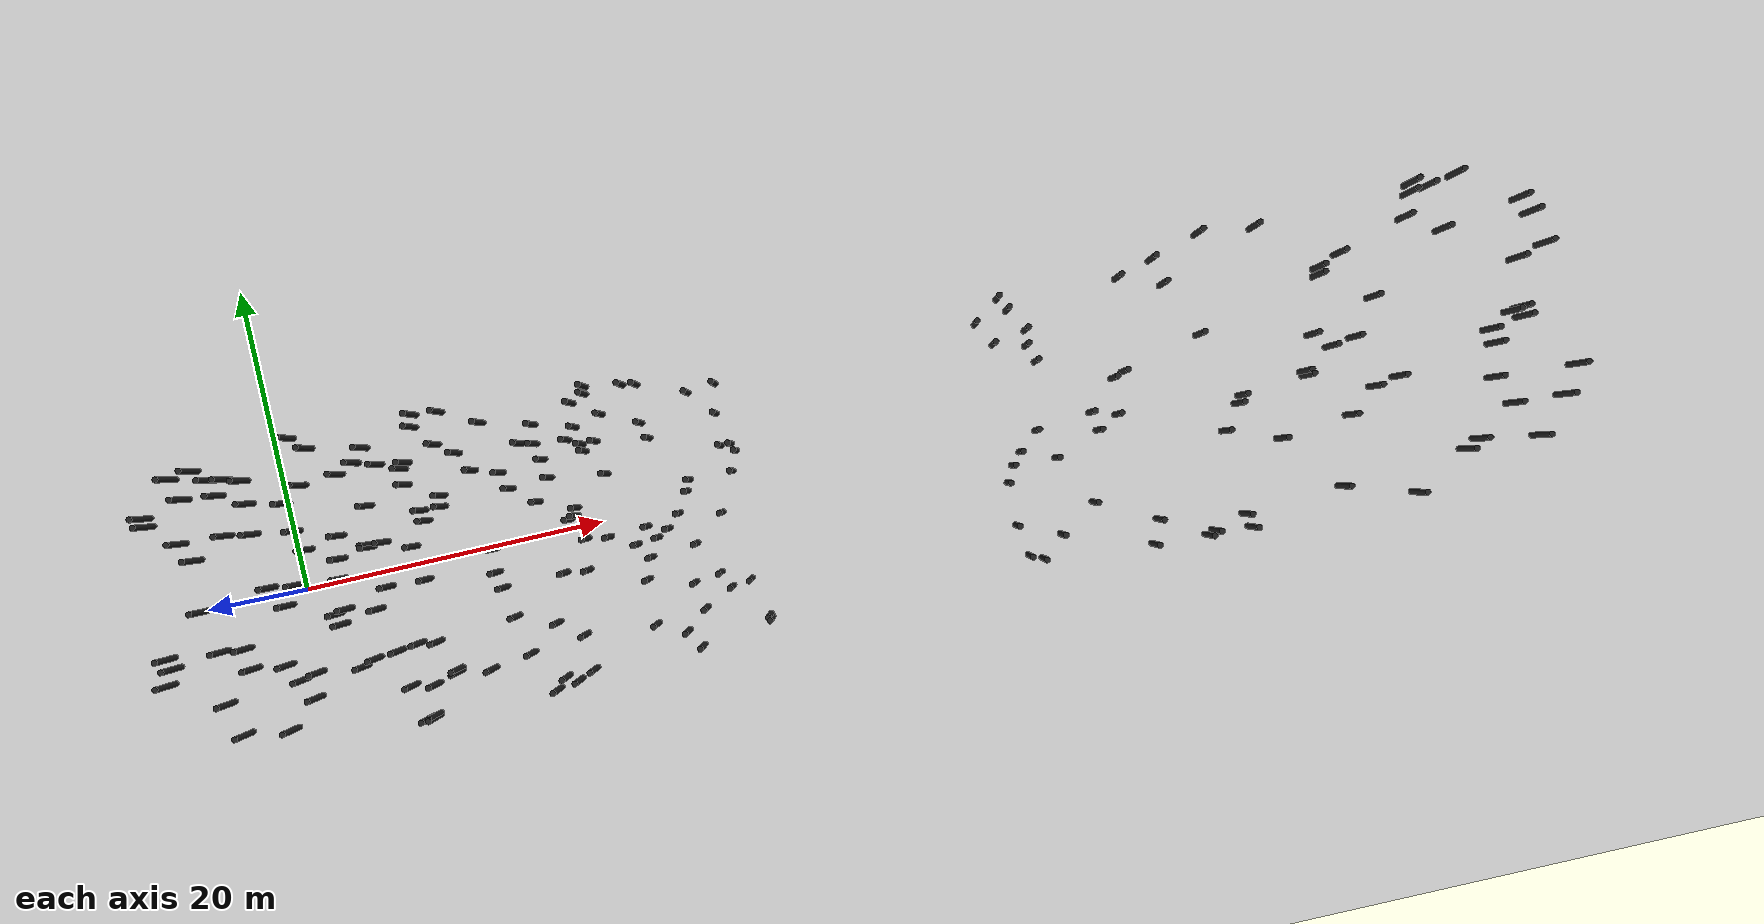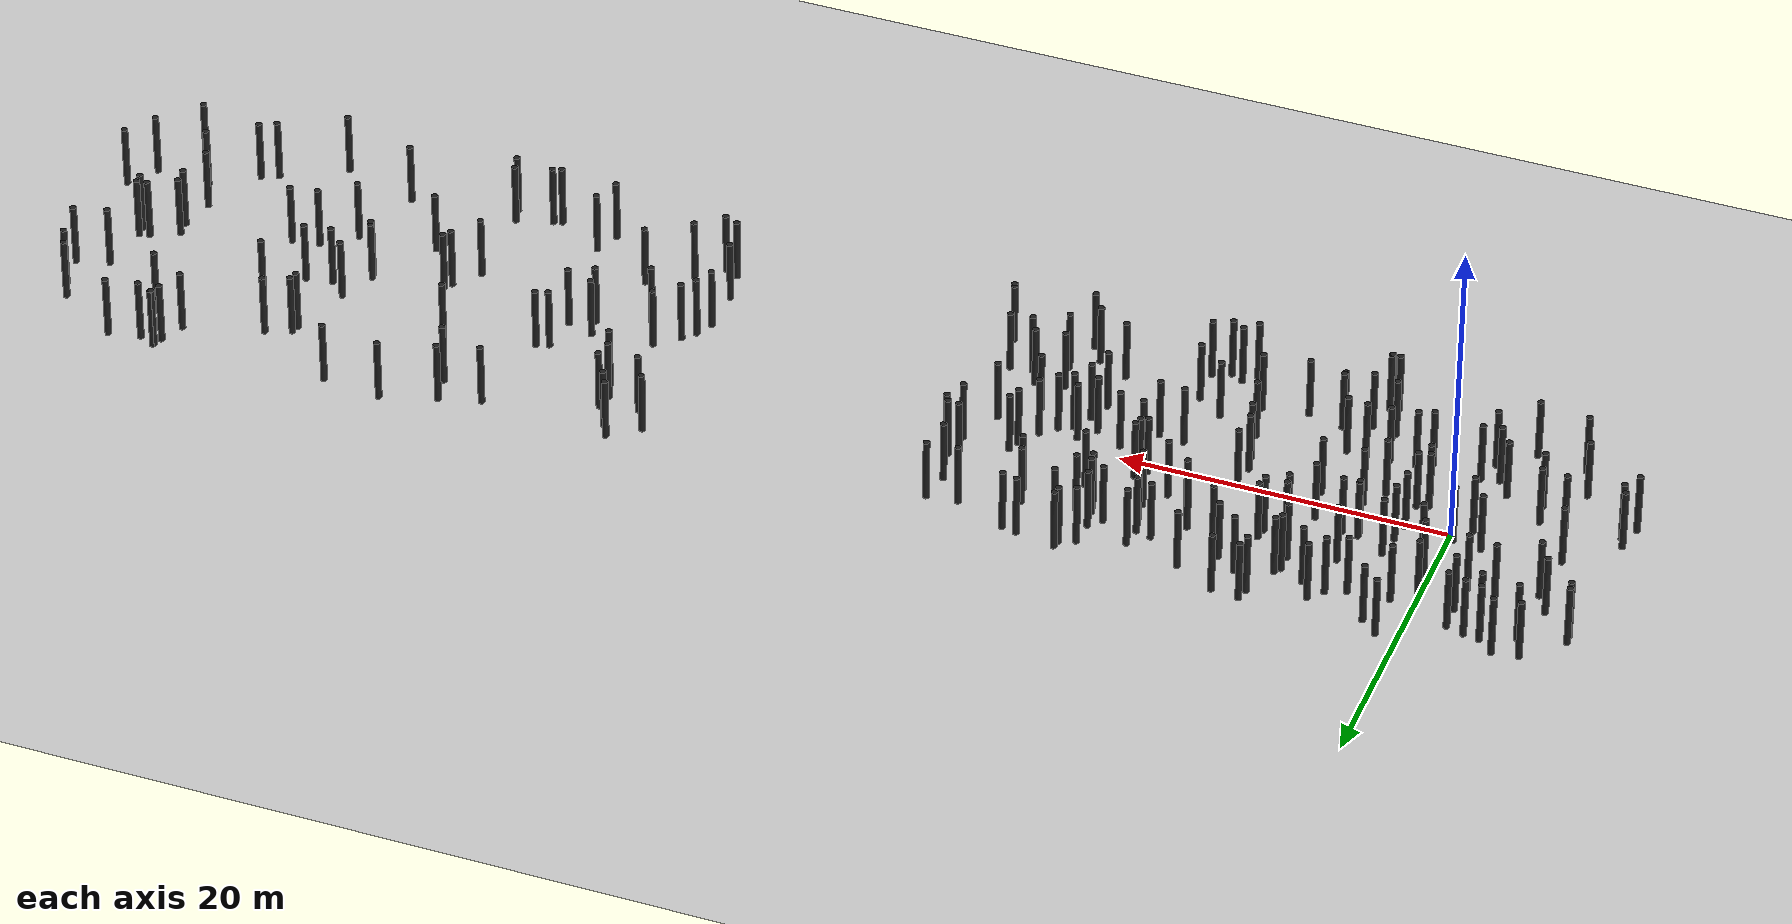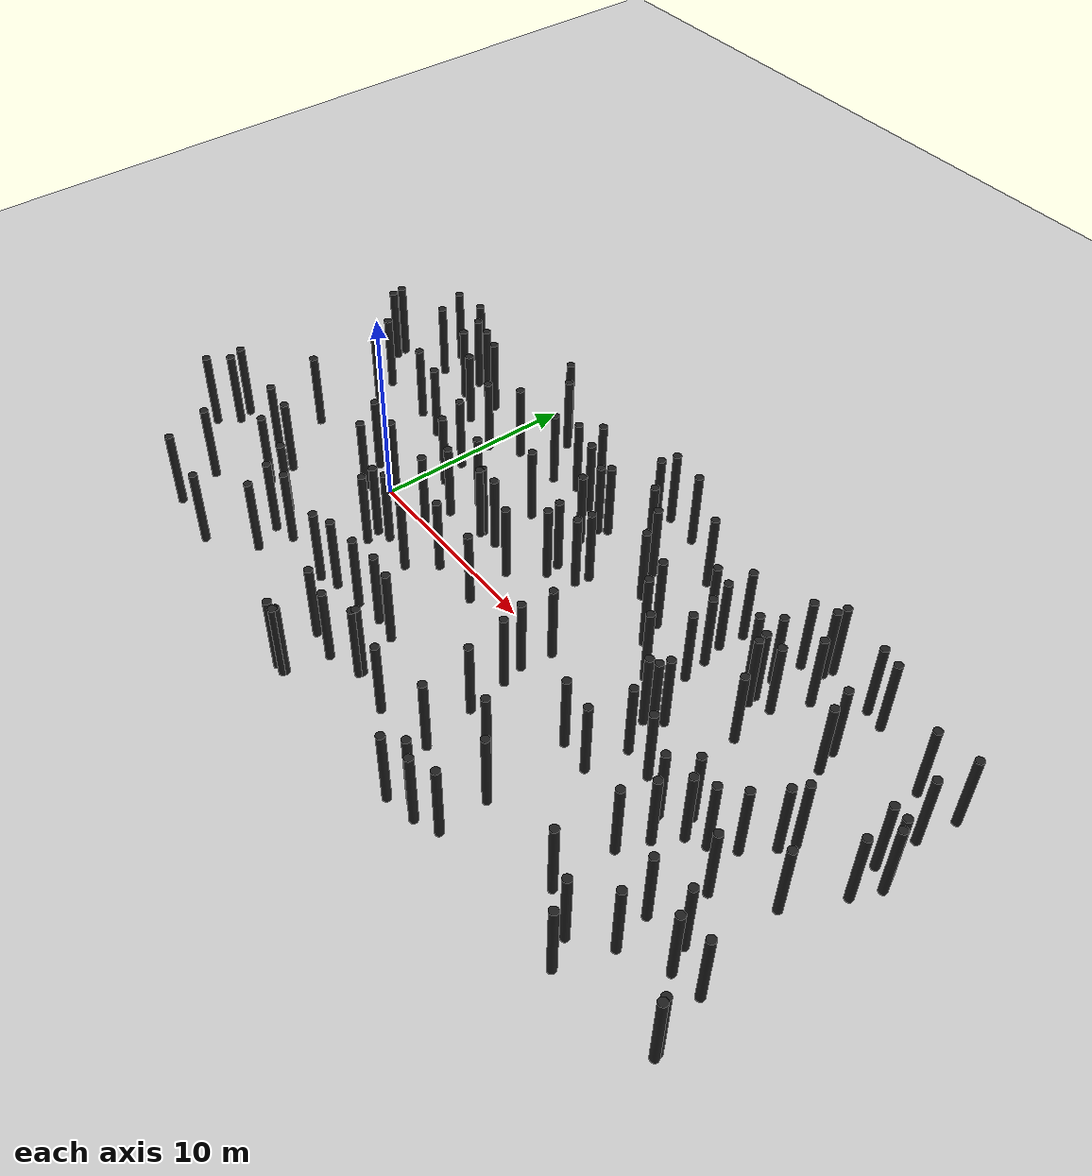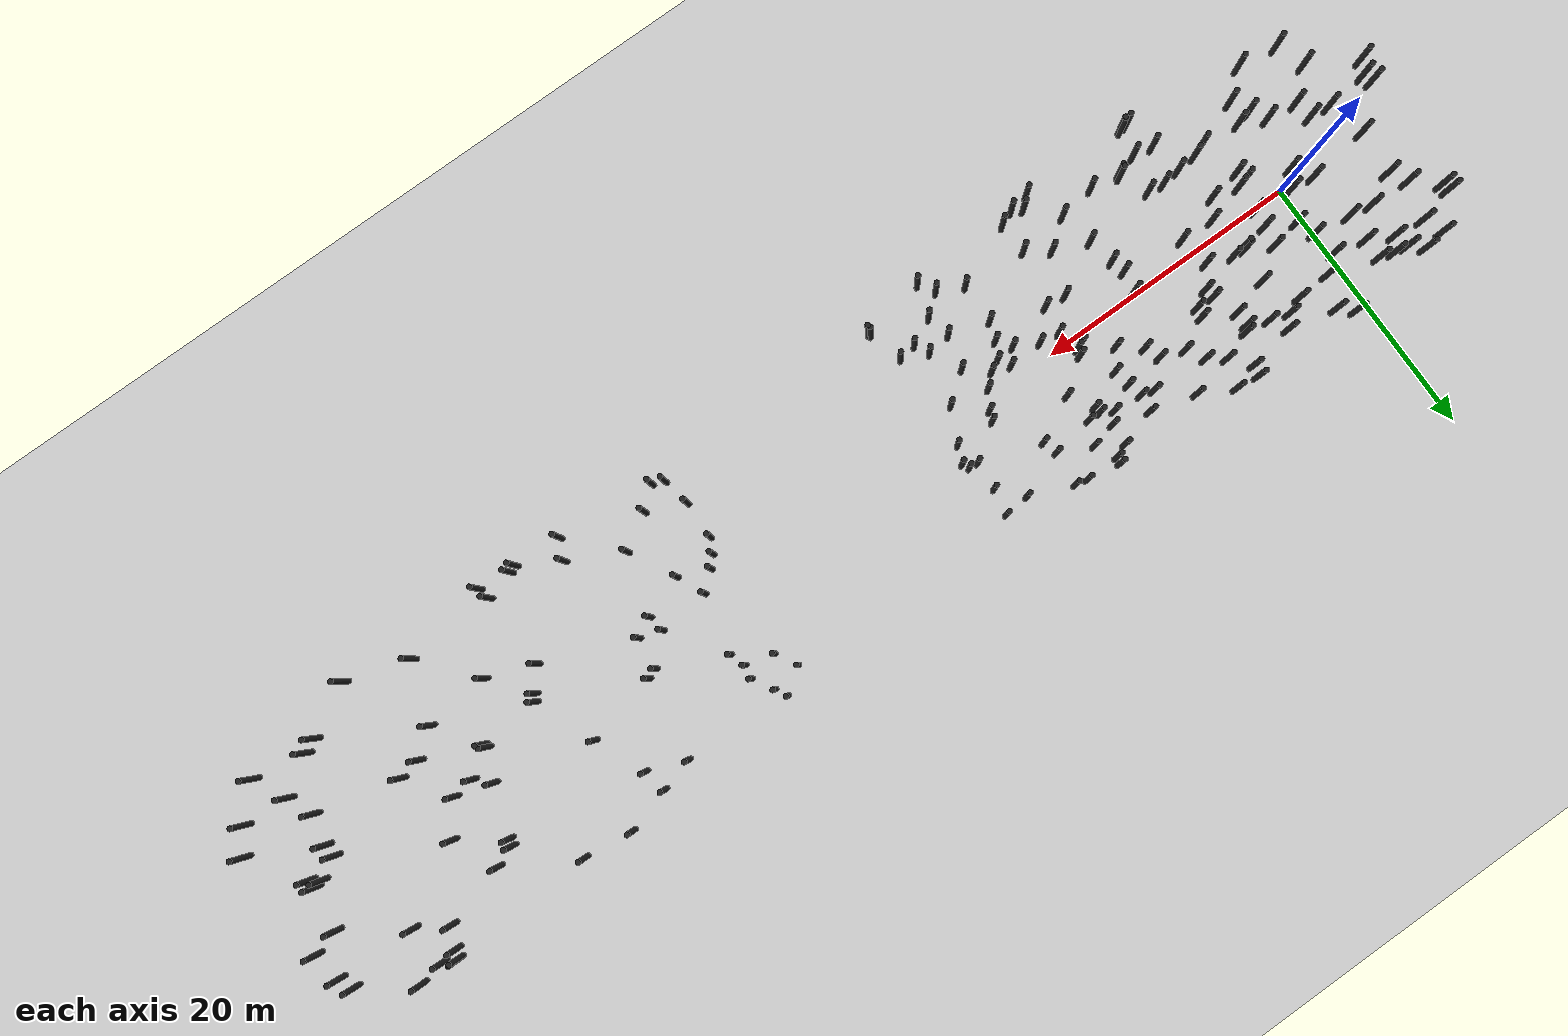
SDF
<sdf version="1.5">
 <world name="default">
  <light name="sun" type="directional">
   <cast_shadows>0</cast_shadows>
   <pose>0 0 10 0 -0 0</pose>
   <diffuse>0.8 0.8 0.8 1</diffuse>
   <specular>0.2 0.2 0.2 1</specular>
   <attenuation>
    <range>1000</range>
    <constant>0.9</constant>
    <linear>0.01</linear>
    <quadratic>0.001</quadratic>
   </attenuation>
   <direction>-0.5 0.1 -0.9</direction>
  </light>
  <model name="ground_plane">
   <static>1</static>
   <link name="link">
    <collision name="collision">
     <geometry><plane><normal>0 0 1</normal><size>200 200</size></plane></geometry>
     <surface><friction><ode><mu>100</mu><mu2>50</mu2></ode></friction></surface>
    </collision>
    <visual name="visual">
     <cast_shadows>0</cast_shadows>
     <geometry><plane><normal>0 0 1</normal><size>200 200</size></plane></geometry>
     <material>
      <script><uri>file://media/materials/scripts/gazebo.material</uri><name>Gazebo/Grey</name></script>
     </material>
    </visual>
   </link>
  </model>
  <physics name="default_physics" default="0" type="ode">
   <max_step_size>0.001</max_step_size>
   <real_time_factor>1</real_time_factor>
   <real_time_update_rate>1000</real_time_update_rate>
   <gravity>0 0 -9.8</gravity>
   <magnetic_field>5.5645e-06 2.28758e-05 -4.23884e-05</magnetic_field>
  </physics>
  <scene><ambient>0.4 0.4 0.4 1</ambient><background>0.7 0.7 0.7 1</background><shadows>0</shadows></scene>
  <spherical_coordinates>
   <surface_model>EARTH_WGS84</surface_model>
   <latitude_deg>0</latitude_deg>
   <longitude_deg>0</longitude_deg>
   <elevation>0</elevation>
   <heading_deg>0</heading_deg>
  </spherical_coordinates>
  <model name="forest_clone_0">
   <pose>12.895 -0.119089 0.004441 0 -0 0</pose>
   <static>1</static>
   <link name="cylinder::link">
    <inertial>
     <mass>1</mass>
     <inertia><ixx>0.083</ixx><ixy>0</ixy><ixz>0</ixz><iyy>0.083</iyy><iyz>0</iyz><izz>0.083</izz></inertia>
    </inertial>
    <collision name="collision">
     <geometry><cylinder><radius>0.2</radius><length>4</length></cylinder></geometry>
    </collision>
    <visual name="visual">
     <geometry><cylinder><radius>0.2</radius><length>4</length></cylinder></geometry>
     <material>
      <script><uri>file://media/materials/scripts/gazebo.material</uri><name>Gazebo/Black</name></script>
     </material>
    </visual>
    <pose>0 0 2 0 -0 0</pose>
   </link>
  </model>
  <model name="forest_clone_1">
   <pose>25.1887 -5.17476 -0.00465 0 -0 0</pose>
   <static>1</static>
   <link name="cylinder::link">
    <inertial>
     <mass>1</mass>
     <inertia><ixx>0.083</ixx><ixy>0</ixy><ixz>0</ixz><iyy>0.083</iyy><iyz>0</iyz><izz>0.083</izz></inertia>
    </inertial>
    <collision name="collision">
     <geometry><cylinder><radius>0.2</radius><length>4</length></cylinder></geometry>
    </collision>
    <visual name="visual">
     <geometry><cylinder><radius>0.2</radius><length>4</length></cylinder></geometry>
     <material>
      <script><uri>file://media/materials/scripts/gazebo.material</uri><name>Gazebo/Black</name></script>
     </material>
    </visual>
    <pose>0 0 2 0 -0 0</pose>
   </link>
  </model>
  <model name="forest_clone_2">
   <pose>-2.32627 4.31326 -0.001627 0 -0 0</pose>
   <static>1</static>
   <link name="cylinder::link">
    <inertial>
     <mass>1</mass>
     <inertia><ixx>0.083</ixx><ixy>0</ixy><ixz>0</ixz><iyy>0.083</iyy><iyz>0</iyz><izz>0.083</izz></inertia>
    </inertial>
    <collision name="collision">
     <geometry><cylinder><radius>0.2</radius><length>4</length></cylinder></geometry>
    </collision>
    <visual name="visual">
     <geometry><cylinder><radius>0.2</radius><length>4</length></cylinder></geometry>
     <material>
      <script><uri>file://media/materials/scripts/gazebo.material</uri><name>Gazebo/Black</name></script>
     </material>
    </visual>
    <pose>0 0 2 0 -0 0</pose>
   </link>
  </model>
  <model name="forest_clone_3">
   <pose>15.7148 -9.32065 0.003944 0 -0 0</pose>
   <static>1</static>
   <link name="cylinder::link">
    <inertial>
     <mass>1</mass>
     <inertia><ixx>0.083</ixx><ixy>0</ixy><ixz>0</ixz><iyy>0.083</iyy><iyz>0</iyz><izz>0.083</izz></inertia>
    </inertial>
    <collision name="collision">
     <geometry><cylinder><radius>0.2</radius><length>4</length></cylinder></geometry>
    </collision>
    <visual name="visual">
     <geometry><cylinder><radius>0.2</radius><length>4</length></cylinder></geometry>
     <material>
      <script><uri>file://media/materials/scripts/gazebo.material</uri><name>Gazebo/Black</name></script>
     </material>
    </visual>
    <pose>0 0 2 0 -0 0</pose>
   </link>
  </model>
  <model name="forest_clone_4">
   <pose>9.53524 9.62866 0.001802 0 -0 0</pose>
   <static>1</static>
   <link name="cylinder::link">
    <inertial>
     <mass>1</mass>
     <inertia><ixx>0.083</ixx><ixy>0</ixy><ixz>0</ixz><iyy>0.083</iyy><iyz>0</iyz><izz>0.083</izz></inertia>
    </inertial>
    <collision name="collision">
     <geometry><cylinder><radius>0.2</radius><length>4</length></cylinder></geometry>
    </collision>
    <visual name="visual">
     <geometry><cylinder><radius>0.2</radius><length>4</length></cylinder></geometry>
     <material>
      <script><uri>file://media/materials/scripts/gazebo.material</uri><name>Gazebo/Black</name></script>
     </material>
    </visual>
    <pose>0 0 2 0 -0 0</pose>
   </link>
  </model>
  <model name="forest_clone_5">
   <pose>-4.02803 7.27232 -0.002835 0 -0 0</pose>
   <static>1</static>
   <link name="cylinder::link">
    <inertial>
     <mass>1</mass>
     <inertia><ixx>0.083</ixx><ixy>0</ixy><ixz>0</ixz><iyy>0.083</iyy><iyz>0</iyz><izz>0.083</izz></inertia>
    </inertial>
    <collision name="collision">
     <geometry><cylinder><radius>0.2</radius><length>4</length></cylinder></geometry>
    </collision>
    <visual name="visual">
     <geometry><cylinder><radius>0.2</radius><length>4</length></cylinder></geometry>
     <material>
      <script><uri>file://media/materials/scripts/gazebo.material</uri><name>Gazebo/Black</name></script>
     </material>
    </visual>
    <pose>0 0 2 0 -0 0</pose>
   </link>
  </model>
  <model name="forest_clone_6">
   <pose>29.6565 2.65853 0.003318 0 -0 0</pose>
   <static>1</static>
   <link name="cylinder::link">
    <inertial>
     <mass>1</mass>
     <inertia><ixx>0.083</ixx><ixy>0</ixy><ixz>0</ixz><iyy>0.083</iyy><iyz>0</iyz><izz>0.083</izz></inertia>
    </inertial>
    <collision name="collision">
     <geometry><cylinder><radius>0.2</radius><length>4</length></cylinder></geometry>
    </collision>
    <visual name="visual">
     <geometry><cylinder><radius>0.2</radius><length>4</length></cylinder></geometry>
     <material>
      <script><uri>file://media/materials/scripts/gazebo.material</uri><name>Gazebo/Black</name></script>
     </material>
    </visual>
    <pose>0 0 2 0 -0 0</pose>
   </link>
  </model>
  <model name="forest_clone_7">
   <pose>25.9618 0.771852 0.00141 0 -0 0</pose>
   <static>1</static>
   <link name="cylinder::link">
    <inertial>
     <mass>1</mass>
     <inertia><ixx>0.083</ixx><ixy>0</ixy><ixz>0</ixz><iyy>0.083</iyy><iyz>0</iyz><izz>0.083</izz></inertia>
    </inertial>
    <collision name="collision">
     <geometry><cylinder><radius>0.2</radius><length>4</length></cylinder></geometry>
    </collision>
    <visual name="visual">
     <geometry><cylinder><radius>0.2</radius><length>4</length></cylinder></geometry>
     <material>
      <script><uri>file://media/materials/scripts/gazebo.material</uri><name>Gazebo/Black</name></script>
     </material>
    </visual>
    <pose>0 0 2 0 -0 0</pose>
   </link>
  </model>
  <model name="forest_clone_8">
   <pose>26.959 -4.90211 -0.00242 0 -0 0</pose>
   <static>1</static>
   <link name="cylinder::link">
    <inertial>
     <mass>1</mass>
     <inertia><ixx>0.083</ixx><ixy>0</ixy><ixz>0</ixz><iyy>0.083</iyy><iyz>0</iyz><izz>0.083</izz></inertia>
    </inertial>
    <collision name="collision">
     <geometry><cylinder><radius>0.2</radius><length>4</length></cylinder></geometry>
    </collision>
    <visual name="visual">
     <geometry><cylinder><radius>0.2</radius><length>4</length></cylinder></geometry>
     <material>
      <script><uri>file://media/materials/scripts/gazebo.material</uri><name>Gazebo/Black</name></script>
     </material>
    </visual>
    <pose>0 0 2 0 -0 0</pose>
   </link>
  </model>
  <model name="forest_clone_9">
   <pose>4.9494 1.80469 0.002967 0 -0 0</pose>
   <static>1</static>
   <link name="cylinder::link">
    <inertial>
     <mass>1</mass>
     <inertia><ixx>0.083</ixx><ixy>0</ixy><ixz>0</ixz><iyy>0.083</iyy><iyz>0</iyz><izz>0.083</izz></inertia>
    </inertial>
    <collision name="collision">
     <geometry><cylinder><radius>0.2</radius><length>4</length></cylinder></geometry>
    </collision>
    <visual name="visual">
     <geometry><cylinder><radius>0.2</radius><length>4</length></cylinder></geometry>
     <material>
      <script><uri>file://media/materials/scripts/gazebo.material</uri><name>Gazebo/Black</name></script>
     </material>
    </visual>
    <pose>0 0 2 0 -0 0</pose>
   </link>
  </model>
  <model name="forest_clone_10">
   <pose>23.9507 5.80226 0.000237 0 -0 0</pose>
   <static>1</static>
   <link name="cylinder::link">
    <inertial>
     <mass>1</mass>
     <inertia><ixx>0.083</ixx><ixy>0</ixy><ixz>0</ixz><iyy>0.083</iyy><iyz>0</iyz><izz>0.083</izz></inertia>
    </inertial>
    <collision name="collision">
     <geometry><cylinder><radius>0.2</radius><length>4</length></cylinder></geometry>
    </collision>
    <visual name="visual">
     <geometry><cylinder><radius>0.2</radius><length>4</length></cylinder></geometry>
     <material>
      <script><uri>file://media/materials/scripts/gazebo.material</uri><name>Gazebo/Black</name></script>
     </material>
    </visual>
    <pose>0 0 2 0 -0 0</pose>
   </link>
  </model>
  <model name="forest_clone_11">
   <pose>-4.38543 -2.89842 -0.004006 0 -0 0</pose>
   <static>1</static>
   <link name="cylinder::link">
    <inertial>
     <mass>1</mass>
     <inertia><ixx>0.083</ixx><ixy>0</ixy><ixz>0</ixz><iyy>0.083</iyy><iyz>0</iyz><izz>0.083</izz></inertia>
    </inertial>
    <collision name="collision">
     <geometry><cylinder><radius>0.2</radius><length>4</length></cylinder></geometry>
    </collision>
    <visual name="visual">
     <geometry><cylinder><radius>0.2</radius><length>4</length></cylinder></geometry>
     <material>
      <script><uri>file://media/materials/scripts/gazebo.material</uri><name>Gazebo/Black</name></script>
     </material>
    </visual>
    <pose>0 0 2 0 -0 0</pose>
   </link>
  </model>
  <model name="forest_clone_12">
   <pose>10.5715 7.4024 -0.003288 0 -0 0</pose>
   <static>1</static>
   <link name="cylinder::link">
    <inertial>
     <mass>1</mass>
     <inertia><ixx>0.083</ixx><ixy>0</ixy><ixz>0</ixz><iyy>0.083</iyy><iyz>0</iyz><izz>0.083</izz></inertia>
    </inertial>
    <collision name="collision">
     <geometry><cylinder><radius>0.2</radius><length>4</length></cylinder></geometry>
    </collision>
    <visual name="visual">
     <geometry><cylinder><radius>0.2</radius><length>4</length></cylinder></geometry>
     <material>
      <script><uri>file://media/materials/scripts/gazebo.material</uri><name>Gazebo/Black</name></script>
     </material>
    </visual>
    <pose>0 0 2 0 -0 0</pose>
   </link>
  </model>
  <model name="forest_clone_13">
   <pose>24.0765 -8.17114 -0.00101 0 -0 0</pose>
   <static>1</static>
   <link name="cylinder::link">
    <inertial>
     <mass>1</mass>
     <inertia><ixx>0.083</ixx><ixy>0</ixy><ixz>0</ixz><iyy>0.083</iyy><iyz>0</iyz><izz>0.083</izz></inertia>
    </inertial>
    <collision name="collision">
     <geometry><cylinder><radius>0.2</radius><length>4</length></cylinder></geometry>
    </collision>
    <visual name="visual">
     <geometry><cylinder><radius>0.2</radius><length>4</length></cylinder></geometry>
     <material>
      <script><uri>file://media/materials/scripts/gazebo.material</uri><name>Gazebo/Black</name></script>
     </material>
    </visual>
    <pose>0 0 2 0 -0 0</pose>
   </link>
  </model>
  <model name="forest_clone_14">
   <pose>-1.13931 -5.70303 -0.004506 0 -0 0</pose>
   <static>1</static>
   <link name="cylinder::link">
    <inertial>
     <mass>1</mass>
     <inertia><ixx>0.083</ixx><ixy>0</ixy><ixz>0</ixz><iyy>0.083</iyy><iyz>0</iyz><izz>0.083</izz></inertia>
    </inertial>
    <collision name="collision">
     <geometry><cylinder><radius>0.2</radius><length>4</length></cylinder></geometry>
    </collision>
    <visual name="visual">
     <geometry><cylinder><radius>0.2</radius><length>4</length></cylinder></geometry>
     <material>
      <script><uri>file://media/materials/scripts/gazebo.material</uri><name>Gazebo/Black</name></script>
     </material>
    </visual>
    <pose>0 0 2 0 -0 0</pose>
   </link>
  </model>
  <model name="forest_clone_15">
   <pose>-6.35011 3.45369 0.003337 0 -0 0</pose>
   <static>1</static>
   <link name="cylinder::link">
    <inertial>
     <mass>1</mass>
     <inertia><ixx>0.083</ixx><ixy>0</ixy><ixz>0</ixz><iyy>0.083</iyy><iyz>0</iyz><izz>0.083</izz></inertia>
    </inertial>
    <collision name="collision">
     <geometry><cylinder><radius>0.2</radius><length>4</length></cylinder></geometry>
    </collision>
    <visual name="visual">
     <geometry><cylinder><radius>0.2</radius><length>4</length></cylinder></geometry>
     <material>
      <script><uri>file://media/materials/scripts/gazebo.material</uri><name>Gazebo/Black</name></script>
     </material>
    </visual>
    <pose>0 0 2 0 -0 0</pose>
   </link>
  </model>
  <model name="forest_clone_16">
   <pose>15.8736 -5.74239 0.003533 0 -0 0</pose>
   <static>1</static>
   <link name="cylinder::link">
    <inertial>
     <mass>1</mass>
     <inertia><ixx>0.083</ixx><ixy>0</ixy><ixz>0</ixz><iyy>0.083</iyy><iyz>0</iyz><izz>0.083</izz></inertia>
    </inertial>
    <collision name="collision">
     <geometry><cylinder><radius>0.2</radius><length>4</length></cylinder></geometry>
    </collision>
    <visual name="visual">
     <geometry><cylinder><radius>0.2</radius><length>4</length></cylinder></geometry>
     <material>
      <script><uri>file://media/materials/scripts/gazebo.material</uri><name>Gazebo/Black</name></script>
     </material>
    </visual>
    <pose>0 0 2 0 -0 0</pose>
   </link>
  </model>
  <model name="forest_clone_17">
   <pose>19.9042 5.30619 -0.004813 0 -0 0</pose>
   <static>1</static>
   <link name="cylinder::link">
    <inertial>
     <mass>1</mass>
     <inertia><ixx>0.083</ixx><ixy>0</ixy><ixz>0</ixz><iyy>0.083</iyy><iyz>0</iyz><izz>0.083</izz></inertia>
    </inertial>
    <collision name="collision">
     <geometry><cylinder><radius>0.2</radius><length>4</length></cylinder></geometry>
    </collision>
    <visual name="visual">
     <geometry><cylinder><radius>0.2</radius><length>4</length></cylinder></geometry>
     <material>
      <script><uri>file://media/materials/scripts/gazebo.material</uri><name>Gazebo/Black</name></script>
     </material>
    </visual>
    <pose>0 0 2 0 -0 0</pose>
   </link>
  </model>
  <model name="forest_clone_18">
   <pose>5.92535 1.9138 -0.002272 0 -0 0</pose>
   <static>1</static>
   <link name="cylinder::link">
    <inertial>
     <mass>1</mass>
     <inertia><ixx>0.083</ixx><ixy>0</ixy><ixz>0</ixz><iyy>0.083</iyy><iyz>0</iyz><izz>0.083</izz></inertia>
    </inertial>
    <collision name="collision">
     <geometry><cylinder><radius>0.2</radius><length>4</length></cylinder></geometry>
    </collision>
    <visual name="visual">
     <geometry><cylinder><radius>0.2</radius><length>4</length></cylinder></geometry>
     <material>
      <script><uri>file://media/materials/scripts/gazebo.material</uri><name>Gazebo/Black</name></script>
     </material>
    </visual>
    <pose>0 0 2 0 -0 0</pose>
   </link>
  </model>
  <model name="forest_clone_19">
   <pose>-2.20388 6.31733 -0.001496 0 -0 0</pose>
   <static>1</static>
   <link name="cylinder::link">
    <inertial>
     <mass>1</mass>
     <inertia><ixx>0.083</ixx><ixy>0</ixy><ixz>0</ixz><iyy>0.083</iyy><iyz>0</iyz><izz>0.083</izz></inertia>
    </inertial>
    <collision name="collision">
     <geometry><cylinder><radius>0.2</radius><length>4</length></cylinder></geometry>
    </collision>
    <visual name="visual">
     <geometry><cylinder><radius>0.2</radius><length>4</length></cylinder></geometry>
     <material>
      <script><uri>file://media/materials/scripts/gazebo.material</uri><name>Gazebo/Black</name></script>
     </material>
    </visual>
    <pose>0 0 2 0 -0 0</pose>
   </link>
  </model>
  <model name="forest_clone_20">
   <pose>24.8071 -9.32974 0.002086 0 -0 0</pose>
   <static>1</static>
   <link name="cylinder::link">
    <inertial>
     <mass>1</mass>
     <inertia><ixx>0.083</ixx><ixy>0</ixy><ixz>0</ixz><iyy>0.083</iyy><iyz>0</iyz><izz>0.083</izz></inertia>
    </inertial>
    <collision name="collision">
     <geometry><cylinder><radius>0.2</radius><length>4</length></cylinder></geometry>
    </collision>
    <visual name="visual">
     <geometry><cylinder><radius>0.2</radius><length>4</length></cylinder></geometry>
     <material>
      <script><uri>file://media/materials/scripts/gazebo.material</uri><name>Gazebo/Black</name></script>
     </material>
    </visual>
    <pose>0 0 2 0 -0 0</pose>
   </link>
  </model>
  <model name="forest_clone_21">
   <pose>0.126506 5.79653 -0.000546 0 -0 0</pose>
   <static>1</static>
   <link name="cylinder::link">
    <inertial>
     <mass>1</mass>
     <inertia><ixx>0.083</ixx><ixy>0</ixy><ixz>0</ixz><iyy>0.083</iyy><iyz>0</iyz><izz>0.083</izz></inertia>
    </inertial>
    <collision name="collision">
     <geometry><cylinder><radius>0.2</radius><length>4</length></cylinder></geometry>
    </collision>
    <visual name="visual">
     <geometry><cylinder><radius>0.2</radius><length>4</length></cylinder></geometry>
     <material>
      <script><uri>file://media/materials/scripts/gazebo.material</uri><name>Gazebo/Black</name></script>
     </material>
    </visual>
    <pose>0 0 2 0 -0 0</pose>
   </link>
  </model>
  <model name="forest_clone_22">
   <pose>27.3638 7.05879 0.004123 0 -0 0</pose>
   <static>1</static>
   <link name="cylinder::link">
    <inertial>
     <mass>1</mass>
     <inertia><ixx>0.083</ixx><ixy>0</ixy><ixz>0</ixz><iyy>0.083</iyy><iyz>0</iyz><izz>0.083</izz></inertia>
    </inertial>
    <collision name="collision">
     <geometry><cylinder><radius>0.2</radius><length>4</length></cylinder></geometry>
    </collision>
    <visual name="visual">
     <geometry><cylinder><radius>0.2</radius><length>4</length></cylinder></geometry>
     <material>
      <script><uri>file://media/materials/scripts/gazebo.material</uri><name>Gazebo/Black</name></script>
     </material>
    </visual>
    <pose>0 0 2 0 -0 0</pose>
   </link>
  </model>
  <model name="forest_clone_23">
   <pose>5.38656 4.45946 0.001076 0 -0 0</pose>
   <static>1</static>
   <link name="cylinder::link">
    <inertial>
     <mass>1</mass>
     <inertia><ixx>0.083</ixx><ixy>0</ixy><ixz>0</ixz><iyy>0.083</iyy><iyz>0</iyz><izz>0.083</izz></inertia>
    </inertial>
    <collision name="collision">
     <geometry><cylinder><radius>0.2</radius><length>4</length></cylinder></geometry>
    </collision>
    <visual name="visual">
     <geometry><cylinder><radius>0.2</radius><length>4</length></cylinder></geometry>
     <material>
      <script><uri>file://media/materials/scripts/gazebo.material</uri><name>Gazebo/Black</name></script>
     </material>
    </visual>
    <pose>0 0 2 0 -0 0</pose>
   </link>
  </model>
  <model name="forest_clone_24">
   <pose>8.09345 6.32276 0.001507 0 -0 0</pose>
   <static>1</static>
   <link name="cylinder::link">
    <inertial>
     <mass>1</mass>
     <inertia><ixx>0.083</ixx><ixy>0</ixy><ixz>0</ixz><iyy>0.083</iyy><iyz>0</iyz><izz>0.083</izz></inertia>
    </inertial>
    <collision name="collision">
     <geometry><cylinder><radius>0.2</radius><length>4</length></cylinder></geometry>
    </collision>
    <visual name="visual">
     <geometry><cylinder><radius>0.2</radius><length>4</length></cylinder></geometry>
     <material>
      <script><uri>file://media/materials/scripts/gazebo.material</uri><name>Gazebo/Black</name></script>
     </material>
    </visual>
    <pose>0 0 2 0 -0 0</pose>
   </link>
  </model>
  <model name="forest_clone_25">
   <pose>13.8201 -7.30259 -0.001052 0 -0 0</pose>
   <static>1</static>
   <link name="cylinder::link">
    <inertial>
     <mass>1</mass>
     <inertia><ixx>0.083</ixx><ixy>0</ixy><ixz>0</ixz><iyy>0.083</iyy><iyz>0</iyz><izz>0.083</izz></inertia>
    </inertial>
    <collision name="collision">
     <geometry><cylinder><radius>0.2</radius><length>4</length></cylinder></geometry>
    </collision>
    <visual name="visual">
     <geometry><cylinder><radius>0.2</radius><length>4</length></cylinder></geometry>
     <material>
      <script><uri>file://media/materials/scripts/gazebo.material</uri><name>Gazebo/Black</name></script>
     </material>
    </visual>
    <pose>0 0 2 0 -0 0</pose>
   </link>
  </model>
  <model name="forest_clone_26">
   <pose>4.63647 -2.27152 0.001396 0 -0 0</pose>
   <static>1</static>
   <link name="cylinder::link">
    <inertial>
     <mass>1</mass>
     <inertia><ixx>0.083</ixx><ixy>0</ixy><ixz>0</ixz><iyy>0.083</iyy><iyz>0</iyz><izz>0.083</izz></inertia>
    </inertial>
    <collision name="collision">
     <geometry><cylinder><radius>0.2</radius><length>4</length></cylinder></geometry>
    </collision>
    <visual name="visual">
     <geometry><cylinder><radius>0.2</radius><length>4</length></cylinder></geometry>
     <material>
      <script><uri>file://media/materials/scripts/gazebo.material</uri><name>Gazebo/Black</name></script>
     </material>
    </visual>
    <pose>0 0 2 0 -0 0</pose>
   </link>
  </model>
  <model name="forest_clone_27">
   <pose>4.95092 1.96603 -0.000124 0 -0 0</pose>
   <static>1</static>
   <link name="cylinder::link">
    <inertial>
     <mass>1</mass>
     <inertia><ixx>0.083</ixx><ixy>0</ixy><ixz>0</ixz><iyy>0.083</iyy><iyz>0</iyz><izz>0.083</izz></inertia>
    </inertial>
    <collision name="collision">
     <geometry><cylinder><radius>0.2</radius><length>4</length></cylinder></geometry>
    </collision>
    <visual name="visual">
     <geometry><cylinder><radius>0.2</radius><length>4</length></cylinder></geometry>
     <material>
      <script><uri>file://media/materials/scripts/gazebo.material</uri><name>Gazebo/Black</name></script>
     </material>
    </visual>
    <pose>0 0 2 0 -0 0</pose>
   </link>
  </model>
  <model name="forest_clone_28">
   <pose>8.89961 -7.26019 -0.000283 0 -0 0</pose>
   <static>1</static>
   <link name="cylinder::link">
    <inertial>
     <mass>1</mass>
     <inertia><ixx>0.083</ixx><ixy>0</ixy><ixz>0</ixz><iyy>0.083</iyy><iyz>0</iyz><izz>0.083</izz></inertia>
    </inertial>
    <collision name="collision">
     <geometry><cylinder><radius>0.2</radius><length>4</length></cylinder></geometry>
    </collision>
    <visual name="visual">
     <geometry><cylinder><radius>0.2</radius><length>4</length></cylinder></geometry>
     <material>
      <script><uri>file://media/materials/scripts/gazebo.material</uri><name>Gazebo/Black</name></script>
     </material>
    </visual>
    <pose>0 0 2 0 -0 0</pose>
   </link>
  </model>
  <model name="forest_clone_29">
   <pose>14.739 3.50483 -0.00413 0 -0 0</pose>
   <static>1</static>
   <link name="cylinder::link">
    <inertial>
     <mass>1</mass>
     <inertia><ixx>0.083</ixx><ixy>0</ixy><ixz>0</ixz><iyy>0.083</iyy><iyz>0</iyz><izz>0.083</izz></inertia>
    </inertial>
    <collision name="collision">
     <geometry><cylinder><radius>0.2</radius><length>4</length></cylinder></geometry>
    </collision>
    <visual name="visual">
     <geometry><cylinder><radius>0.2</radius><length>4</length></cylinder></geometry>
     <material>
      <script><uri>file://media/materials/scripts/gazebo.material</uri><name>Gazebo/Black</name></script>
     </material>
    </visual>
    <pose>0 0 2 0 -0 0</pose>
   </link>
  </model>
  <model name="forest_clone_30">
   <pose>17.1866 4.89143 -0.004943 0 -0 0</pose>
   <static>1</static>
   <link name="cylinder::link">
    <inertial>
     <mass>1</mass>
     <inertia><ixx>0.083</ixx><ixy>0</ixy><ixz>0</ixz><iyy>0.083</iyy><iyz>0</iyz><izz>0.083</izz></inertia>
    </inertial>
    <collision name="collision">
     <geometry><cylinder><radius>0.2</radius><length>4</length></cylinder></geometry>
    </collision>
    <visual name="visual">
     <geometry><cylinder><radius>0.2</radius><length>4</length></cylinder></geometry>
     <material>
      <script><uri>file://media/materials/scripts/gazebo.material</uri><name>Gazebo/Black</name></script>
     </material>
    </visual>
    <pose>0 0 2 0 -0 0</pose>
   </link>
  </model>
  <model name="forest_clone_31">
   <pose>-6.85207 8.98828 -0.000139 0 -0 0</pose>
   <static>1</static>
   <link name="cylinder::link">
    <inertial>
     <mass>1</mass>
     <inertia><ixx>0.083</ixx><ixy>0</ixy><ixz>0</ixz><iyy>0.083</iyy><iyz>0</iyz><izz>0.083</izz></inertia>
    </inertial>
    <collision name="collision">
     <geometry><cylinder><radius>0.2</radius><length>4</length></cylinder></geometry>
    </collision>
    <visual name="visual">
     <geometry><cylinder><radius>0.2</radius><length>4</length></cylinder></geometry>
     <material>
      <script><uri>file://media/materials/scripts/gazebo.material</uri><name>Gazebo/Black</name></script>
     </material>
    </visual>
    <pose>0 0 2 0 -0 0</pose>
   </link>
  </model>
  <model name="forest_clone_32">
   <pose>-1.97657 0.643385 0.001926 0 -0 0</pose>
   <static>1</static>
   <link name="cylinder::link">
    <inertial>
     <mass>1</mass>
     <inertia><ixx>0.083</ixx><ixy>0</ixy><ixz>0</ixz><iyy>0.083</iyy><iyz>0</iyz><izz>0.083</izz></inertia>
    </inertial>
    <collision name="collision">
     <geometry><cylinder><radius>0.2</radius><length>4</length></cylinder></geometry>
    </collision>
    <visual name="visual">
     <geometry><cylinder><radius>0.2</radius><length>4</length></cylinder></geometry>
     <material>
      <script><uri>file://media/materials/scripts/gazebo.material</uri><name>Gazebo/Black</name></script>
     </material>
    </visual>
    <pose>0 0 2 0 -0 0</pose>
   </link>
  </model>
  <model name="forest_clone_33">
   <pose>10.1308 3.35061 7.8e-05 0 -0 0</pose>
   <static>1</static>
   <link name="cylinder::link">
    <inertial>
     <mass>1</mass>
     <inertia><ixx>0.083</ixx><ixy>0</ixy><ixz>0</ixz><iyy>0.083</iyy><iyz>0</iyz><izz>0.083</izz></inertia>
    </inertial>
    <collision name="collision">
     <geometry><cylinder><radius>0.2</radius><length>4</length></cylinder></geometry>
    </collision>
    <visual name="visual">
     <geometry><cylinder><radius>0.2</radius><length>4</length></cylinder></geometry>
     <material>
      <script><uri>file://media/materials/scripts/gazebo.material</uri><name>Gazebo/Black</name></script>
     </material>
    </visual>
    <pose>0 0 2 0 -0 0</pose>
   </link>
  </model>
  <model name="forest_clone_34">
   <pose>20.8621 8.94426 0.001625 0 -0 0</pose>
   <static>1</static>
   <link name="cylinder::link">
    <inertial>
     <mass>1</mass>
     <inertia><ixx>0.083</ixx><ixy>0</ixy><ixz>0</ixz><iyy>0.083</iyy><iyz>0</iyz><izz>0.083</izz></inertia>
    </inertial>
    <collision name="collision">
     <geometry><cylinder><radius>0.2</radius><length>4</length></cylinder></geometry>
    </collision>
    <visual name="visual">
     <geometry><cylinder><radius>0.2</radius><length>4</length></cylinder></geometry>
     <material>
      <script><uri>file://media/materials/scripts/gazebo.material</uri><name>Gazebo/Black</name></script>
     </material>
    </visual>
    <pose>0 0 2 0 -0 0</pose>
   </link>
  </model>
  <model name="forest_clone_35">
   <pose>3.95483 6.90924 -0.004175 0 -0 0</pose>
   <static>1</static>
   <link name="cylinder::link">
    <inertial>
     <mass>1</mass>
     <inertia><ixx>0.083</ixx><ixy>0</ixy><ixz>0</ixz><iyy>0.083</iyy><iyz>0</iyz><izz>0.083</izz></inertia>
    </inertial>
    <collision name="collision">
     <geometry><cylinder><radius>0.2</radius><length>4</length></cylinder></geometry>
    </collision>
    <visual name="visual">
     <geometry><cylinder><radius>0.2</radius><length>4</length></cylinder></geometry>
     <material>
      <script><uri>file://media/materials/scripts/gazebo.material</uri><name>Gazebo/Black</name></script>
     </material>
    </visual>
    <pose>0 0 2 0 -0 0</pose>
   </link>
  </model>
  <model name="forest_clone_36">
   <pose>8.91176 2.67337 0.003223 0 -0 0</pose>
   <static>1</static>
   <link name="cylinder::link">
    <inertial>
     <mass>1</mass>
     <inertia><ixx>0.083</ixx><ixy>0</ixy><ixz>0</ixz><iyy>0.083</iyy><iyz>0</iyz><izz>0.083</izz></inertia>
    </inertial>
    <collision name="collision">
     <geometry><cylinder><radius>0.2</radius><length>4</length></cylinder></geometry>
    </collision>
    <visual name="visual">
     <geometry><cylinder><radius>0.2</radius><length>4</length></cylinder></geometry>
     <material>
      <script><uri>file://media/materials/scripts/gazebo.material</uri><name>Gazebo/Black</name></script>
     </material>
    </visual>
    <pose>0 0 2 0 -0 0</pose>
   </link>
  </model>
  <model name="forest_clone_37">
   <pose>20.3619 -1.02855 -0.003411 0 -0 0</pose>
   <static>1</static>
   <link name="cylinder::link">
    <inertial>
     <mass>1</mass>
     <inertia><ixx>0.083</ixx><ixy>0</ixy><ixz>0</ixz><iyy>0.083</iyy><iyz>0</iyz><izz>0.083</izz></inertia>
    </inertial>
    <collision name="collision">
     <geometry><cylinder><radius>0.2</radius><length>4</length></cylinder></geometry>
    </collision>
    <visual name="visual">
     <geometry><cylinder><radius>0.2</radius><length>4</length></cylinder></geometry>
     <material>
      <script><uri>file://media/materials/scripts/gazebo.material</uri><name>Gazebo/Black</name></script>
     </material>
    </visual>
    <pose>0 0 2 0 -0 0</pose>
   </link>
  </model>
  <model name="forest_clone_38">
   <pose>22.1858 -7.27397 -0.002638 0 -0 0</pose>
   <static>1</static>
   <link name="cylinder::link">
    <inertial>
     <mass>1</mass>
     <inertia><ixx>0.083</ixx><ixy>0</ixy><ixz>0</ixz><iyy>0.083</iyy><iyz>0</iyz><izz>0.083</izz></inertia>
    </inertial>
    <collision name="collision">
     <geometry><cylinder><radius>0.2</radius><length>4</length></cylinder></geometry>
    </collision>
    <visual name="visual">
     <geometry><cylinder><radius>0.2</radius><length>4</length></cylinder></geometry>
     <material>
      <script><uri>file://media/materials/scripts/gazebo.material</uri><name>Gazebo/Black</name></script>
     </material>
    </visual>
    <pose>0 0 2 0 -0 0</pose>
   </link>
  </model>
  <model name="forest_clone_39">
   <pose>1.96261 -2.00047 -0.003388 0 -0 0</pose>
   <static>1</static>
   <link name="cylinder::link">
    <inertial>
     <mass>1</mass>
     <inertia><ixx>0.083</ixx><ixy>0</ixy><ixz>0</ixz><iyy>0.083</iyy><iyz>0</iyz><izz>0.083</izz></inertia>
    </inertial>
    <collision name="collision">
     <geometry><cylinder><radius>0.2</radius><length>4</length></cylinder></geometry>
    </collision>
    <visual name="visual">
     <geometry><cylinder><radius>0.2</radius><length>4</length></cylinder></geometry>
     <material>
      <script><uri>file://media/materials/scripts/gazebo.material</uri><name>Gazebo/Black</name></script>
     </material>
    </visual>
    <pose>0 0 2 0 -0 0</pose>
   </link>
  </model>
  <model name="forest_clone_40">
   <pose>27.4993 -5.96731 -0.003087 0 -0 0</pose>
   <static>1</static>
   <link name="cylinder::link">
    <inertial>
     <mass>1</mass>
     <inertia><ixx>0.083</ixx><ixy>0</ixy><ixz>0</ixz><iyy>0.083</iyy><iyz>0</iyz><izz>0.083</izz></inertia>
    </inertial>
    <collision name="collision">
     <geometry><cylinder><radius>0.2</radius><length>4</length></cylinder></geometry>
    </collision>
    <visual name="visual">
     <geometry><cylinder><radius>0.2</radius><length>4</length></cylinder></geometry>
     <material>
      <script><uri>file://media/materials/scripts/gazebo.material</uri><name>Gazebo/Black</name></script>
     </material>
    </visual>
    <pose>0 0 2 0 -0 0</pose>
   </link>
  </model>
  <model name="forest_clone_41">
   <pose>19.6946 6.48979 0.004999 0 -0 0</pose>
   <static>1</static>
   <link name="cylinder::link">
    <inertial>
     <mass>1</mass>
     <inertia><ixx>0.083</ixx><ixy>0</ixy><ixz>0</ixz><iyy>0.083</iyy><iyz>0</iyz><izz>0.083</izz></inertia>
    </inertial>
    <collision name="collision">
     <geometry><cylinder><radius>0.2</radius><length>4</length></cylinder></geometry>
    </collision>
    <visual name="visual">
     <geometry><cylinder><radius>0.2</radius><length>4</length></cylinder></geometry>
     <material>
      <script><uri>file://media/materials/scripts/gazebo.material</uri><name>Gazebo/Black</name></script>
     </material>
    </visual>
    <pose>0 0 2 0 -0 0</pose>
   </link>
  </model>
  <model name="forest_clone_42">
   <pose>28.7393 3.20337 0.001962 0 -0 0</pose>
   <static>1</static>
   <link name="cylinder::link">
    <inertial>
     <mass>1</mass>
     <inertia><ixx>0.083</ixx><ixy>0</ixy><ixz>0</ixz><iyy>0.083</iyy><iyz>0</iyz><izz>0.083</izz></inertia>
    </inertial>
    <collision name="collision">
     <geometry><cylinder><radius>0.2</radius><length>4</length></cylinder></geometry>
    </collision>
    <visual name="visual">
     <geometry><cylinder><radius>0.2</radius><length>4</length></cylinder></geometry>
     <material>
      <script><uri>file://media/materials/scripts/gazebo.material</uri><name>Gazebo/Black</name></script>
     </material>
    </visual>
    <pose>0 0 2 0 -0 0</pose>
   </link>
  </model>
  <model name="forest_clone_43">
   <pose>11.0841 -7.74642 0.00357 0 -0 0</pose>
   <static>1</static>
   <link name="cylinder::link">
    <inertial>
     <mass>1</mass>
     <inertia><ixx>0.083</ixx><ixy>0</ixy><ixz>0</ixz><iyy>0.083</iyy><iyz>0</iyz><izz>0.083</izz></inertia>
    </inertial>
    <collision name="collision">
     <geometry><cylinder><radius>0.2</radius><length>4</length></cylinder></geometry>
    </collision>
    <visual name="visual">
     <geometry><cylinder><radius>0.2</radius><length>4</length></cylinder></geometry>
     <material>
      <script><uri>file://media/materials/scripts/gazebo.material</uri><name>Gazebo/Black</name></script>
     </material>
    </visual>
    <pose>0 0 2 0 -0 0</pose>
   </link>
  </model>
  <model name="forest_clone_44">
   <pose>8.10102 5.26224 0.004867 0 -0 0</pose>
   <static>1</static>
   <link name="cylinder::link">
    <inertial>
     <mass>1</mass>
     <inertia><ixx>0.083</ixx><ixy>0</ixy><ixz>0</ixz><iyy>0.083</iyy><iyz>0</iyz><izz>0.083</izz></inertia>
    </inertial>
    <collision name="collision">
     <geometry><cylinder><radius>0.2</radius><length>4</length></cylinder></geometry>
    </collision>
    <visual name="visual">
     <geometry><cylinder><radius>0.2</radius><length>4</length></cylinder></geometry>
     <material>
      <script><uri>file://media/materials/scripts/gazebo.material</uri><name>Gazebo/Black</name></script>
     </material>
    </visual>
    <pose>0 0 2 0 -0 0</pose>
   </link>
  </model>
  <model name="forest_clone_45">
   <pose>-5.91536 -2.75286 0.001283 0 -0 0</pose>
   <static>1</static>
   <link name="cylinder::link">
    <inertial>
     <mass>1</mass>
     <inertia><ixx>0.083</ixx><ixy>0</ixy><ixz>0</ixz><iyy>0.083</iyy><iyz>0</iyz><izz>0.083</izz></inertia>
    </inertial>
    <collision name="collision">
     <geometry><cylinder><radius>0.2</radius><length>4</length></cylinder></geometry>
    </collision>
    <visual name="visual">
     <geometry><cylinder><radius>0.2</radius><length>4</length></cylinder></geometry>
     <material>
      <script><uri>file://media/materials/scripts/gazebo.material</uri><name>Gazebo/Black</name></script>
     </material>
    </visual>
    <pose>0 0 2 0 -0 0</pose>
   </link>
  </model>
  <model name="forest_clone_46">
   <pose>16.478 -9.71496 0.002215 0 -0 0</pose>
   <static>1</static>
   <link name="cylinder::link">
    <inertial>
     <mass>1</mass>
     <inertia><ixx>0.083</ixx><ixy>0</ixy><ixz>0</ixz><iyy>0.083</iyy><iyz>0</iyz><izz>0.083</izz></inertia>
    </inertial>
    <collision name="collision">
     <geometry><cylinder><radius>0.2</radius><length>4</length></cylinder></geometry>
    </collision>
    <visual name="visual">
     <geometry><cylinder><radius>0.2</radius><length>4</length></cylinder></geometry>
     <material>
      <script><uri>file://media/materials/scripts/gazebo.material</uri><name>Gazebo/Black</name></script>
     </material>
    </visual>
    <pose>0 0 2 0 -0 0</pose>
   </link>
  </model>
  <model name="forest_clone_47">
   <pose>17.0673 7.25604 0.001037 0 -0 0</pose>
   <static>1</static>
   <link name="cylinder::link">
    <inertial>
     <mass>1</mass>
     <inertia><ixx>0.083</ixx><ixy>0</ixy><ixz>0</ixz><iyy>0.083</iyy><iyz>0</iyz><izz>0.083</izz></inertia>
    </inertial>
    <collision name="collision">
     <geometry><cylinder><radius>0.2</radius><length>4</length></cylinder></geometry>
    </collision>
    <visual name="visual">
     <geometry><cylinder><radius>0.2</radius><length>4</length></cylinder></geometry>
     <material>
      <script><uri>file://media/materials/scripts/gazebo.material</uri><name>Gazebo/Black</name></script>
     </material>
    </visual>
    <pose>0 0 2 0 -0 0</pose>
   </link>
  </model>
  <model name="forest_clone_48">
   <pose>29.5681 -8.54686 0.004427 0 -0 0</pose>
   <static>1</static>
   <link name="cylinder::link">
    <inertial>
     <mass>1</mass>
     <inertia><ixx>0.083</ixx><ixy>0</ixy><ixz>0</ixz><iyy>0.083</iyy><iyz>0</iyz><izz>0.083</izz></inertia>
    </inertial>
    <collision name="collision">
     <geometry><cylinder><radius>0.2</radius><length>4</length></cylinder></geometry>
    </collision>
    <visual name="visual">
     <geometry><cylinder><radius>0.2</radius><length>4</length></cylinder></geometry>
     <material>
      <script><uri>file://media/materials/scripts/gazebo.material</uri><name>Gazebo/Black</name></script>
     </material>
    </visual>
    <pose>0 0 2 0 -0 0</pose>
   </link>
  </model>
  <model name="forest_clone_49">
   <pose>8.13733 -1.08873 0.002568 0 -0 0</pose>
   <static>1</static>
   <link name="cylinder::link">
    <inertial>
     <mass>1</mass>
     <inertia><ixx>0.083</ixx><ixy>0</ixy><ixz>0</ixz><iyy>0.083</iyy><iyz>0</iyz><izz>0.083</izz></inertia>
    </inertial>
    <collision name="collision">
     <geometry><cylinder><radius>0.2</radius><length>4</length></cylinder></geometry>
    </collision>
    <visual name="visual">
     <geometry><cylinder><radius>0.2</radius><length>4</length></cylinder></geometry>
     <material>
      <script><uri>file://media/materials/scripts/gazebo.material</uri><name>Gazebo/Black</name></script>
     </material>
    </visual>
    <pose>0 0 2 0 -0 0</pose>
   </link>
  </model>
  <model name="forest_clone_50">
   <pose>12.7163 -1.64901 0.000883 0 -0 0</pose>
   <static>1</static>
   <link name="cylinder::link">
    <inertial>
     <mass>1</mass>
     <inertia><ixx>0.083</ixx><ixy>0</ixy><ixz>0</ixz><iyy>0.083</iyy><iyz>0</iyz><izz>0.083</izz></inertia>
    </inertial>
    <collision name="collision">
     <geometry><cylinder><radius>0.2</radius><length>4</length></cylinder></geometry>
    </collision>
    <visual name="visual">
     <geometry><cylinder><radius>0.2</radius><length>4</length></cylinder></geometry>
     <material>
      <script><uri>file://media/materials/scripts/gazebo.material</uri><name>Gazebo/Black</name></script>
     </material>
    </visual>
    <pose>0 0 2 0 -0 0</pose>
   </link>
  </model>
  <model name="forest_clone_51">
   <pose>3.82708 -5.39292 0.004396 0 -0 0</pose>
   <static>1</static>
   <link name="cylinder::link">
    <inertial>
     <mass>1</mass>
     <inertia><ixx>0.083</ixx><ixy>0</ixy><ixz>0</ixz><iyy>0.083</iyy><iyz>0</iyz><izz>0.083</izz></inertia>
    </inertial>
    <collision name="collision">
     <geometry><cylinder><radius>0.2</radius><length>4</length></cylinder></geometry>
    </collision>
    <visual name="visual">
     <geometry><cylinder><radius>0.2</radius><length>4</length></cylinder></geometry>
     <material>
      <script><uri>file://media/materials/scripts/gazebo.material</uri><name>Gazebo/Black</name></script>
     </material>
    </visual>
    <pose>0 0 2 0 -0 0</pose>
   </link>
  </model>
  <model name="forest_clone_52">
   <pose>18.8923 -0.807575 -0.00393 0 -0 0</pose>
   <static>1</static>
   <link name="cylinder::link">
    <inertial>
     <mass>1</mass>
     <inertia><ixx>0.083</ixx><ixy>0</ixy><ixz>0</ixz><iyy>0.083</iyy><iyz>0</iyz><izz>0.083</izz></inertia>
    </inertial>
    <collision name="collision">
     <geometry><cylinder><radius>0.2</radius><length>4</length></cylinder></geometry>
    </collision>
    <visual name="visual">
     <geometry><cylinder><radius>0.2</radius><length>4</length></cylinder></geometry>
     <material>
      <script><uri>file://media/materials/scripts/gazebo.material</uri><name>Gazebo/Black</name></script>
     </material>
    </visual>
    <pose>0 0 2 0 -0 0</pose>
   </link>
  </model>
  <model name="forest_clone_53">
   <pose>5.14675 7.38791 0.003297 0 -0 0</pose>
   <static>1</static>
   <link name="cylinder::link">
    <inertial>
     <mass>1</mass>
     <inertia><ixx>0.083</ixx><ixy>0</ixy><ixz>0</ixz><iyy>0.083</iyy><iyz>0</iyz><izz>0.083</izz></inertia>
    </inertial>
    <collision name="collision">
     <geometry><cylinder><radius>0.2</radius><length>4</length></cylinder></geometry>
    </collision>
    <visual name="visual">
     <geometry><cylinder><radius>0.2</radius><length>4</length></cylinder></geometry>
     <material>
      <script><uri>file://media/materials/scripts/gazebo.material</uri><name>Gazebo/Black</name></script>
     </material>
    </visual>
    <pose>0 0 2 0 -0 0</pose>
   </link>
  </model>
  <model name="forest_clone_54">
   <pose>-1.90214 -4.54583 -0.002734 0 -0 0</pose>
   <static>1</static>
   <link name="cylinder::link">
    <inertial>
     <mass>1</mass>
     <inertia><ixx>0.083</ixx><ixy>0</ixy><ixz>0</ixz><iyy>0.083</iyy><iyz>0</iyz><izz>0.083</izz></inertia>
    </inertial>
    <collision name="collision">
     <geometry><cylinder><radius>0.2</radius><length>4</length></cylinder></geometry>
    </collision>
    <visual name="visual">
     <geometry><cylinder><radius>0.2</radius><length>4</length></cylinder></geometry>
     <material>
      <script><uri>file://media/materials/scripts/gazebo.material</uri><name>Gazebo/Black</name></script>
     </material>
    </visual>
    <pose>0 0 2 0 -0 0</pose>
   </link>
  </model>
  <model name="forest_clone_55">
   <pose>5.77939 -7.65209 -0.001006 0 -0 0</pose>
   <static>1</static>
   <link name="cylinder::link">
    <inertial>
     <mass>1</mass>
     <inertia><ixx>0.083</ixx><ixy>0</ixy><ixz>0</ixz><iyy>0.083</iyy><iyz>0</iyz><izz>0.083</izz></inertia>
    </inertial>
    <collision name="collision">
     <geometry><cylinder><radius>0.2</radius><length>4</length></cylinder></geometry>
    </collision>
    <visual name="visual">
     <geometry><cylinder><radius>0.2</radius><length>4</length></cylinder></geometry>
     <material>
      <script><uri>file://media/materials/scripts/gazebo.material</uri><name>Gazebo/Black</name></script>
     </material>
    </visual>
    <pose>0 0 2 0 -0 0</pose>
   </link>
  </model>
  <model name="forest_clone_56">
   <pose>13.3333 -4.74511 -0.001684 0 -0 0</pose>
   <static>1</static>
   <link name="cylinder::link">
    <inertial>
     <mass>1</mass>
     <inertia><ixx>0.083</ixx><ixy>0</ixy><ixz>0</ixz><iyy>0.083</iyy><iyz>0</iyz><izz>0.083</izz></inertia>
    </inertial>
    <collision name="collision">
     <geometry><cylinder><radius>0.2</radius><length>4</length></cylinder></geometry>
    </collision>
    <visual name="visual">
     <geometry><cylinder><radius>0.2</radius><length>4</length></cylinder></geometry>
     <material>
      <script><uri>file://media/materials/scripts/gazebo.material</uri><name>Gazebo/Black</name></script>
     </material>
    </visual>
    <pose>0 0 2 0 -0 0</pose>
   </link>
  </model>
  <model name="forest_clone_57">
   <pose>29.1216 1.39802 -0.000764 0 -0 0</pose>
   <static>1</static>
   <link name="cylinder::link">
    <inertial>
     <mass>1</mass>
     <inertia><ixx>0.083</ixx><ixy>0</ixy><ixz>0</ixz><iyy>0.083</iyy><iyz>0</iyz><izz>0.083</izz></inertia>
    </inertial>
    <collision name="collision">
     <geometry><cylinder><radius>0.2</radius><length>4</length></cylinder></geometry>
    </collision>
    <visual name="visual">
     <geometry><cylinder><radius>0.2</radius><length>4</length></cylinder></geometry>
     <material>
      <script><uri>file://media/materials/scripts/gazebo.material</uri><name>Gazebo/Black</name></script>
     </material>
    </visual>
    <pose>0 0 2 0 -0 0</pose>
   </link>
  </model>
  <model name="forest_clone_58">
   <pose>-7.08669 4.73721 0.002306 0 -0 0</pose>
   <static>1</static>
   <link name="cylinder::link">
    <inertial>
     <mass>1</mass>
     <inertia><ixx>0.083</ixx><ixy>0</ixy><ixz>0</ixz><iyy>0.083</iyy><iyz>0</iyz><izz>0.083</izz></inertia>
    </inertial>
    <collision name="collision">
     <geometry><cylinder><radius>0.2</radius><length>4</length></cylinder></geometry>
    </collision>
    <visual name="visual">
     <geometry><cylinder><radius>0.2</radius><length>4</length></cylinder></geometry>
     <material>
      <script><uri>file://media/materials/scripts/gazebo.material</uri><name>Gazebo/Black</name></script>
     </material>
    </visual>
    <pose>0 0 2 0 -0 0</pose>
   </link>
  </model>
  <model name="forest_clone_59">
   <pose>-6.28718 7.52604 0.004725 0 -0 0</pose>
   <static>1</static>
   <link name="cylinder::link">
    <inertial>
     <mass>1</mass>
     <inertia><ixx>0.083</ixx><ixy>0</ixy><ixz>0</ixz><iyy>0.083</iyy><iyz>0</iyz><izz>0.083</izz></inertia>
    </inertial>
    <collision name="collision">
     <geometry><cylinder><radius>0.2</radius><length>4</length></cylinder></geometry>
    </collision>
    <visual name="visual">
     <geometry><cylinder><radius>0.2</radius><length>4</length></cylinder></geometry>
     <material>
      <script><uri>file://media/materials/scripts/gazebo.material</uri><name>Gazebo/Black</name></script>
     </material>
    </visual>
    <pose>0 0 2 0 -0 0</pose>
   </link>
  </model>
  <model name="forest_clone_60">
   <pose>2.90987 1.48255 -0.004372 0 -0 0</pose>
   <static>1</static>
   <link name="cylinder::link">
    <inertial>
     <mass>1</mass>
     <inertia><ixx>0.083</ixx><ixy>0</ixy><ixz>0</ixz><iyy>0.083</iyy><iyz>0</iyz><izz>0.083</izz></inertia>
    </inertial>
    <collision name="collision">
     <geometry><cylinder><radius>0.2</radius><length>4</length></cylinder></geometry>
    </collision>
    <visual name="visual">
     <geometry><cylinder><radius>0.2</radius><length>4</length></cylinder></geometry>
     <material>
      <script><uri>file://media/materials/scripts/gazebo.material</uri><name>Gazebo/Black</name></script>
     </material>
    </visual>
    <pose>0 0 2 0 -0 0</pose>
   </link>
  </model>
  <model name="forest_clone_61">
   <pose>27.8974 -1.0978 0.003534 0 -0 0</pose>
   <static>1</static>
   <link name="cylinder::link">
    <inertial>
     <mass>1</mass>
     <inertia><ixx>0.083</ixx><ixy>0</ixy><ixz>0</ixz><iyy>0.083</iyy><iyz>0</iyz><izz>0.083</izz></inertia>
    </inertial>
    <collision name="collision">
     <geometry><cylinder><radius>0.2</radius><length>4</length></cylinder></geometry>
    </collision>
    <visual name="visual">
     <geometry><cylinder><radius>0.2</radius><length>4</length></cylinder></geometry>
     <material>
      <script><uri>file://media/materials/scripts/gazebo.material</uri><name>Gazebo/Black</name></script>
     </material>
    </visual>
    <pose>0 0 2 0 -0 0</pose>
   </link>
  </model>
  <model name="forest_clone_62">
   <pose>18.6636 1.31163 -0.003035 0 -0 0</pose>
   <static>1</static>
   <link name="cylinder::link">
    <inertial>
     <mass>1</mass>
     <inertia><ixx>0.083</ixx><ixy>0</ixy><ixz>0</ixz><iyy>0.083</iyy><iyz>0</iyz><izz>0.083</izz></inertia>
    </inertial>
    <collision name="collision">
     <geometry><cylinder><radius>0.2</radius><length>4</length></cylinder></geometry>
    </collision>
    <visual name="visual">
     <geometry><cylinder><radius>0.2</radius><length>4</length></cylinder></geometry>
     <material>
      <script><uri>file://media/materials/scripts/gazebo.material</uri><name>Gazebo/Black</name></script>
     </material>
    </visual>
    <pose>0 0 2 0 -0 0</pose>
   </link>
  </model>
  <model name="forest_clone_63">
   <pose>22.7885 -2.92564 0.004431 0 -0 0</pose>
   <static>1</static>
   <link name="cylinder::link">
    <inertial>
     <mass>1</mass>
     <inertia><ixx>0.083</ixx><ixy>0</ixy><ixz>0</ixz><iyy>0.083</iyy><iyz>0</iyz><izz>0.083</izz></inertia>
    </inertial>
    <collision name="collision">
     <geometry><cylinder><radius>0.2</radius><length>4</length></cylinder></geometry>
    </collision>
    <visual name="visual">
     <geometry><cylinder><radius>0.2</radius><length>4</length></cylinder></geometry>
     <material>
      <script><uri>file://media/materials/scripts/gazebo.material</uri><name>Gazebo/Black</name></script>
     </material>
    </visual>
    <pose>0 0 2 0 -0 0</pose>
   </link>
  </model>
  <model name="forest_clone_64">
   <pose>25.5612 -6.95518 0.002557 0 -0 0</pose>
   <static>1</static>
   <link name="cylinder::link">
    <inertial>
     <mass>1</mass>
     <inertia><ixx>0.083</ixx><ixy>0</ixy><ixz>0</ixz><iyy>0.083</iyy><iyz>0</iyz><izz>0.083</izz></inertia>
    </inertial>
    <collision name="collision">
     <geometry><cylinder><radius>0.2</radius><length>4</length></cylinder></geometry>
    </collision>
    <visual name="visual">
     <geometry><cylinder><radius>0.2</radius><length>4</length></cylinder></geometry>
     <material>
      <script><uri>file://media/materials/scripts/gazebo.material</uri><name>Gazebo/Black</name></script>
     </material>
    </visual>
    <pose>0 0 2 0 -0 0</pose>
   </link>
  </model>
  <model name="forest_clone_65">
   <pose>16.9036 5.99752 0.004273 0 -0 0</pose>
   <static>1</static>
   <link name="cylinder::link">
    <inertial>
     <mass>1</mass>
     <inertia><ixx>0.083</ixx><ixy>0</ixy><ixz>0</ixz><iyy>0.083</iyy><iyz>0</iyz><izz>0.083</izz></inertia>
    </inertial>
    <collision name="collision">
     <geometry><cylinder><radius>0.2</radius><length>4</length></cylinder></geometry>
    </collision>
    <visual name="visual">
     <geometry><cylinder><radius>0.2</radius><length>4</length></cylinder></geometry>
     <material>
      <script><uri>file://media/materials/scripts/gazebo.material</uri><name>Gazebo/Black</name></script>
     </material>
    </visual>
    <pose>0 0 2 0 -0 0</pose>
   </link>
  </model>
  <model name="forest_clone_66">
   <pose>14.3192 4.64638 -0.00458 0 -0 0</pose>
   <static>1</static>
   <link name="cylinder::link">
    <inertial>
     <mass>1</mass>
     <inertia><ixx>0.083</ixx><ixy>0</ixy><ixz>0</ixz><iyy>0.083</iyy><iyz>0</iyz><izz>0.083</izz></inertia>
    </inertial>
    <collision name="collision">
     <geometry><cylinder><radius>0.2</radius><length>4</length></cylinder></geometry>
    </collision>
    <visual name="visual">
     <geometry><cylinder><radius>0.2</radius><length>4</length></cylinder></geometry>
     <material>
      <script><uri>file://media/materials/scripts/gazebo.material</uri><name>Gazebo/Black</name></script>
     </material>
    </visual>
    <pose>0 0 2 0 -0 0</pose>
   </link>
  </model>
  <model name="forest_clone_67">
   <pose>2.35435 9.00346 -0.004957 0 -0 0</pose>
   <static>1</static>
   <link name="cylinder::link">
    <inertial>
     <mass>1</mass>
     <inertia><ixx>0.083</ixx><ixy>0</ixy><ixz>0</ixz><iyy>0.083</iyy><iyz>0</iyz><izz>0.083</izz></inertia>
    </inertial>
    <collision name="collision">
     <geometry><cylinder><radius>0.2</radius><length>4</length></cylinder></geometry>
    </collision>
    <visual name="visual">
     <geometry><cylinder><radius>0.2</radius><length>4</length></cylinder></geometry>
     <material>
      <script><uri>file://media/materials/scripts/gazebo.material</uri><name>Gazebo/Black</name></script>
     </material>
    </visual>
    <pose>0 0 2 0 -0 0</pose>
   </link>
  </model>
  <model name="forest_clone_68">
   <pose>2.16167 -2.71421 0.000607 0 -0 0</pose>
   <static>1</static>
   <link name="cylinder::link">
    <inertial>
     <mass>1</mass>
     <inertia><ixx>0.083</ixx><ixy>0</ixy><ixz>0</ixz><iyy>0.083</iyy><iyz>0</iyz><izz>0.083</izz></inertia>
    </inertial>
    <collision name="collision">
     <geometry><cylinder><radius>0.2</radius><length>4</length></cylinder></geometry>
    </collision>
    <visual name="visual">
     <geometry><cylinder><radius>0.2</radius><length>4</length></cylinder></geometry>
     <material>
      <script><uri>file://media/materials/scripts/gazebo.material</uri><name>Gazebo/Black</name></script>
     </material>
    </visual>
    <pose>0 0 2 0 -0 0</pose>
   </link>
  </model>
  <model name="forest_clone_69">
   <pose>18.5734 -2.83463 0.00215 0 -0 0</pose>
   <static>1</static>
   <link name="cylinder::link">
    <inertial>
     <mass>1</mass>
     <inertia><ixx>0.083</ixx><ixy>0</ixy><ixz>0</ixz><iyy>0.083</iyy><iyz>0</iyz><izz>0.083</izz></inertia>
    </inertial>
    <collision name="collision">
     <geometry><cylinder><radius>0.2</radius><length>4</length></cylinder></geometry>
    </collision>
    <visual name="visual">
     <geometry><cylinder><radius>0.2</radius><length>4</length></cylinder></geometry>
     <material>
      <script><uri>file://media/materials/scripts/gazebo.material</uri><name>Gazebo/Black</name></script>
     </material>
    </visual>
    <pose>0 0 2 0 -0 0</pose>
   </link>
  </model>
  <model name="forest_clone_70">
   <pose>7.26808 -7.90671 -0.004214 0 -0 0</pose>
   <static>1</static>
   <link name="cylinder::link">
    <inertial>
     <mass>1</mass>
     <inertia><ixx>0.083</ixx><ixy>0</ixy><ixz>0</ixz><iyy>0.083</iyy><iyz>0</iyz><izz>0.083</izz></inertia>
    </inertial>
    <collision name="collision">
     <geometry><cylinder><radius>0.2</radius><length>4</length></cylinder></geometry>
    </collision>
    <visual name="visual">
     <geometry><cylinder><radius>0.2</radius><length>4</length></cylinder></geometry>
     <material>
      <script><uri>file://media/materials/scripts/gazebo.material</uri><name>Gazebo/Black</name></script>
     </material>
    </visual>
    <pose>0 0 2 0 -0 0</pose>
   </link>
  </model>
  <model name="forest_clone_71">
   <pose>9.34179 8.84565 -0.003508 0 -0 0</pose>
   <static>1</static>
   <link name="cylinder::link">
    <inertial>
     <mass>1</mass>
     <inertia><ixx>0.083</ixx><ixy>0</ixy><ixz>0</ixz><iyy>0.083</iyy><iyz>0</iyz><izz>0.083</izz></inertia>
    </inertial>
    <collision name="collision">
     <geometry><cylinder><radius>0.2</radius><length>4</length></cylinder></geometry>
    </collision>
    <visual name="visual">
     <geometry><cylinder><radius>0.2</radius><length>4</length></cylinder></geometry>
     <material>
      <script><uri>file://media/materials/scripts/gazebo.material</uri><name>Gazebo/Black</name></script>
     </material>
    </visual>
    <pose>0 0 2 0 -0 0</pose>
   </link>
  </model>
  <model name="forest_clone_72">
   <pose>8.85757 -7.4371 -0.003389 0 -0 0</pose>
   <static>1</static>
   <link name="cylinder::link">
    <inertial>
     <mass>1</mass>
     <inertia><ixx>0.083</ixx><ixy>0</ixy><ixz>0</ixz><iyy>0.083</iyy><iyz>0</iyz><izz>0.083</izz></inertia>
    </inertial>
    <collision name="collision">
     <geometry><cylinder><radius>0.2</radius><length>4</length></cylinder></geometry>
    </collision>
    <visual name="visual">
     <geometry><cylinder><radius>0.2</radius><length>4</length></cylinder></geometry>
     <material>
      <script><uri>file://media/materials/scripts/gazebo.material</uri><name>Gazebo/Black</name></script>
     </material>
    </visual>
    <pose>0 0 2 0 -0 0</pose>
   </link>
  </model>
  <model name="forest_clone_73">
   <pose>5.3752 -5.23029 -0.003107 0 -0 0</pose>
   <static>1</static>
   <link name="cylinder::link">
    <inertial>
     <mass>1</mass>
     <inertia><ixx>0.083</ixx><ixy>0</ixy><ixz>0</ixz><iyy>0.083</iyy><iyz>0</iyz><izz>0.083</izz></inertia>
    </inertial>
    <collision name="collision">
     <geometry><cylinder><radius>0.2</radius><length>4</length></cylinder></geometry>
    </collision>
    <visual name="visual">
     <geometry><cylinder><radius>0.2</radius><length>4</length></cylinder></geometry>
     <material>
      <script><uri>file://media/materials/scripts/gazebo.material</uri><name>Gazebo/Black</name></script>
     </material>
    </visual>
    <pose>0 0 2 0 -0 0</pose>
   </link>
  </model>
  <model name="forest_clone_74">
   <pose>1.31878 9.91554 0.003826 0 -0 0</pose>
   <static>1</static>
   <link name="cylinder::link">
    <inertial>
     <mass>1</mass>
     <inertia><ixx>0.083</ixx><ixy>0</ixy><ixz>0</ixz><iyy>0.083</iyy><iyz>0</iyz><izz>0.083</izz></inertia>
    </inertial>
    <collision name="collision">
     <geometry><cylinder><radius>0.2</radius><length>4</length></cylinder></geometry>
    </collision>
    <visual name="visual">
     <geometry><cylinder><radius>0.2</radius><length>4</length></cylinder></geometry>
     <material>
      <script><uri>file://media/materials/scripts/gazebo.material</uri><name>Gazebo/Black</name></script>
     </material>
    </visual>
    <pose>0 0 2 0 -0 0</pose>
   </link>
  </model>
  <model name="forest_clone_75">
   <pose>20.8164 5.29225 -0.004538 0 -0 0</pose>
   <static>1</static>
   <link name="cylinder::link">
    <inertial>
     <mass>1</mass>
     <inertia><ixx>0.083</ixx><ixy>0</ixy><ixz>0</ixz><iyy>0.083</iyy><iyz>0</iyz><izz>0.083</izz></inertia>
    </inertial>
    <collision name="collision">
     <geometry><cylinder><radius>0.2</radius><length>4</length></cylinder></geometry>
    </collision>
    <visual name="visual">
     <geometry><cylinder><radius>0.2</radius><length>4</length></cylinder></geometry>
     <material>
      <script><uri>file://media/materials/scripts/gazebo.material</uri><name>Gazebo/Black</name></script>
     </material>
    </visual>
    <pose>0 0 2 0 -0 0</pose>
   </link>
  </model>
  <model name="forest_clone_76">
   <pose>24.2542 -1.3385 -0.000452 0 -0 0</pose>
   <static>1</static>
   <link name="cylinder::link">
    <inertial>
     <mass>1</mass>
     <inertia><ixx>0.083</ixx><ixy>0</ixy><ixz>0</ixz><iyy>0.083</iyy><iyz>0</iyz><izz>0.083</izz></inertia>
    </inertial>
    <collision name="collision">
     <geometry><cylinder><radius>0.2</radius><length>4</length></cylinder></geometry>
    </collision>
    <visual name="visual">
     <geometry><cylinder><radius>0.2</radius><length>4</length></cylinder></geometry>
     <material>
      <script><uri>file://media/materials/scripts/gazebo.material</uri><name>Gazebo/Black</name></script>
     </material>
    </visual>
    <pose>0 0 2 0 -0 0</pose>
   </link>
  </model>
  <model name="forest_clone_77">
   <pose>22.0446 -1.90703 -0.004941 0 -0 0</pose>
   <static>1</static>
   <link name="cylinder::link">
    <inertial>
     <mass>1</mass>
     <inertia><ixx>0.083</ixx><ixy>0</ixy><ixz>0</ixz><iyy>0.083</iyy><iyz>0</iyz><izz>0.083</izz></inertia>
    </inertial>
    <collision name="collision">
     <geometry><cylinder><radius>0.2</radius><length>4</length></cylinder></geometry>
    </collision>
    <visual name="visual">
     <geometry><cylinder><radius>0.2</radius><length>4</length></cylinder></geometry>
     <material>
      <script><uri>file://media/materials/scripts/gazebo.material</uri><name>Gazebo/Black</name></script>
     </material>
    </visual>
    <pose>0 0 2 0 -0 0</pose>
   </link>
  </model>
  <model name="forest_clone_78">
   <pose>-5.29095 9.21377 0.003456 0 -0 0</pose>
   <static>1</static>
   <link name="cylinder::link">
    <inertial>
     <mass>1</mass>
     <inertia><ixx>0.083</ixx><ixy>0</ixy><ixz>0</ixz><iyy>0.083</iyy><iyz>0</iyz><izz>0.083</izz></inertia>
    </inertial>
    <collision name="collision">
     <geometry><cylinder><radius>0.2</radius><length>4</length></cylinder></geometry>
    </collision>
    <visual name="visual">
     <geometry><cylinder><radius>0.2</radius><length>4</length></cylinder></geometry>
     <material>
      <script><uri>file://media/materials/scripts/gazebo.material</uri><name>Gazebo/Black</name></script>
     </material>
    </visual>
    <pose>0 0 2 0 -0 0</pose>
   </link>
  </model>
  <model name="forest_clone_79">
   <pose>-9.19141 -3.14274 0.000226 0 -0 0</pose>
   <static>1</static>
   <link name="cylinder::link">
    <inertial>
     <mass>1</mass>
     <inertia><ixx>0.083</ixx><ixy>0</ixy><ixz>0</ixz><iyy>0.083</iyy><iyz>0</iyz><izz>0.083</izz></inertia>
    </inertial>
    <collision name="collision">
     <geometry><cylinder><radius>0.2</radius><length>4</length></cylinder></geometry>
    </collision>
    <visual name="visual">
     <geometry><cylinder><radius>0.2</radius><length>4</length></cylinder></geometry>
     <material>
      <script><uri>file://media/materials/scripts/gazebo.material</uri><name>Gazebo/Black</name></script>
     </material>
    </visual>
    <pose>0 0 2 0 -0 0</pose>
   </link>
  </model>
  <model name="forest_clone_80">
   <pose>-0.486051 -7.03798 -0.004589 0 -0 0</pose>
   <static>1</static>
   <link name="cylinder::link">
    <inertial>
     <mass>1</mass>
     <inertia><ixx>0.083</ixx><ixy>0</ixy><ixz>0</ixz><iyy>0.083</iyy><iyz>0</iyz><izz>0.083</izz></inertia>
    </inertial>
    <collision name="collision">
     <geometry><cylinder><radius>0.2</radius><length>4</length></cylinder></geometry>
    </collision>
    <visual name="visual">
     <geometry><cylinder><radius>0.2</radius><length>4</length></cylinder></geometry>
     <material>
      <script><uri>file://media/materials/scripts/gazebo.material</uri><name>Gazebo/Black</name></script>
     </material>
    </visual>
    <pose>0 0 2 0 -0 0</pose>
   </link>
  </model>
  <model name="forest_clone_81">
   <pose>11.2344 9.44016 -0.001796 0 -0 0</pose>
   <static>1</static>
   <link name="cylinder::link">
    <inertial>
     <mass>1</mass>
     <inertia><ixx>0.083</ixx><ixy>0</ixy><ixz>0</ixz><iyy>0.083</iyy><iyz>0</iyz><izz>0.083</izz></inertia>
    </inertial>
    <collision name="collision">
     <geometry><cylinder><radius>0.2</radius><length>4</length></cylinder></geometry>
    </collision>
    <visual name="visual">
     <geometry><cylinder><radius>0.2</radius><length>4</length></cylinder></geometry>
     <material>
      <script><uri>file://media/materials/scripts/gazebo.material</uri><name>Gazebo/Black</name></script>
     </material>
    </visual>
    <pose>0 0 2 0 -0 0</pose>
   </link>
  </model>
  <model name="forest_clone_82">
   <pose>-1.06767 -0.752338 -0.003155 0 -0 0</pose>
   <static>1</static>
   <link name="cylinder::link">
    <inertial>
     <mass>1</mass>
     <inertia><ixx>0.083</ixx><ixy>0</ixy><ixz>0</ixz><iyy>0.083</iyy><iyz>0</iyz><izz>0.083</izz></inertia>
    </inertial>
    <collision name="collision">
     <geometry><cylinder><radius>0.2</radius><length>4</length></cylinder></geometry>
    </collision>
    <visual name="visual">
     <geometry><cylinder><radius>0.2</radius><length>4</length></cylinder></geometry>
     <material>
      <script><uri>file://media/materials/scripts/gazebo.material</uri><name>Gazebo/Black</name></script>
     </material>
    </visual>
    <pose>0 0 2 0 -0 0</pose>
   </link>
  </model>
  <model name="forest_clone_83">
   <pose>-3.3342 8.19967 0.004501 0 -0 0</pose>
   <static>1</static>
   <link name="cylinder::link">
    <inertial>
     <mass>1</mass>
     <inertia><ixx>0.083</ixx><ixy>0</ixy><ixz>0</ixz><iyy>0.083</iyy><iyz>0</iyz><izz>0.083</izz></inertia>
    </inertial>
    <collision name="collision">
     <geometry><cylinder><radius>0.2</radius><length>4</length></cylinder></geometry>
    </collision>
    <visual name="visual">
     <geometry><cylinder><radius>0.2</radius><length>4</length></cylinder></geometry>
     <material>
      <script><uri>file://media/materials/scripts/gazebo.material</uri><name>Gazebo/Black</name></script>
     </material>
    </visual>
    <pose>0 0 2 0 -0 0</pose>
   </link>
  </model>
  <model name="forest_clone_84">
   <pose>21.0426 3.05437 0.00421 0 -0 0</pose>
   <static>1</static>
   <link name="cylinder::link">
    <inertial>
     <mass>1</mass>
     <inertia><ixx>0.083</ixx><ixy>0</ixy><ixz>0</ixz><iyy>0.083</iyy><iyz>0</iyz><izz>0.083</izz></inertia>
    </inertial>
    <collision name="collision">
     <geometry><cylinder><radius>0.2</radius><length>4</length></cylinder></geometry>
    </collision>
    <visual name="visual">
     <geometry><cylinder><radius>0.2</radius><length>4</length></cylinder></geometry>
     <material>
      <script><uri>file://media/materials/scripts/gazebo.material</uri><name>Gazebo/Black</name></script>
     </material>
    </visual>
    <pose>0 0 2 0 -0 0</pose>
   </link>
  </model>
  <model name="forest_clone_85">
   <pose>18.0941 0.661912 0.001033 0 -0 0</pose>
   <static>1</static>
   <link name="cylinder::link">
    <inertial>
     <mass>1</mass>
     <inertia><ixx>0.083</ixx><ixy>0</ixy><ixz>0</ixz><iyy>0.083</iyy><iyz>0</iyz><izz>0.083</izz></inertia>
    </inertial>
    <collision name="collision">
     <geometry><cylinder><radius>0.2</radius><length>4</length></cylinder></geometry>
    </collision>
    <visual name="visual">
     <geometry><cylinder><radius>0.2</radius><length>4</length></cylinder></geometry>
     <material>
      <script><uri>file://media/materials/scripts/gazebo.material</uri><name>Gazebo/Black</name></script>
     </material>
    </visual>
    <pose>0 0 2 0 -0 0</pose>
   </link>
  </model>
  <model name="forest_clone_86">
   <pose>0.403496 3.89696 0.002369 0 -0 0</pose>
   <static>1</static>
   <link name="cylinder::link">
    <inertial>
     <mass>1</mass>
     <inertia><ixx>0.083</ixx><ixy>0</ixy><ixz>0</ixz><iyy>0.083</iyy><iyz>0</iyz><izz>0.083</izz></inertia>
    </inertial>
    <collision name="collision">
     <geometry><cylinder><radius>0.2</radius><length>4</length></cylinder></geometry>
    </collision>
    <visual name="visual">
     <geometry><cylinder><radius>0.2</radius><length>4</length></cylinder></geometry>
     <material>
      <script><uri>file://media/materials/scripts/gazebo.material</uri><name>Gazebo/Black</name></script>
     </material>
    </visual>
    <pose>0 0 2 0 -0 0</pose>
   </link>
  </model>
  <model name="forest_clone_87">
   <pose>7.9749 -5.21284 -0.002416 0 -0 0</pose>
   <static>1</static>
   <link name="cylinder::link">
    <inertial>
     <mass>1</mass>
     <inertia><ixx>0.083</ixx><ixy>0</ixy><ixz>0</ixz><iyy>0.083</iyy><iyz>0</iyz><izz>0.083</izz></inertia>
    </inertial>
    <collision name="collision">
     <geometry><cylinder><radius>0.2</radius><length>4</length></cylinder></geometry>
    </collision>
    <visual name="visual">
     <geometry><cylinder><radius>0.2</radius><length>4</length></cylinder></geometry>
     <material>
      <script><uri>file://media/materials/scripts/gazebo.material</uri><name>Gazebo/Black</name></script>
     </material>
    </visual>
    <pose>0 0 2 0 -0 0</pose>
   </link>
  </model>
  <model name="forest_clone_88">
   <pose>5.59807 -0.992307 0.00445 0 -0 0</pose>
   <static>1</static>
   <link name="cylinder::link">
    <inertial>
     <mass>1</mass>
     <inertia><ixx>0.083</ixx><ixy>0</ixy><ixz>0</ixz><iyy>0.083</iyy><iyz>0</iyz><izz>0.083</izz></inertia>
    </inertial>
    <collision name="collision">
     <geometry><cylinder><radius>0.2</radius><length>4</length></cylinder></geometry>
    </collision>
    <visual name="visual">
     <geometry><cylinder><radius>0.2</radius><length>4</length></cylinder></geometry>
     <material>
      <script><uri>file://media/materials/scripts/gazebo.material</uri><name>Gazebo/Black</name></script>
     </material>
    </visual>
    <pose>0 0 2 0 -0 0</pose>
   </link>
  </model>
  <model name="forest_clone_89">
   <pose>-4.14208 -4.2794 0.000485 0 -0 0</pose>
   <static>1</static>
   <link name="cylinder::link">
    <inertial>
     <mass>1</mass>
     <inertia><ixx>0.083</ixx><ixy>0</ixy><ixz>0</ixz><iyy>0.083</iyy><iyz>0</iyz><izz>0.083</izz></inertia>
    </inertial>
    <collision name="collision">
     <geometry><cylinder><radius>0.2</radius><length>4</length></cylinder></geometry>
    </collision>
    <visual name="visual">
     <geometry><cylinder><radius>0.2</radius><length>4</length></cylinder></geometry>
     <material>
      <script><uri>file://media/materials/scripts/gazebo.material</uri><name>Gazebo/Black</name></script>
     </material>
    </visual>
    <pose>0 0 2 0 -0 0</pose>
   </link>
  </model>
  <model name="forest_clone_90">
   <pose>2.93258 -5.7314 0.001316 0 -0 0</pose>
   <static>1</static>
   <link name="cylinder::link">
    <inertial>
     <mass>1</mass>
     <inertia><ixx>0.083</ixx><ixy>0</ixy><ixz>0</ixz><iyy>0.083</iyy><iyz>0</iyz><izz>0.083</izz></inertia>
    </inertial>
    <collision name="collision">
     <geometry><cylinder><radius>0.2</radius><length>4</length></cylinder></geometry>
    </collision>
    <visual name="visual">
     <geometry><cylinder><radius>0.2</radius><length>4</length></cylinder></geometry>
     <material>
      <script><uri>file://media/materials/scripts/gazebo.material</uri><name>Gazebo/Black</name></script>
     </material>
    </visual>
    <pose>0 0 2 0 -0 0</pose>
   </link>
  </model>
  <model name="forest_clone_91">
   <pose>20.759 8.46463 -0.00149 0 -0 0</pose>
   <static>1</static>
   <link name="cylinder::link">
    <inertial>
     <mass>1</mass>
     <inertia><ixx>0.083</ixx><ixy>0</ixy><ixz>0</ixz><iyy>0.083</iyy><iyz>0</iyz><izz>0.083</izz></inertia>
    </inertial>
    <collision name="collision">
     <geometry><cylinder><radius>0.2</radius><length>4</length></cylinder></geometry>
    </collision>
    <visual name="visual">
     <geometry><cylinder><radius>0.2</radius><length>4</length></cylinder></geometry>
     <material>
      <script><uri>file://media/materials/scripts/gazebo.material</uri><name>Gazebo/Black</name></script>
     </material>
    </visual>
    <pose>0 0 2 0 -0 0</pose>
   </link>
  </model>
  <model name="forest_clone_92">
   <pose>2.64746 -1.81141 0.002792 0 -0 0</pose>
   <static>1</static>
   <link name="cylinder::link">
    <inertial>
     <mass>1</mass>
     <inertia><ixx>0.083</ixx><ixy>0</ixy><ixz>0</ixz><iyy>0.083</iyy><iyz>0</iyz><izz>0.083</izz></inertia>
    </inertial>
    <collision name="collision">
     <geometry><cylinder><radius>0.2</radius><length>4</length></cylinder></geometry>
    </collision>
    <visual name="visual">
     <geometry><cylinder><radius>0.2</radius><length>4</length></cylinder></geometry>
     <material>
      <script><uri>file://media/materials/scripts/gazebo.material</uri><name>Gazebo/Black</name></script>
     </material>
    </visual>
    <pose>0 0 2 0 -0 0</pose>
   </link>
  </model>
  <model name="forest_clone_93">
   <pose>24.2628 4.71926 -0.000182 0 -0 0</pose>
   <static>1</static>
   <link name="cylinder::link">
    <inertial>
     <mass>1</mass>
     <inertia><ixx>0.083</ixx><ixy>0</ixy><ixz>0</ixz><iyy>0.083</iyy><iyz>0</iyz><izz>0.083</izz></inertia>
    </inertial>
    <collision name="collision">
     <geometry><cylinder><radius>0.2</radius><length>4</length></cylinder></geometry>
    </collision>
    <visual name="visual">
     <geometry><cylinder><radius>0.2</radius><length>4</length></cylinder></geometry>
     <material>
      <script><uri>file://media/materials/scripts/gazebo.material</uri><name>Gazebo/Black</name></script>
     </material>
    </visual>
    <pose>0 0 2 0 -0 0</pose>
   </link>
  </model>
  <model name="forest_clone_94">
   <pose>29.2322 7.24944 0.004163 0 -0 0</pose>
   <static>1</static>
   <link name="cylinder::link">
    <inertial>
     <mass>1</mass>
     <inertia><ixx>0.083</ixx><ixy>0</ixy><ixz>0</ixz><iyy>0.083</iyy><iyz>0</iyz><izz>0.083</izz></inertia>
    </inertial>
    <collision name="collision">
     <geometry><cylinder><radius>0.2</radius><length>4</length></cylinder></geometry>
    </collision>
    <visual name="visual">
     <geometry><cylinder><radius>0.2</radius><length>4</length></cylinder></geometry>
     <material>
      <script><uri>file://media/materials/scripts/gazebo.material</uri><name>Gazebo/Black</name></script>
     </material>
    </visual>
    <pose>0 0 2 0 -0 0</pose>
   </link>
  </model>
  <model name="forest_clone_95">
   <pose>-0.048542 -5.44932 0.001501 0 -0 0</pose>
   <static>1</static>
   <link name="cylinder::link">
    <inertial>
     <mass>1</mass>
     <inertia><ixx>0.083</ixx><ixy>0</ixy><ixz>0</ixz><iyy>0.083</iyy><iyz>0</iyz><izz>0.083</izz></inertia>
    </inertial>
    <collision name="collision">
     <geometry><cylinder><radius>0.2</radius><length>4</length></cylinder></geometry>
    </collision>
    <visual name="visual">
     <geometry><cylinder><radius>0.2</radius><length>4</length></cylinder></geometry>
     <material>
      <script><uri>file://media/materials/scripts/gazebo.material</uri><name>Gazebo/Black</name></script>
     </material>
    </visual>
    <pose>0 0 2 0 -0 0</pose>
   </link>
  </model>
  <model name="forest_clone_96">
   <pose>26.2496 1.4666 -0.002933 0 -0 0</pose>
   <static>1</static>
   <link name="cylinder::link">
    <inertial>
     <mass>1</mass>
     <inertia><ixx>0.083</ixx><ixy>0</ixy><ixz>0</ixz><iyy>0.083</iyy><iyz>0</iyz><izz>0.083</izz></inertia>
    </inertial>
    <collision name="collision">
     <geometry><cylinder><radius>0.2</radius><length>4</length></cylinder></geometry>
    </collision>
    <visual name="visual">
     <geometry><cylinder><radius>0.2</radius><length>4</length></cylinder></geometry>
     <material>
      <script><uri>file://media/materials/scripts/gazebo.material</uri><name>Gazebo/Black</name></script>
     </material>
    </visual>
    <pose>0 0 2 0 -0 0</pose>
   </link>
  </model>
  <model name="forest_clone_97">
   <pose>29.4106 3.16898 0.001883 0 -0 0</pose>
   <static>1</static>
   <link name="cylinder::link">
    <inertial>
     <mass>1</mass>
     <inertia><ixx>0.083</ixx><ixy>0</ixy><ixz>0</ixz><iyy>0.083</iyy><iyz>0</iyz><izz>0.083</izz></inertia>
    </inertial>
    <collision name="collision">
     <geometry><cylinder><radius>0.2</radius><length>4</length></cylinder></geometry>
    </collision>
    <visual name="visual">
     <geometry><cylinder><radius>0.2</radius><length>4</length></cylinder></geometry>
     <material>
      <script><uri>file://media/materials/scripts/gazebo.material</uri><name>Gazebo/Black</name></script>
     </material>
    </visual>
    <pose>0 0 2 0 -0 0</pose>
   </link>
  </model>
  <model name="forest_clone_98">
   <pose>23.4495 -1.7635 0.000297 0 -0 0</pose>
   <static>1</static>
   <link name="cylinder::link">
    <inertial>
     <mass>1</mass>
     <inertia><ixx>0.083</ixx><ixy>0</ixy><ixz>0</ixz><iyy>0.083</iyy><iyz>0</iyz><izz>0.083</izz></inertia>
    </inertial>
    <collision name="collision">
     <geometry><cylinder><radius>0.2</radius><length>4</length></cylinder></geometry>
    </collision>
    <visual name="visual">
     <geometry><cylinder><radius>0.2</radius><length>4</length></cylinder></geometry>
     <material>
      <script><uri>file://media/materials/scripts/gazebo.material</uri><name>Gazebo/Black</name></script>
     </material>
    </visual>
    <pose>0 0 2 0 -0 0</pose>
   </link>
  </model>
  <model name="forest_clone_99">
   <pose>25.8154 -2.70572 -0.001738 0 -0 0</pose>
   <static>1</static>
   <link name="cylinder::link">
    <inertial>
     <mass>1</mass>
     <inertia><ixx>0.083</ixx><ixy>0</ixy><ixz>0</ixz><iyy>0.083</iyy><iyz>0</iyz><izz>0.083</izz></inertia>
    </inertial>
    <collision name="collision">
     <geometry><cylinder><radius>0.2</radius><length>4</length></cylinder></geometry>
    </collision>
    <visual name="visual">
     <geometry><cylinder><radius>0.2</radius><length>4</length></cylinder></geometry>
     <material>
      <script><uri>file://media/materials/scripts/gazebo.material</uri><name>Gazebo/Black</name></script>
     </material>
    </visual>
    <pose>0 0 2 0 -0 0</pose>
   </link>
  </model>
  <model name="forest_clone_100">
   <pose>-0.245855 0.433696 -0.002872 0 -0 0</pose>
   <static>1</static>
   <link name="cylinder::link">
    <inertial>
     <mass>1</mass>
     <inertia><ixx>0.083</ixx><ixy>0</ixy><ixz>0</ixz><iyy>0.083</iyy><iyz>0</iyz><izz>0.083</izz></inertia>
    </inertial>
    <collision name="collision">
     <geometry><cylinder><radius>0.2</radius><length>4</length></cylinder></geometry>
    </collision>
    <visual name="visual">
     <geometry><cylinder><radius>0.2</radius><length>4</length></cylinder></geometry>
     <material>
      <script><uri>file://media/materials/scripts/gazebo.material</uri><name>Gazebo/Black</name></script>
     </material>
    </visual>
    <pose>0 0 2 0 -0 0</pose>
   </link>
  </model>
  <model name="forest_clone_101">
   <pose>29.4924 -8.3374 -0.002603 0 -0 0</pose>
   <static>1</static>
   <link name="cylinder::link">
    <inertial>
     <mass>1</mass>
     <inertia><ixx>0.083</ixx><ixy>0</ixy><ixz>0</ixz><iyy>0.083</iyy><iyz>0</iyz><izz>0.083</izz></inertia>
    </inertial>
    <collision name="collision">
     <geometry><cylinder><radius>0.2</radius><length>4</length></cylinder></geometry>
    </collision>
    <visual name="visual">
     <geometry><cylinder><radius>0.2</radius><length>4</length></cylinder></geometry>
     <material>
      <script><uri>file://media/materials/scripts/gazebo.material</uri><name>Gazebo/Black</name></script>
     </material>
    </visual>
    <pose>0 0 2 0 -0 0</pose>
   </link>
  </model>
  <model name="forest_clone_102">
   <pose>-5.51808 -8.36589 0.004582 0 -0 0</pose>
   <static>1</static>
   <link name="cylinder::link">
    <inertial>
     <mass>1</mass>
     <inertia><ixx>0.083</ixx><ixy>0</ixy><ixz>0</ixz><iyy>0.083</iyy><iyz>0</iyz><izz>0.083</izz></inertia>
    </inertial>
    <collision name="collision">
     <geometry><cylinder><radius>0.2</radius><length>4</length></cylinder></geometry>
    </collision>
    <visual name="visual">
     <geometry><cylinder><radius>0.2</radius><length>4</length></cylinder></geometry>
     <material>
      <script><uri>file://media/materials/scripts/gazebo.material</uri><name>Gazebo/Black</name></script>
     </material>
    </visual>
    <pose>0 0 2 0 -0 0</pose>
   </link>
  </model>
  <model name="forest_clone_103">
   <pose>6.85426 -9.88108 -0.003503 0 -0 0</pose>
   <static>1</static>
   <link name="cylinder::link">
    <inertial>
     <mass>1</mass>
     <inertia><ixx>0.083</ixx><ixy>0</ixy><ixz>0</ixz><iyy>0.083</iyy><iyz>0</iyz><izz>0.083</izz></inertia>
    </inertial>
    <collision name="collision">
     <geometry><cylinder><radius>0.2</radius><length>4</length></cylinder></geometry>
    </collision>
    <visual name="visual">
     <geometry><cylinder><radius>0.2</radius><length>4</length></cylinder></geometry>
     <material>
      <script><uri>file://media/materials/scripts/gazebo.material</uri><name>Gazebo/Black</name></script>
     </material>
    </visual>
    <pose>0 0 2 0 -0 0</pose>
   </link>
  </model>
  <model name="forest_clone_104">
   <pose>23.2939 8.51941 0.002037 0 -0 0</pose>
   <static>1</static>
   <link name="cylinder::link">
    <inertial>
     <mass>1</mass>
     <inertia><ixx>0.083</ixx><ixy>0</ixy><ixz>0</ixz><iyy>0.083</iyy><iyz>0</iyz><izz>0.083</izz></inertia>
    </inertial>
    <collision name="collision">
     <geometry><cylinder><radius>0.2</radius><length>4</length></cylinder></geometry>
    </collision>
    <visual name="visual">
     <geometry><cylinder><radius>0.2</radius><length>4</length></cylinder></geometry>
     <material>
      <script><uri>file://media/materials/scripts/gazebo.material</uri><name>Gazebo/Black</name></script>
     </material>
    </visual>
    <pose>0 0 2 0 -0 0</pose>
   </link>
  </model>
  <model name="forest_clone_105">
   <pose>19.9797 4.81925 0.002722 0 -0 0</pose>
   <static>1</static>
   <link name="cylinder::link">
    <inertial>
     <mass>1</mass>
     <inertia><ixx>0.083</ixx><ixy>0</ixy><ixz>0</ixz><iyy>0.083</iyy><iyz>0</iyz><izz>0.083</izz></inertia>
    </inertial>
    <collision name="collision">
     <geometry><cylinder><radius>0.2</radius><length>4</length></cylinder></geometry>
    </collision>
    <visual name="visual">
     <geometry><cylinder><radius>0.2</radius><length>4</length></cylinder></geometry>
     <material>
      <script><uri>file://media/materials/scripts/gazebo.material</uri><name>Gazebo/Black</name></script>
     </material>
    </visual>
    <pose>0 0 2 0 -0 0</pose>
   </link>
  </model>
  <model name="forest_clone_106">
   <pose>28.8864 5.3204 -0.00272 0 -0 0</pose>
   <static>1</static>
   <link name="cylinder::link">
    <inertial>
     <mass>1</mass>
     <inertia><ixx>0.083</ixx><ixy>0</ixy><ixz>0</ixz><iyy>0.083</iyy><iyz>0</iyz><izz>0.083</izz></inertia>
    </inertial>
    <collision name="collision">
     <geometry><cylinder><radius>0.2</radius><length>4</length></cylinder></geometry>
    </collision>
    <visual name="visual">
     <geometry><cylinder><radius>0.2</radius><length>4</length></cylinder></geometry>
     <material>
      <script><uri>file://media/materials/scripts/gazebo.material</uri><name>Gazebo/Black</name></script>
     </material>
    </visual>
    <pose>0 0 2 0 -0 0</pose>
   </link>
  </model>
  <model name="forest_clone_107">
   <pose>-6.63881 0.080648 -0.003883 0 -0 0</pose>
   <static>1</static>
   <link name="cylinder::link">
    <inertial>
     <mass>1</mass>
     <inertia><ixx>0.083</ixx><ixy>0</ixy><ixz>0</ixz><iyy>0.083</iyy><iyz>0</iyz><izz>0.083</izz></inertia>
    </inertial>
    <collision name="collision">
     <geometry><cylinder><radius>0.2</radius><length>4</length></cylinder></geometry>
    </collision>
    <visual name="visual">
     <geometry><cylinder><radius>0.2</radius><length>4</length></cylinder></geometry>
     <material>
      <script><uri>file://media/materials/scripts/gazebo.material</uri><name>Gazebo/Black</name></script>
     </material>
    </visual>
    <pose>0 0 2 0 -0 0</pose>
   </link>
  </model>
  <model name="forest_clone_108">
   <pose>22.2672 -4.29 0.00035 0 -0 0</pose>
   <static>1</static>
   <link name="cylinder::link">
    <inertial>
     <mass>1</mass>
     <inertia><ixx>0.083</ixx><ixy>0</ixy><ixz>0</ixz><iyy>0.083</iyy><iyz>0</iyz><izz>0.083</izz></inertia>
    </inertial>
    <collision name="collision">
     <geometry><cylinder><radius>0.2</radius><length>4</length></cylinder></geometry>
    </collision>
    <visual name="visual">
     <geometry><cylinder><radius>0.2</radius><length>4</length></cylinder></geometry>
     <material>
      <script><uri>file://media/materials/scripts/gazebo.material</uri><name>Gazebo/Black</name></script>
     </material>
    </visual>
    <pose>0 0 2 0 -0 0</pose>
   </link>
  </model>
  <model name="forest_clone_109">
   <pose>17.5696 -9.24883 0.00034 0 -0 0</pose>
   <static>1</static>
   <link name="cylinder::link">
    <inertial>
     <mass>1</mass>
     <inertia><ixx>0.083</ixx><ixy>0</ixy><ixz>0</ixz><iyy>0.083</iyy><iyz>0</iyz><izz>0.083</izz></inertia>
    </inertial>
    <collision name="collision">
     <geometry><cylinder><radius>0.2</radius><length>4</length></cylinder></geometry>
    </collision>
    <visual name="visual">
     <geometry><cylinder><radius>0.2</radius><length>4</length></cylinder></geometry>
     <material>
      <script><uri>file://media/materials/scripts/gazebo.material</uri><name>Gazebo/Black</name></script>
     </material>
    </visual>
    <pose>0 0 2 0 -0 0</pose>
   </link>
  </model>
  <model name="forest_clone_110">
   <pose>6.83197 -9.98813 -0.002462 0 -0 0</pose>
   <static>1</static>
   <link name="cylinder::link">
    <inertial>
     <mass>1</mass>
     <inertia><ixx>0.083</ixx><ixy>0</ixy><ixz>0</ixz><iyy>0.083</iyy><iyz>0</iyz><izz>0.083</izz></inertia>
    </inertial>
    <collision name="collision">
     <geometry><cylinder><radius>0.2</radius><length>4</length></cylinder></geometry>
    </collision>
    <visual name="visual">
     <geometry><cylinder><radius>0.2</radius><length>4</length></cylinder></geometry>
     <material>
      <script><uri>file://media/materials/scripts/gazebo.material</uri><name>Gazebo/Black</name></script>
     </material>
    </visual>
    <pose>0 0 2 0 -0 0</pose>
   </link>
  </model>
  <model name="forest_clone_111">
   <pose>1.44524 6.74266 -0.000663 0 -0 0</pose>
   <static>1</static>
   <link name="cylinder::link">
    <inertial>
     <mass>1</mass>
     <inertia><ixx>0.083</ixx><ixy>0</ixy><ixz>0</ixz><iyy>0.083</iyy><iyz>0</iyz><izz>0.083</izz></inertia>
    </inertial>
    <collision name="collision">
     <geometry><cylinder><radius>0.2</radius><length>4</length></cylinder></geometry>
    </collision>
    <visual name="visual">
     <geometry><cylinder><radius>0.2</radius><length>4</length></cylinder></geometry>
     <material>
      <script><uri>file://media/materials/scripts/gazebo.material</uri><name>Gazebo/Black</name></script>
     </material>
    </visual>
    <pose>0 0 2 0 -0 0</pose>
   </link>
  </model>
  <model name="forest_clone_112">
   <pose>19.0234 5.77711 -0.002814 0 -0 0</pose>
   <static>1</static>
   <link name="cylinder::link">
    <inertial>
     <mass>1</mass>
     <inertia><ixx>0.083</ixx><ixy>0</ixy><ixz>0</ixz><iyy>0.083</iyy><iyz>0</iyz><izz>0.083</izz></inertia>
    </inertial>
    <collision name="collision">
     <geometry><cylinder><radius>0.2</radius><length>4</length></cylinder></geometry>
    </collision>
    <visual name="visual">
     <geometry><cylinder><radius>0.2</radius><length>4</length></cylinder></geometry>
     <material>
      <script><uri>file://media/materials/scripts/gazebo.material</uri><name>Gazebo/Black</name></script>
     </material>
    </visual>
    <pose>0 0 2 0 -0 0</pose>
   </link>
  </model>
  <model name="forest_clone_113">
   <pose>-2.24219 7.86616 0.002266 0 -0 0</pose>
   <static>1</static>
   <link name="cylinder::link">
    <inertial>
     <mass>1</mass>
     <inertia><ixx>0.083</ixx><ixy>0</ixy><ixz>0</ixz><iyy>0.083</iyy><iyz>0</iyz><izz>0.083</izz></inertia>
    </inertial>
    <collision name="collision">
     <geometry><cylinder><radius>0.2</radius><length>4</length></cylinder></geometry>
    </collision>
    <visual name="visual">
     <geometry><cylinder><radius>0.2</radius><length>4</length></cylinder></geometry>
     <material>
      <script><uri>file://media/materials/scripts/gazebo.material</uri><name>Gazebo/Black</name></script>
     </material>
    </visual>
    <pose>0 0 2 0 -0 0</pose>
   </link>
  </model>
  <model name="forest_clone_114">
   <pose>22.9205 -0.895008 -0.001982 0 -0 0</pose>
   <static>1</static>
   <link name="cylinder::link">
    <inertial>
     <mass>1</mass>
     <inertia><ixx>0.083</ixx><ixy>0</ixy><ixz>0</ixz><iyy>0.083</iyy><iyz>0</iyz><izz>0.083</izz></inertia>
    </inertial>
    <collision name="collision">
     <geometry><cylinder><radius>0.2</radius><length>4</length></cylinder></geometry>
    </collision>
    <visual name="visual">
     <geometry><cylinder><radius>0.2</radius><length>4</length></cylinder></geometry>
     <material>
      <script><uri>file://media/materials/scripts/gazebo.material</uri><name>Gazebo/Black</name></script>
     </material>
    </visual>
    <pose>0 0 2 0 -0 0</pose>
   </link>
  </model>
  <model name="forest_clone_115">
   <pose>6.76561 -5.0436 -0.004108 0 -0 0</pose>
   <static>1</static>
   <link name="cylinder::link">
    <inertial>
     <mass>1</mass>
     <inertia><ixx>0.083</ixx><ixy>0</ixy><ixz>0</ixz><iyy>0.083</iyy><iyz>0</iyz><izz>0.083</izz></inertia>
    </inertial>
    <collision name="collision">
     <geometry><cylinder><radius>0.2</radius><length>4</length></cylinder></geometry>
    </collision>
    <visual name="visual">
     <geometry><cylinder><radius>0.2</radius><length>4</length></cylinder></geometry>
     <material>
      <script><uri>file://media/materials/scripts/gazebo.material</uri><name>Gazebo/Black</name></script>
     </material>
    </visual>
    <pose>0 0 2 0 -0 0</pose>
   </link>
  </model>
  <model name="forest_clone_116">
   <pose>21.5507 6.92745 0.001023 0 -0 0</pose>
   <static>1</static>
   <link name="cylinder::link">
    <inertial>
     <mass>1</mass>
     <inertia><ixx>0.083</ixx><ixy>0</ixy><ixz>0</ixz><iyy>0.083</iyy><iyz>0</iyz><izz>0.083</izz></inertia>
    </inertial>
    <collision name="collision">
     <geometry><cylinder><radius>0.2</radius><length>4</length></cylinder></geometry>
    </collision>
    <visual name="visual">
     <geometry><cylinder><radius>0.2</radius><length>4</length></cylinder></geometry>
     <material>
      <script><uri>file://media/materials/scripts/gazebo.material</uri><name>Gazebo/Black</name></script>
     </material>
    </visual>
    <pose>0 0 2 0 -0 0</pose>
   </link>
  </model>
  <model name="forest_clone_117">
   <pose>-2.48664 -8.73314 -0.004621 0 -0 0</pose>
   <static>1</static>
   <link name="cylinder::link">
    <inertial>
     <mass>1</mass>
     <inertia><ixx>0.083</ixx><ixy>0</ixy><ixz>0</ixz><iyy>0.083</iyy><iyz>0</iyz><izz>0.083</izz></inertia>
    </inertial>
    <collision name="collision">
     <geometry><cylinder><radius>0.2</radius><length>4</length></cylinder></geometry>
    </collision>
    <visual name="visual">
     <geometry><cylinder><radius>0.2</radius><length>4</length></cylinder></geometry>
     <material>
      <script><uri>file://media/materials/scripts/gazebo.material</uri><name>Gazebo/Black</name></script>
     </material>
    </visual>
    <pose>0 0 2 0 -0 0</pose>
   </link>
  </model>
  <model name="forest_clone_118">
   <pose>18.5068 0.825834 -0.00185 0 -0 0</pose>
   <static>1</static>
   <link name="cylinder::link">
    <inertial>
     <mass>1</mass>
     <inertia><ixx>0.083</ixx><ixy>0</ixy><ixz>0</ixz><iyy>0.083</iyy><iyz>0</iyz><izz>0.083</izz></inertia>
    </inertial>
    <collision name="collision">
     <geometry><cylinder><radius>0.2</radius><length>4</length></cylinder></geometry>
    </collision>
    <visual name="visual">
     <geometry><cylinder><radius>0.2</radius><length>4</length></cylinder></geometry>
     <material>
      <script><uri>file://media/materials/scripts/gazebo.material</uri><name>Gazebo/Black</name></script>
     </material>
    </visual>
    <pose>0 0 2 0 -0 0</pose>
   </link>
  </model>
  <model name="forest_clone_119">
   <pose>17.4802 -6.907 0.003437 0 -0 0</pose>
   <static>1</static>
   <link name="cylinder::link">
    <inertial>
     <mass>1</mass>
     <inertia><ixx>0.083</ixx><ixy>0</ixy><ixz>0</ixz><iyy>0.083</iyy><iyz>0</iyz><izz>0.083</izz></inertia>
    </inertial>
    <collision name="collision">
     <geometry><cylinder><radius>0.2</radius><length>4</length></cylinder></geometry>
    </collision>
    <visual name="visual">
     <geometry><cylinder><radius>0.2</radius><length>4</length></cylinder></geometry>
     <material>
      <script><uri>file://media/materials/scripts/gazebo.material</uri><name>Gazebo/Black</name></script>
     </material>
    </visual>
    <pose>0 0 2 0 -0 0</pose>
   </link>
  </model>
  <model name="forest_clone_120">
   <pose>3.15716 2.96956 0.004346 0 -0 0</pose>
   <static>1</static>
   <link name="cylinder::link">
    <inertial>
     <mass>1</mass>
     <inertia><ixx>0.083</ixx><ixy>0</ixy><ixz>0</ixz><iyy>0.083</iyy><iyz>0</iyz><izz>0.083</izz></inertia>
    </inertial>
    <collision name="collision">
     <geometry><cylinder><radius>0.2</radius><length>4</length></cylinder></geometry>
    </collision>
    <visual name="visual">
     <geometry><cylinder><radius>0.2</radius><length>4</length></cylinder></geometry>
     <material>
      <script><uri>file://media/materials/scripts/gazebo.material</uri><name>Gazebo/Black</name></script>
     </material>
    </visual>
    <pose>0 0 2 0 -0 0</pose>
   </link>
  </model>
  <model name="forest_clone_121">
   <pose>-4.32593 8.36867 0.000524 0 -0 0</pose>
   <static>1</static>
   <link name="cylinder::link">
    <inertial>
     <mass>1</mass>
     <inertia><ixx>0.083</ixx><ixy>0</ixy><ixz>0</ixz><iyy>0.083</iyy><iyz>0</iyz><izz>0.083</izz></inertia>
    </inertial>
    <collision name="collision">
     <geometry><cylinder><radius>0.2</radius><length>4</length></cylinder></geometry>
    </collision>
    <visual name="visual">
     <geometry><cylinder><radius>0.2</radius><length>4</length></cylinder></geometry>
     <material>
      <script><uri>file://media/materials/scripts/gazebo.material</uri><name>Gazebo/Black</name></script>
     </material>
    </visual>
    <pose>0 0 2 0 -0 0</pose>
   </link>
  </model>
  <model name="forest_clone_122">
   <pose>28.8099 -5.75971 -0.00202 0 -0 0</pose>
   <static>1</static>
   <link name="cylinder::link">
    <inertial>
     <mass>1</mass>
     <inertia><ixx>0.083</ixx><ixy>0</ixy><ixz>0</ixz><iyy>0.083</iyy><iyz>0</iyz><izz>0.083</izz></inertia>
    </inertial>
    <collision name="collision">
     <geometry><cylinder><radius>0.2</radius><length>4</length></cylinder></geometry>
    </collision>
    <visual name="visual">
     <geometry><cylinder><radius>0.2</radius><length>4</length></cylinder></geometry>
     <material>
      <script><uri>file://media/materials/scripts/gazebo.material</uri><name>Gazebo/Black</name></script>
     </material>
    </visual>
    <pose>0 0 2 0 -0 0</pose>
   </link>
  </model>
  <model name="forest_clone_123">
   <pose>17.3648 3.63026 -3.8e-05 0 -0 0</pose>
   <static>1</static>
   <link name="cylinder::link">
    <inertial>
     <mass>1</mass>
     <inertia><ixx>0.083</ixx><ixy>0</ixy><ixz>0</ixz><iyy>0.083</iyy><iyz>0</iyz><izz>0.083</izz></inertia>
    </inertial>
    <collision name="collision">
     <geometry><cylinder><radius>0.2</radius><length>4</length></cylinder></geometry>
    </collision>
    <visual name="visual">
     <geometry><cylinder><radius>0.2</radius><length>4</length></cylinder></geometry>
     <material>
      <script><uri>file://media/materials/scripts/gazebo.material</uri><name>Gazebo/Black</name></script>
     </material>
    </visual>
    <pose>0 0 2 0 -0 0</pose>
   </link>
  </model>
  <model name="forest_clone_124">
   <pose>8.40405 6.67828 0.002251 0 -0 0</pose>
   <static>1</static>
   <link name="cylinder::link">
    <inertial>
     <mass>1</mass>
     <inertia><ixx>0.083</ixx><ixy>0</ixy><ixz>0</ixz><iyy>0.083</iyy><iyz>0</iyz><izz>0.083</izz></inertia>
    </inertial>
    <collision name="collision">
     <geometry><cylinder><radius>0.2</radius><length>4</length></cylinder></geometry>
    </collision>
    <visual name="visual">
     <geometry><cylinder><radius>0.2</radius><length>4</length></cylinder></geometry>
     <material>
      <script><uri>file://media/materials/scripts/gazebo.material</uri><name>Gazebo/Black</name></script>
     </material>
    </visual>
    <pose>0 0 2 0 -0 0</pose>
   </link>
  </model>
  <model name="forest_clone_125">
   <pose>13.7255 8.14775 0.003147 0 -0 0</pose>
   <static>1</static>
   <link name="cylinder::link">
    <inertial>
     <mass>1</mass>
     <inertia><ixx>0.083</ixx><ixy>0</ixy><ixz>0</ixz><iyy>0.083</iyy><iyz>0</iyz><izz>0.083</izz></inertia>
    </inertial>
    <collision name="collision">
     <geometry><cylinder><radius>0.2</radius><length>4</length></cylinder></geometry>
    </collision>
    <visual name="visual">
     <geometry><cylinder><radius>0.2</radius><length>4</length></cylinder></geometry>
     <material>
      <script><uri>file://media/materials/scripts/gazebo.material</uri><name>Gazebo/Black</name></script>
     </material>
    </visual>
    <pose>0 0 2 0 -0 0</pose>
   </link>
  </model>
  <model name="forest_clone_126">
   <pose>14.9732 -9.99775 -0.003054 0 -0 0</pose>
   <static>1</static>
   <link name="cylinder::link">
    <inertial>
     <mass>1</mass>
     <inertia><ixx>0.083</ixx><ixy>0</ixy><ixz>0</ixz><iyy>0.083</iyy><iyz>0</iyz><izz>0.083</izz></inertia>
    </inertial>
    <collision name="collision">
     <geometry><cylinder><radius>0.2</radius><length>4</length></cylinder></geometry>
    </collision>
    <visual name="visual">
     <geometry><cylinder><radius>0.2</radius><length>4</length></cylinder></geometry>
     <material>
      <script><uri>file://media/materials/scripts/gazebo.material</uri><name>Gazebo/Black</name></script>
     </material>
    </visual>
    <pose>0 0 2 0 -0 0</pose>
   </link>
  </model>
  <model name="forest_clone_127">
   <pose>24.2058 8.32876 0.003109 0 -0 0</pose>
   <static>1</static>
   <link name="cylinder::link">
    <inertial>
     <mass>1</mass>
     <inertia><ixx>0.083</ixx><ixy>0</ixy><ixz>0</ixz><iyy>0.083</iyy><iyz>0</iyz><izz>0.083</izz></inertia>
    </inertial>
    <collision name="collision">
     <geometry><cylinder><radius>0.2</radius><length>4</length></cylinder></geometry>
    </collision>
    <visual name="visual">
     <geometry><cylinder><radius>0.2</radius><length>4</length></cylinder></geometry>
     <material>
      <script><uri>file://media/materials/scripts/gazebo.material</uri><name>Gazebo/Black</name></script>
     </material>
    </visual>
    <pose>0 0 2 0 -0 0</pose>
   </link>
  </model>
  <model name="forest_clone_128">
   <pose>-6.24291 -6.16918 0.002445 0 -0 0</pose>
   <static>1</static>
   <link name="cylinder::link">
    <inertial>
     <mass>1</mass>
     <inertia><ixx>0.083</ixx><ixy>0</ixy><ixz>0</ixz><iyy>0.083</iyy><iyz>0</iyz><izz>0.083</izz></inertia>
    </inertial>
    <collision name="collision">
     <geometry><cylinder><radius>0.2</radius><length>4</length></cylinder></geometry>
    </collision>
    <visual name="visual">
     <geometry><cylinder><radius>0.2</radius><length>4</length></cylinder></geometry>
     <material>
      <script><uri>file://media/materials/scripts/gazebo.material</uri><name>Gazebo/Black</name></script>
     </material>
    </visual>
    <pose>0 0 2 0 -0 0</pose>
   </link>
  </model>
  <model name="forest_clone_129">
   <pose>19.8127 8.07517 -0.002853 0 -0 0</pose>
   <static>1</static>
   <link name="cylinder::link">
    <inertial>
     <mass>1</mass>
     <inertia><ixx>0.083</ixx><ixy>0</ixy><ixz>0</ixz><iyy>0.083</iyy><iyz>0</iyz><izz>0.083</izz></inertia>
    </inertial>
    <collision name="collision">
     <geometry><cylinder><radius>0.2</radius><length>4</length></cylinder></geometry>
    </collision>
    <visual name="visual">
     <geometry><cylinder><radius>0.2</radius><length>4</length></cylinder></geometry>
     <material>
      <script><uri>file://media/materials/scripts/gazebo.material</uri><name>Gazebo/Black</name></script>
     </material>
    </visual>
    <pose>0 0 2 0 -0 0</pose>
   </link>
  </model>
  <model name="forest_clone_130">
   <pose>-8.95327 6.29625 0.000437 0 -0 0</pose>
   <static>1</static>
   <link name="cylinder::link">
    <inertial>
     <mass>1</mass>
     <inertia><ixx>0.083</ixx><ixy>0</ixy><ixz>0</ixz><iyy>0.083</iyy><iyz>0</iyz><izz>0.083</izz></inertia>
    </inertial>
    <collision name="collision">
     <geometry><cylinder><radius>0.2</radius><length>4</length></cylinder></geometry>
    </collision>
    <visual name="visual">
     <geometry><cylinder><radius>0.2</radius><length>4</length></cylinder></geometry>
     <material>
      <script><uri>file://media/materials/scripts/gazebo.material</uri><name>Gazebo/Black</name></script>
     </material>
    </visual>
    <pose>0 0 2 0 -0 0</pose>
   </link>
  </model>
  <model name="forest_clone_131">
   <pose>12.571 5.22092 0.004894 0 -0 0</pose>
   <static>1</static>
   <link name="cylinder::link">
    <inertial>
     <mass>1</mass>
     <inertia><ixx>0.083</ixx><ixy>0</ixy><ixz>0</ixz><iyy>0.083</iyy><iyz>0</iyz><izz>0.083</izz></inertia>
    </inertial>
    <collision name="collision">
     <geometry><cylinder><radius>0.2</radius><length>4</length></cylinder></geometry>
    </collision>
    <visual name="visual">
     <geometry><cylinder><radius>0.2</radius><length>4</length></cylinder></geometry>
     <material>
      <script><uri>file://media/materials/scripts/gazebo.material</uri><name>Gazebo/Black</name></script>
     </material>
    </visual>
    <pose>0 0 2 0 -0 0</pose>
   </link>
  </model>
  <model name="forest_clone_132">
   <pose>11.7814 6.55009 0.004056 0 -0 0</pose>
   <static>1</static>
   <link name="cylinder::link">
    <inertial>
     <mass>1</mass>
     <inertia><ixx>0.083</ixx><ixy>0</ixy><ixz>0</ixz><iyy>0.083</iyy><iyz>0</iyz><izz>0.083</izz></inertia>
    </inertial>
    <collision name="collision">
     <geometry><cylinder><radius>0.2</radius><length>4</length></cylinder></geometry>
    </collision>
    <visual name="visual">
     <geometry><cylinder><radius>0.2</radius><length>4</length></cylinder></geometry>
     <material>
      <script><uri>file://media/materials/scripts/gazebo.material</uri><name>Gazebo/Black</name></script>
     </material>
    </visual>
    <pose>0 0 2 0 -0 0</pose>
   </link>
  </model>
  <model name="forest_clone_133">
   <pose>-9.80578 -4.14792 0.000249 0 -0 0</pose>
   <static>1</static>
   <link name="cylinder::link">
    <inertial>
     <mass>1</mass>
     <inertia><ixx>0.083</ixx><ixy>0</ixy><ixz>0</ixz><iyy>0.083</iyy><iyz>0</iyz><izz>0.083</izz></inertia>
    </inertial>
    <collision name="collision">
     <geometry><cylinder><radius>0.2</radius><length>4</length></cylinder></geometry>
    </collision>
    <visual name="visual">
     <geometry><cylinder><radius>0.2</radius><length>4</length></cylinder></geometry>
     <material>
      <script><uri>file://media/materials/scripts/gazebo.material</uri><name>Gazebo/Black</name></script>
     </material>
    </visual>
    <pose>0 0 2 0 -0 0</pose>
   </link>
  </model>
  <model name="forest_clone_134">
   <pose>8.80034 3.38706 -0.00307 0 -0 0</pose>
   <static>1</static>
   <link name="cylinder::link">
    <inertial>
     <mass>1</mass>
     <inertia><ixx>0.083</ixx><ixy>0</ixy><ixz>0</ixz><iyy>0.083</iyy><iyz>0</iyz><izz>0.083</izz></inertia>
    </inertial>
    <collision name="collision">
     <geometry><cylinder><radius>0.2</radius><length>4</length></cylinder></geometry>
    </collision>
    <visual name="visual">
     <geometry><cylinder><radius>0.2</radius><length>4</length></cylinder></geometry>
     <material>
      <script><uri>file://media/materials/scripts/gazebo.material</uri><name>Gazebo/Black</name></script>
     </material>
    </visual>
    <pose>0 0 2 0 -0 0</pose>
   </link>
  </model>
  <model name="forest_clone_135">
   <pose>-9.03647 6.85689 0.000126 0 -0 0</pose>
   <static>1</static>
   <link name="cylinder::link">
    <inertial>
     <mass>1</mass>
     <inertia><ixx>0.083</ixx><ixy>0</ixy><ixz>0</ixz><iyy>0.083</iyy><iyz>0</iyz><izz>0.083</izz></inertia>
    </inertial>
    <collision name="collision">
     <geometry><cylinder><radius>0.2</radius><length>4</length></cylinder></geometry>
    </collision>
    <visual name="visual">
     <geometry><cylinder><radius>0.2</radius><length>4</length></cylinder></geometry>
     <material>
      <script><uri>file://media/materials/scripts/gazebo.material</uri><name>Gazebo/Black</name></script>
     </material>
    </visual>
    <pose>0 0 2 0 -0 0</pose>
   </link>
  </model>
  <model name="forest_clone_136">
   <pose>12.9604 -2.72889 -0.003016 0 -0 0</pose>
   <static>1</static>
   <link name="cylinder::link">
    <inertial>
     <mass>1</mass>
     <inertia><ixx>0.083</ixx><ixy>0</ixy><ixz>0</ixz><iyy>0.083</iyy><iyz>0</iyz><izz>0.083</izz></inertia>
    </inertial>
    <collision name="collision">
     <geometry><cylinder><radius>0.2</radius><length>4</length></cylinder></geometry>
    </collision>
    <visual name="visual">
     <geometry><cylinder><radius>0.2</radius><length>4</length></cylinder></geometry>
     <material>
      <script><uri>file://media/materials/scripts/gazebo.material</uri><name>Gazebo/Black</name></script>
     </material>
    </visual>
    <pose>0 0 2 0 -0 0</pose>
   </link>
  </model>
  <model name="forest_clone_137">
   <pose>0.933828 2.53923 0.0012 0 -0 0</pose>
   <static>1</static>
   <link name="cylinder::link">
    <inertial>
     <mass>1</mass>
     <inertia><ixx>0.083</ixx><ixy>0</ixy><ixz>0</ixz><iyy>0.083</iyy><iyz>0</iyz><izz>0.083</izz></inertia>
    </inertial>
    <collision name="collision">
     <geometry><cylinder><radius>0.2</radius><length>4</length></cylinder></geometry>
    </collision>
    <visual name="visual">
     <geometry><cylinder><radius>0.2</radius><length>4</length></cylinder></geometry>
     <material>
      <script><uri>file://media/materials/scripts/gazebo.material</uri><name>Gazebo/Black</name></script>
     </material>
    </visual>
    <pose>0 0 2 0 -0 0</pose>
   </link>
  </model>
  <model name="forest_clone_138">
   <pose>2.68033 0.191453 0.000787 0 -0 0</pose>
   <static>1</static>
   <link name="cylinder::link">
    <inertial>
     <mass>1</mass>
     <inertia><ixx>0.083</ixx><ixy>0</ixy><ixz>0</ixz><iyy>0.083</iyy><iyz>0</iyz><izz>0.083</izz></inertia>
    </inertial>
    <collision name="collision">
     <geometry><cylinder><radius>0.2</radius><length>4</length></cylinder></geometry>
    </collision>
    <visual name="visual">
     <geometry><cylinder><radius>0.2</radius><length>4</length></cylinder></geometry>
     <material>
      <script><uri>file://media/materials/scripts/gazebo.material</uri><name>Gazebo/Black</name></script>
     </material>
    </visual>
    <pose>0 0 2 0 -0 0</pose>
   </link>
  </model>
  <model name="forest_clone_139">
   <pose>15.9664 6.24001 0.004545 0 -0 0</pose>
   <static>1</static>
   <link name="cylinder::link">
    <inertial>
     <mass>1</mass>
     <inertia><ixx>0.083</ixx><ixy>0</ixy><ixz>0</ixz><iyy>0.083</iyy><iyz>0</iyz><izz>0.083</izz></inertia>
    </inertial>
    <collision name="collision">
     <geometry><cylinder><radius>0.2</radius><length>4</length></cylinder></geometry>
    </collision>
    <visual name="visual">
     <geometry><cylinder><radius>0.2</radius><length>4</length></cylinder></geometry>
     <material>
      <script><uri>file://media/materials/scripts/gazebo.material</uri><name>Gazebo/Black</name></script>
     </material>
    </visual>
    <pose>0 0 2 0 -0 0</pose>
   </link>
  </model>
  <model name="forest_clone_140">
   <pose>17.0364 -2.67085 -0.001822 0 -0 0</pose>
   <static>1</static>
   <link name="cylinder::link">
    <inertial>
     <mass>1</mass>
     <inertia><ixx>0.083</ixx><ixy>0</ixy><ixz>0</ixz><iyy>0.083</iyy><iyz>0</iyz><izz>0.083</izz></inertia>
    </inertial>
    <collision name="collision">
     <geometry><cylinder><radius>0.2</radius><length>4</length></cylinder></geometry>
    </collision>
    <visual name="visual">
     <geometry><cylinder><radius>0.2</radius><length>4</length></cylinder></geometry>
     <material>
      <script><uri>file://media/materials/scripts/gazebo.material</uri><name>Gazebo/Black</name></script>
     </material>
    </visual>
    <pose>0 0 2 0 -0 0</pose>
   </link>
  </model>
  <model name="forest_clone_141">
   <pose>10.2588 4.05345 0.001418 0 -0 0</pose>
   <static>1</static>
   <link name="cylinder::link">
    <inertial>
     <mass>1</mass>
     <inertia><ixx>0.083</ixx><ixy>0</ixy><ixz>0</ixz><iyy>0.083</iyy><iyz>0</iyz><izz>0.083</izz></inertia>
    </inertial>
    <collision name="collision">
     <geometry><cylinder><radius>0.2</radius><length>4</length></cylinder></geometry>
    </collision>
    <visual name="visual">
     <geometry><cylinder><radius>0.2</radius><length>4</length></cylinder></geometry>
     <material>
      <script><uri>file://media/materials/scripts/gazebo.material</uri><name>Gazebo/Black</name></script>
     </material>
    </visual>
    <pose>0 0 2 0 -0 0</pose>
   </link>
  </model>
  <model name="forest_clone_142">
   <pose>7.75681 1.2036 0.001801 0 -0 0</pose>
   <static>1</static>
   <link name="cylinder::link">
    <inertial>
     <mass>1</mass>
     <inertia><ixx>0.083</ixx><ixy>0</ixy><ixz>0</ixz><iyy>0.083</iyy><iyz>0</iyz><izz>0.083</izz></inertia>
    </inertial>
    <collision name="collision">
     <geometry><cylinder><radius>0.2</radius><length>4</length></cylinder></geometry>
    </collision>
    <visual name="visual">
     <geometry><cylinder><radius>0.2</radius><length>4</length></cylinder></geometry>
     <material>
      <script><uri>file://media/materials/scripts/gazebo.material</uri><name>Gazebo/Black</name></script>
     </material>
    </visual>
    <pose>0 0 2 0 -0 0</pose>
   </link>
  </model>
  <model name="forest_clone_143">
   <pose>-4.04215 4.59946 -0.000964 0 -0 0</pose>
   <static>1</static>
   <link name="cylinder::link">
    <inertial>
     <mass>1</mass>
     <inertia><ixx>0.083</ixx><ixy>0</ixy><ixz>0</ixz><iyy>0.083</iyy><iyz>0</iyz><izz>0.083</izz></inertia>
    </inertial>
    <collision name="collision">
     <geometry><cylinder><radius>0.2</radius><length>4</length></cylinder></geometry>
    </collision>
    <visual name="visual">
     <geometry><cylinder><radius>0.2</radius><length>4</length></cylinder></geometry>
     <material>
      <script><uri>file://media/materials/scripts/gazebo.material</uri><name>Gazebo/Black</name></script>
     </material>
    </visual>
    <pose>0 0 2 0 -0 0</pose>
   </link>
  </model>
  <model name="forest_clone_144">
   <pose>6.35131 -9.967 0.00207 0 -0 0</pose>
   <static>1</static>
   <link name="cylinder::link">
    <inertial>
     <mass>1</mass>
     <inertia><ixx>0.083</ixx><ixy>0</ixy><ixz>0</ixz><iyy>0.083</iyy><iyz>0</iyz><izz>0.083</izz></inertia>
    </inertial>
    <collision name="collision">
     <geometry><cylinder><radius>0.2</radius><length>4</length></cylinder></geometry>
    </collision>
    <visual name="visual">
     <geometry><cylinder><radius>0.2</radius><length>4</length></cylinder></geometry>
     <material>
      <script><uri>file://media/materials/scripts/gazebo.material</uri><name>Gazebo/Black</name></script>
     </material>
    </visual>
    <pose>0 0 2 0 -0 0</pose>
   </link>
  </model>
  <model name="forest_clone_145">
   <pose>5.91797 8.22573 -0.003035 0 -0 0</pose>
   <static>1</static>
   <link name="cylinder::link">
    <inertial>
     <mass>1</mass>
     <inertia><ixx>0.083</ixx><ixy>0</ixy><ixz>0</ixz><iyy>0.083</iyy><iyz>0</iyz><izz>0.083</izz></inertia>
    </inertial>
    <collision name="collision">
     <geometry><cylinder><radius>0.2</radius><length>4</length></cylinder></geometry>
    </collision>
    <visual name="visual">
     <geometry><cylinder><radius>0.2</radius><length>4</length></cylinder></geometry>
     <material>
      <script><uri>file://media/materials/scripts/gazebo.material</uri><name>Gazebo/Black</name></script>
     </material>
    </visual>
    <pose>0 0 2 0 -0 0</pose>
   </link>
  </model>
  <model name="forest_clone_146">
   <pose>-9.45154 -2.44686 0.000493 0 -0 0</pose>
   <static>1</static>
   <link name="cylinder::link">
    <inertial>
     <mass>1</mass>
     <inertia><ixx>0.083</ixx><ixy>0</ixy><ixz>0</ixz><iyy>0.083</iyy><iyz>0</iyz><izz>0.083</izz></inertia>
    </inertial>
    <collision name="collision">
     <geometry><cylinder><radius>0.2</radius><length>4</length></cylinder></geometry>
    </collision>
    <visual name="visual">
     <geometry><cylinder><radius>0.2</radius><length>4</length></cylinder></geometry>
     <material>
      <script><uri>file://media/materials/scripts/gazebo.material</uri><name>Gazebo/Black</name></script>
     </material>
    </visual>
    <pose>0 0 2 0 -0 0</pose>
   </link>
  </model>
  <model name="forest_clone_147">
   <pose>16.2942 2.25874 -0.001383 0 -0 0</pose>
   <static>1</static>
   <link name="cylinder::link">
    <inertial>
     <mass>1</mass>
     <inertia><ixx>0.083</ixx><ixy>0</ixy><ixz>0</ixz><iyy>0.083</iyy><iyz>0</iyz><izz>0.083</izz></inertia>
    </inertial>
    <collision name="collision">
     <geometry><cylinder><radius>0.2</radius><length>4</length></cylinder></geometry>
    </collision>
    <visual name="visual">
     <geometry><cylinder><radius>0.2</radius><length>4</length></cylinder></geometry>
     <material>
      <script><uri>file://media/materials/scripts/gazebo.material</uri><name>Gazebo/Black</name></script>
     </material>
    </visual>
    <pose>0 0 2 0 -0 0</pose>
   </link>
  </model>
  <model name="forest_clone_148">
   <pose>6.62029 6.96001 -0.001038 0 -0 0</pose>
   <static>1</static>
   <link name="cylinder::link">
    <inertial>
     <mass>1</mass>
     <inertia><ixx>0.083</ixx><ixy>0</ixy><ixz>0</ixz><iyy>0.083</iyy><iyz>0</iyz><izz>0.083</izz></inertia>
    </inertial>
    <collision name="collision">
     <geometry><cylinder><radius>0.2</radius><length>4</length></cylinder></geometry>
    </collision>
    <visual name="visual">
     <geometry><cylinder><radius>0.2</radius><length>4</length></cylinder></geometry>
     <material>
      <script><uri>file://media/materials/scripts/gazebo.material</uri><name>Gazebo/Black</name></script>
     </material>
    </visual>
    <pose>0 0 2 0 -0 0</pose>
   </link>
  </model>
  <model name="forest_clone_149">
   <pose>25.136 -0.522928 -0.004936 0 -0 0</pose>
   <static>1</static>
   <link name="cylinder::link">
    <inertial>
     <mass>1</mass>
     <inertia><ixx>0.083</ixx><ixy>0</ixy><ixz>0</ixz><iyy>0.083</iyy><iyz>0</iyz><izz>0.083</izz></inertia>
    </inertial>
    <collision name="collision">
     <geometry><cylinder><radius>0.2</radius><length>4</length></cylinder></geometry>
    </collision>
    <visual name="visual">
     <geometry><cylinder><radius>0.2</radius><length>4</length></cylinder></geometry>
     <material>
      <script><uri>file://media/materials/scripts/gazebo.material</uri><name>Gazebo/Black</name></script>
     </material>
    </visual>
    <pose>0 0 2 0 -0 0</pose>
   </link>
  </model>
  <model name="forest_2_clone_0">
   <pose>67.0804 -0.817123 0.003652 0 -0 0</pose>
   <static>1</static>
   <link name="cylinder::link">
    <inertial>
     <mass>1</mass>
     <inertia><ixx>0.083</ixx><ixy>0</ixy><ixz>0</ixz><iyy>0.083</iyy><iyz>0</iyz><izz>0.083</izz></inertia>
    </inertial>
    <collision name="collision">
     <geometry><cylinder><radius>0.2</radius><length>4</length></cylinder></geometry>
    </collision>
    <visual name="visual">
     <geometry><cylinder><radius>0.2</radius><length>4</length></cylinder></geometry>
     <material>
      <script><uri>file://media/materials/scripts/gazebo.material</uri><name>Gazebo/Black</name></script>
     </material>
    </visual>
    <pose>0 0 2 0 -0 0</pose>
   </link>
  </model>
  <model name="forest_2_clone_1">
   <pose>83.1907 7.42533 -0.000877 0 -0 0</pose>
   <static>1</static>
   <link name="cylinder::link">
    <inertial>
     <mass>1</mass>
     <inertia><ixx>0.083</ixx><ixy>0</ixy><ixz>0</ixz><iyy>0.083</iyy><iyz>0</iyz><izz>0.083</izz></inertia>
    </inertial>
    <collision name="collision">
     <geometry><cylinder><radius>0.2</radius><length>4</length></cylinder></geometry>
    </collision>
    <visual name="visual">
     <geometry><cylinder><radius>0.2</radius><length>4</length></cylinder></geometry>
     <material>
      <script><uri>file://media/materials/scripts/gazebo.material</uri><name>Gazebo/Black</name></script>
     </material>
    </visual>
    <pose>0 0 2 0 -0 0</pose>
   </link>
  </model>
  <model name="forest_2_clone_2">
   <pose>46.5004 -6.19998 0.002842 0 -0 0</pose>
   <static>1</static>
   <link name="cylinder::link">
    <inertial>
     <mass>1</mass>
     <inertia><ixx>0.083</ixx><ixy>0</ixy><ixz>0</ixz><iyy>0.083</iyy><iyz>0</iyz><izz>0.083</izz></inertia>
    </inertial>
    <collision name="collision">
     <geometry><cylinder><radius>0.2</radius><length>4</length></cylinder></geometry>
    </collision>
    <visual name="visual">
     <geometry><cylinder><radius>0.2</radius><length>4</length></cylinder></geometry>
     <material>
      <script><uri>file://media/materials/scripts/gazebo.material</uri><name>Gazebo/Black</name></script>
     </material>
    </visual>
    <pose>0 0 2 0 -0 0</pose>
   </link>
  </model>
  <model name="forest_2_clone_3">
   <pose>77.8008 6.53178 0.003085 0 -0 0</pose>
   <static>1</static>
   <link name="cylinder::link">
    <inertial>
     <mass>1</mass>
     <inertia><ixx>0.083</ixx><ixy>0</ixy><ixz>0</ixz><iyy>0.083</iyy><iyz>0</iyz><izz>0.083</izz></inertia>
    </inertial>
    <collision name="collision">
     <geometry><cylinder><radius>0.2</radius><length>4</length></cylinder></geometry>
    </collision>
    <visual name="visual">
     <geometry><cylinder><radius>0.2</radius><length>4</length></cylinder></geometry>
     <material>
      <script><uri>file://media/materials/scripts/gazebo.material</uri><name>Gazebo/Black</name></script>
     </material>
    </visual>
    <pose>0 0 2 0 -0 0</pose>
   </link>
  </model>
  <model name="forest_2_clone_4">
   <pose>55.4991 2.06716 0.003484 0 -0 0</pose>
   <static>1</static>
   <link name="cylinder::link">
    <inertial>
     <mass>1</mass>
     <inertia><ixx>0.083</ixx><ixy>0</ixy><ixz>0</ixz><iyy>0.083</iyy><iyz>0</iyz><izz>0.083</izz></inertia>
    </inertial>
    <collision name="collision">
     <geometry><cylinder><radius>0.2</radius><length>4</length></cylinder></geometry>
    </collision>
    <visual name="visual">
     <geometry><cylinder><radius>0.2</radius><length>4</length></cylinder></geometry>
     <material>
      <script><uri>file://media/materials/scripts/gazebo.material</uri><name>Gazebo/Black</name></script>
     </material>
    </visual>
    <pose>0 0 2 0 -0 0</pose>
   </link>
  </model>
  <model name="forest_2_clone_5">
   <pose>58.8886 8.82287 0.003592 0 -0 0</pose>
   <static>1</static>
   <link name="cylinder::link">
    <inertial>
     <mass>1</mass>
     <inertia><ixx>0.083</ixx><ixy>0</ixy><ixz>0</ixz><iyy>0.083</iyy><iyz>0</iyz><izz>0.083</izz></inertia>
    </inertial>
    <collision name="collision">
     <geometry><cylinder><radius>0.2</radius><length>4</length></cylinder></geometry>
    </collision>
    <visual name="visual">
     <geometry><cylinder><radius>0.2</radius><length>4</length></cylinder></geometry>
     <material>
      <script><uri>file://media/materials/scripts/gazebo.material</uri><name>Gazebo/Black</name></script>
     </material>
    </visual>
    <pose>0 0 2 0 -0 0</pose>
   </link>
  </model>
  <model name="forest_2_clone_6">
   <pose>49.9857 -2.45849 -0.00228 0 -0 0</pose>
   <static>1</static>
   <link name="cylinder::link">
    <inertial>
     <mass>1</mass>
     <inertia><ixx>0.083</ixx><ixy>0</ixy><ixz>0</ixz><iyy>0.083</iyy><iyz>0</iyz><izz>0.083</izz></inertia>
    </inertial>
    <collision name="collision">
     <geometry><cylinder><radius>0.2</radius><length>4</length></cylinder></geometry>
    </collision>
    <visual name="visual">
     <geometry><cylinder><radius>0.2</radius><length>4</length></cylinder></geometry>
     <material>
      <script><uri>file://media/materials/scripts/gazebo.material</uri><name>Gazebo/Black</name></script>
     </material>
    </visual>
    <pose>0 0 2 0 -0 0</pose>
   </link>
  </model>
  <model name="forest_2_clone_7">
   <pose>58.5174 -9.55604 -0.001476 0 -0 0</pose>
   <static>1</static>
   <link name="cylinder::link">
    <inertial>
     <mass>1</mass>
     <inertia><ixx>0.083</ixx><ixy>0</ixy><ixz>0</ixz><iyy>0.083</iyy><iyz>0</iyz><izz>0.083</izz></inertia>
    </inertial>
    <collision name="collision">
     <geometry><cylinder><radius>0.2</radius><length>4</length></cylinder></geometry>
    </collision>
    <visual name="visual">
     <geometry><cylinder><radius>0.2</radius><length>4</length></cylinder></geometry>
     <material>
      <script><uri>file://media/materials/scripts/gazebo.material</uri><name>Gazebo/Black</name></script>
     </material>
    </visual>
    <pose>0 0 2 0 -0 0</pose>
   </link>
  </model>
  <model name="forest_2_clone_8">
   <pose>62.3265 -1.6109 -0.002015 0 -0 0</pose>
   <static>1</static>
   <link name="cylinder::link">
    <inertial>
     <mass>1</mass>
     <inertia><ixx>0.083</ixx><ixy>0</ixy><ixz>0</ixz><iyy>0.083</iyy><iyz>0</iyz><izz>0.083</izz></inertia>
    </inertial>
    <collision name="collision">
     <geometry><cylinder><radius>0.2</radius><length>4</length></cylinder></geometry>
    </collision>
    <visual name="visual">
     <geometry><cylinder><radius>0.2</radius><length>4</length></cylinder></geometry>
     <material>
      <script><uri>file://media/materials/scripts/gazebo.material</uri><name>Gazebo/Black</name></script>
     </material>
    </visual>
    <pose>0 0 2 0 -0 0</pose>
   </link>
  </model>
  <model name="forest_2_clone_9">
   <pose>49.684 5.13769 -0.002368 0 -0 0</pose>
   <static>1</static>
   <link name="cylinder::link">
    <inertial>
     <mass>1</mass>
     <inertia><ixx>0.083</ixx><ixy>0</ixy><ixz>0</ixz><iyy>0.083</iyy><iyz>0</iyz><izz>0.083</izz></inertia>
    </inertial>
    <collision name="collision">
     <geometry><cylinder><radius>0.2</radius><length>4</length></cylinder></geometry>
    </collision>
    <visual name="visual">
     <geometry><cylinder><radius>0.2</radius><length>4</length></cylinder></geometry>
     <material>
      <script><uri>file://media/materials/scripts/gazebo.material</uri><name>Gazebo/Black</name></script>
     </material>
    </visual>
    <pose>0 0 2 0 -0 0</pose>
   </link>
  </model>
  <model name="forest_2_clone_10">
   <pose>61.42 -9.67533 0.003151 0 -0 0</pose>
   <static>1</static>
   <link name="cylinder::link">
    <inertial>
     <mass>1</mass>
     <inertia><ixx>0.083</ixx><ixy>0</ixy><ixz>0</ixz><iyy>0.083</iyy><iyz>0</iyz><izz>0.083</izz></inertia>
    </inertial>
    <collision name="collision">
     <geometry><cylinder><radius>0.2</radius><length>4</length></cylinder></geometry>
    </collision>
    <visual name="visual">
     <geometry><cylinder><radius>0.2</radius><length>4</length></cylinder></geometry>
     <material>
      <script><uri>file://media/materials/scripts/gazebo.material</uri><name>Gazebo/Black</name></script>
     </material>
    </visual>
    <pose>0 0 2 0 -0 0</pose>
   </link>
  </model>
  <model name="forest_2_clone_11">
   <pose>72.393 3.22693 0.004106 0 -0 0</pose>
   <static>1</static>
   <link name="cylinder::link">
    <inertial>
     <mass>1</mass>
     <inertia><ixx>0.083</ixx><ixy>0</ixy><ixz>0</ixz><iyy>0.083</iyy><iyz>0</iyz><izz>0.083</izz></inertia>
    </inertial>
    <collision name="collision">
     <geometry><cylinder><radius>0.2</radius><length>4</length></cylinder></geometry>
    </collision>
    <visual name="visual">
     <geometry><cylinder><radius>0.2</radius><length>4</length></cylinder></geometry>
     <material>
      <script><uri>file://media/materials/scripts/gazebo.material</uri><name>Gazebo/Black</name></script>
     </material>
    </visual>
    <pose>0 0 2 0 -0 0</pose>
   </link>
  </model>
  <model name="forest_2_clone_12">
   <pose>51.7483 -5.82902 -0.002885 0 -0 0</pose>
   <static>1</static>
   <link name="cylinder::link">
    <inertial>
     <mass>1</mass>
     <inertia><ixx>0.083</ixx><ixy>0</ixy><ixz>0</ixz><iyy>0.083</iyy><iyz>0</iyz><izz>0.083</izz></inertia>
    </inertial>
    <collision name="collision">
     <geometry><cylinder><radius>0.2</radius><length>4</length></cylinder></geometry>
    </collision>
    <visual name="visual">
     <geometry><cylinder><radius>0.2</radius><length>4</length></cylinder></geometry>
     <material>
      <script><uri>file://media/materials/scripts/gazebo.material</uri><name>Gazebo/Black</name></script>
     </material>
    </visual>
    <pose>0 0 2 0 -0 0</pose>
   </link>
  </model>
  <model name="forest_2_clone_13">
   <pose>47.7151 -8.68442 -0.004156 0 -0 0</pose>
   <static>1</static>
   <link name="cylinder::link">
    <inertial>
     <mass>1</mass>
     <inertia><ixx>0.083</ixx><ixy>0</ixy><ixz>0</ixz><iyy>0.083</iyy><iyz>0</iyz><izz>0.083</izz></inertia>
    </inertial>
    <collision name="collision">
     <geometry><cylinder><radius>0.2</radius><length>4</length></cylinder></geometry>
    </collision>
    <visual name="visual">
     <geometry><cylinder><radius>0.2</radius><length>4</length></cylinder></geometry>
     <material>
      <script><uri>file://media/materials/scripts/gazebo.material</uri><name>Gazebo/Black</name></script>
     </material>
    </visual>
    <pose>0 0 2 0 -0 0</pose>
   </link>
  </model>
  <model name="forest_2_clone_14">
   <pose>67.9801 1.70469 0.00058 0 -0 0</pose>
   <static>1</static>
   <link name="cylinder::link">
    <inertial>
     <mass>1</mass>
     <inertia><ixx>0.083</ixx><ixy>0</ixy><ixz>0</ixz><iyy>0.083</iyy><iyz>0</iyz><izz>0.083</izz></inertia>
    </inertial>
    <collision name="collision">
     <geometry><cylinder><radius>0.2</radius><length>4</length></cylinder></geometry>
    </collision>
    <visual name="visual">
     <geometry><cylinder><radius>0.2</radius><length>4</length></cylinder></geometry>
     <material>
      <script><uri>file://media/materials/scripts/gazebo.material</uri><name>Gazebo/Black</name></script>
     </material>
    </visual>
    <pose>0 0 2 0 -0 0</pose>
   </link>
  </model>
  <model name="forest_2_clone_15">
   <pose>56.4421 8.12682 -0.001879 0 -0 0</pose>
   <static>1</static>
   <link name="cylinder::link">
    <inertial>
     <mass>1</mass>
     <inertia><ixx>0.083</ixx><ixy>0</ixy><ixz>0</ixz><iyy>0.083</iyy><iyz>0</iyz><izz>0.083</izz></inertia>
    </inertial>
    <collision name="collision">
     <geometry><cylinder><radius>0.2</radius><length>4</length></cylinder></geometry>
    </collision>
    <visual name="visual">
     <geometry><cylinder><radius>0.2</radius><length>4</length></cylinder></geometry>
     <material>
      <script><uri>file://media/materials/scripts/gazebo.material</uri><name>Gazebo/Black</name></script>
     </material>
    </visual>
    <pose>0 0 2 0 -0 0</pose>
   </link>
  </model>
  <model name="forest_2_clone_16">
   <pose>65.8478 9.39716 -0.002234 0 -0 0</pose>
   <static>1</static>
   <link name="cylinder::link">
    <inertial>
     <mass>1</mass>
     <inertia><ixx>0.083</ixx><ixy>0</ixy><ixz>0</ixz><iyy>0.083</iyy><iyz>0</iyz><izz>0.083</izz></inertia>
    </inertial>
    <collision name="collision">
     <geometry><cylinder><radius>0.2</radius><length>4</length></cylinder></geometry>
    </collision>
    <visual name="visual">
     <geometry><cylinder><radius>0.2</radius><length>4</length></cylinder></geometry>
     <material>
      <script><uri>file://media/materials/scripts/gazebo.material</uri><name>Gazebo/Black</name></script>
     </material>
    </visual>
    <pose>0 0 2 0 -0 0</pose>
   </link>
  </model>
  <model name="forest_2_clone_17">
   <pose>48.5082 8.53889 -0.002243 0 -0 0</pose>
   <static>1</static>
   <link name="cylinder::link">
    <inertial>
     <mass>1</mass>
     <inertia><ixx>0.083</ixx><ixy>0</ixy><ixz>0</ixz><iyy>0.083</iyy><iyz>0</iyz><izz>0.083</izz></inertia>
    </inertial>
    <collision name="collision">
     <geometry><cylinder><radius>0.2</radius><length>4</length></cylinder></geometry>
    </collision>
    <visual name="visual">
     <geometry><cylinder><radius>0.2</radius><length>4</length></cylinder></geometry>
     <material>
      <script><uri>file://media/materials/scripts/gazebo.material</uri><name>Gazebo/Black</name></script>
     </material>
    </visual>
    <pose>0 0 2 0 -0 0</pose>
   </link>
  </model>
  <model name="forest_2_clone_18">
   <pose>71.2232 -2.49388 0.000532 0 -0 0</pose>
   <static>1</static>
   <link name="cylinder::link">
    <inertial>
     <mass>1</mass>
     <inertia><ixx>0.083</ixx><ixy>0</ixy><ixz>0</ixz><iyy>0.083</iyy><iyz>0</iyz><izz>0.083</izz></inertia>
    </inertial>
    <collision name="collision">
     <geometry><cylinder><radius>0.2</radius><length>4</length></cylinder></geometry>
    </collision>
    <visual name="visual">
     <geometry><cylinder><radius>0.2</radius><length>4</length></cylinder></geometry>
     <material>
      <script><uri>file://media/materials/scripts/gazebo.material</uri><name>Gazebo/Black</name></script>
     </material>
    </visual>
    <pose>0 0 2 0 -0 0</pose>
   </link>
  </model>
  <model name="forest_2_clone_19">
   <pose>69.0136 0.686151 0.004085 0 -0 0</pose>
   <static>1</static>
   <link name="cylinder::link">
    <inertial>
     <mass>1</mass>
     <inertia><ixx>0.083</ixx><ixy>0</ixy><ixz>0</ixz><iyy>0.083</iyy><iyz>0</iyz><izz>0.083</izz></inertia>
    </inertial>
    <collision name="collision">
     <geometry><cylinder><radius>0.2</radius><length>4</length></cylinder></geometry>
    </collision>
    <visual name="visual">
     <geometry><cylinder><radius>0.2</radius><length>4</length></cylinder></geometry>
     <material>
      <script><uri>file://media/materials/scripts/gazebo.material</uri><name>Gazebo/Black</name></script>
     </material>
    </visual>
    <pose>0 0 2 0 -0 0</pose>
   </link>
  </model>
  <model name="forest_2_clone_20">
   <pose>53.0515 -1.29681 -0.00264 0 -0 0</pose>
   <static>1</static>
   <link name="cylinder::link">
    <inertial>
     <mass>1</mass>
     <inertia><ixx>0.083</ixx><ixy>0</ixy><ixz>0</ixz><iyy>0.083</iyy><iyz>0</iyz><izz>0.083</izz></inertia>
    </inertial>
    <collision name="collision">
     <geometry><cylinder><radius>0.2</radius><length>4</length></cylinder></geometry>
    </collision>
    <visual name="visual">
     <geometry><cylinder><radius>0.2</radius><length>4</length></cylinder></geometry>
     <material>
      <script><uri>file://media/materials/scripts/gazebo.material</uri><name>Gazebo/Black</name></script>
     </material>
    </visual>
    <pose>0 0 2 0 -0 0</pose>
   </link>
  </model>
  <model name="forest_2_clone_21">
   <pose>78.9597 -3.64649 -0.001864 0 -0 0</pose>
   <static>1</static>
   <link name="cylinder::link">
    <inertial>
     <mass>1</mass>
     <inertia><ixx>0.083</ixx><ixy>0</ixy><ixz>0</ixz><iyy>0.083</iyy><iyz>0</iyz><izz>0.083</izz></inertia>
    </inertial>
    <collision name="collision">
     <geometry><cylinder><radius>0.2</radius><length>4</length></cylinder></geometry>
    </collision>
    <visual name="visual">
     <geometry><cylinder><radius>0.2</radius><length>4</length></cylinder></geometry>
     <material>
      <script><uri>file://media/materials/scripts/gazebo.material</uri><name>Gazebo/Black</name></script>
     </material>
    </visual>
    <pose>0 0 2 0 -0 0</pose>
   </link>
  </model>
  <model name="forest_2_clone_22">
   <pose>76.4591 9.90846 0.003955 0 -0 0</pose>
   <static>1</static>
   <link name="cylinder::link">
    <inertial>
     <mass>1</mass>
     <inertia><ixx>0.083</ixx><ixy>0</ixy><ixz>0</ixz><iyy>0.083</iyy><iyz>0</iyz><izz>0.083</izz></inertia>
    </inertial>
    <collision name="collision">
     <geometry><cylinder><radius>0.2</radius><length>4</length></cylinder></geometry>
    </collision>
    <visual name="visual">
     <geometry><cylinder><radius>0.2</radius><length>4</length></cylinder></geometry>
     <material>
      <script><uri>file://media/materials/scripts/gazebo.material</uri><name>Gazebo/Black</name></script>
     </material>
    </visual>
    <pose>0 0 2 0 -0 0</pose>
   </link>
  </model>
  <model name="forest_2_clone_23">
   <pose>81.6883 -0.176019 0.002253 0 -0 0</pose>
   <static>1</static>
   <link name="cylinder::link">
    <inertial>
     <mass>1</mass>
     <inertia><ixx>0.083</ixx><ixy>0</ixy><ixz>0</ixz><iyy>0.083</iyy><iyz>0</iyz><izz>0.083</izz></inertia>
    </inertial>
    <collision name="collision">
     <geometry><cylinder><radius>0.2</radius><length>4</length></cylinder></geometry>
    </collision>
    <visual name="visual">
     <geometry><cylinder><radius>0.2</radius><length>4</length></cylinder></geometry>
     <material>
      <script><uri>file://media/materials/scripts/gazebo.material</uri><name>Gazebo/Black</name></script>
     </material>
    </visual>
    <pose>0 0 2 0 -0 0</pose>
   </link>
  </model>
  <model name="forest_2_clone_24">
   <pose>79.7942 -5.55656 0.003118 0 -0 0</pose>
   <static>1</static>
   <link name="cylinder::link">
    <inertial>
     <mass>1</mass>
     <inertia><ixx>0.083</ixx><ixy>0</ixy><ixz>0</ixz><iyy>0.083</iyy><iyz>0</iyz><izz>0.083</izz></inertia>
    </inertial>
    <collision name="collision">
     <geometry><cylinder><radius>0.2</radius><length>4</length></cylinder></geometry>
    </collision>
    <visual name="visual">
     <geometry><cylinder><radius>0.2</radius><length>4</length></cylinder></geometry>
     <material>
      <script><uri>file://media/materials/scripts/gazebo.material</uri><name>Gazebo/Black</name></script>
     </material>
    </visual>
    <pose>0 0 2 0 -0 0</pose>
   </link>
  </model>
  <model name="forest_2_clone_25">
   <pose>79.3924 -0.536858 -0.004988 0 -0 0</pose>
   <static>1</static>
   <link name="cylinder::link">
    <inertial>
     <mass>1</mass>
     <inertia><ixx>0.083</ixx><ixy>0</ixy><ixz>0</ixz><iyy>0.083</iyy><iyz>0</iyz><izz>0.083</izz></inertia>
    </inertial>
    <collision name="collision">
     <geometry><cylinder><radius>0.2</radius><length>4</length></cylinder></geometry>
    </collision>
    <visual name="visual">
     <geometry><cylinder><radius>0.2</radius><length>4</length></cylinder></geometry>
     <material>
      <script><uri>file://media/materials/scripts/gazebo.material</uri><name>Gazebo/Black</name></script>
     </material>
    </visual>
    <pose>0 0 2 0 -0 0</pose>
   </link>
  </model>
  <model name="forest_2_clone_26">
   <pose>50.0675 3.99366 -0.004629 0 -0 0</pose>
   <static>1</static>
   <link name="cylinder::link">
    <inertial>
     <mass>1</mass>
     <inertia><ixx>0.083</ixx><ixy>0</ixy><ixz>0</ixz><iyy>0.083</iyy><iyz>0</iyz><izz>0.083</izz></inertia>
    </inertial>
    <collision name="collision">
     <geometry><cylinder><radius>0.2</radius><length>4</length></cylinder></geometry>
    </collision>
    <visual name="visual">
     <geometry><cylinder><radius>0.2</radius><length>4</length></cylinder></geometry>
     <material>
      <script><uri>file://media/materials/scripts/gazebo.material</uri><name>Gazebo/Black</name></script>
     </material>
    </visual>
    <pose>0 0 2 0 -0 0</pose>
   </link>
  </model>
  <model name="forest_2_clone_27">
   <pose>62.2148 9.81551 -0.002685 0 -0 0</pose>
   <static>1</static>
   <link name="cylinder::link">
    <inertial>
     <mass>1</mass>
     <inertia><ixx>0.083</ixx><ixy>0</ixy><ixz>0</ixz><iyy>0.083</iyy><iyz>0</iyz><izz>0.083</izz></inertia>
    </inertial>
    <collision name="collision">
     <geometry><cylinder><radius>0.2</radius><length>4</length></cylinder></geometry>
    </collision>
    <visual name="visual">
     <geometry><cylinder><radius>0.2</radius><length>4</length></cylinder></geometry>
     <material>
      <script><uri>file://media/materials/scripts/gazebo.material</uri><name>Gazebo/Black</name></script>
     </material>
    </visual>
    <pose>0 0 2 0 -0 0</pose>
   </link>
  </model>
  <model name="forest_2_clone_28">
   <pose>49.2313 -7.41083 -0.001374 0 -0 0</pose>
   <static>1</static>
   <link name="cylinder::link">
    <inertial>
     <mass>1</mass>
     <inertia><ixx>0.083</ixx><ixy>0</ixy><ixz>0</ixz><iyy>0.083</iyy><iyz>0</iyz><izz>0.083</izz></inertia>
    </inertial>
    <collision name="collision">
     <geometry><cylinder><radius>0.2</radius><length>4</length></cylinder></geometry>
    </collision>
    <visual name="visual">
     <geometry><cylinder><radius>0.2</radius><length>4</length></cylinder></geometry>
     <material>
      <script><uri>file://media/materials/scripts/gazebo.material</uri><name>Gazebo/Black</name></script>
     </material>
    </visual>
    <pose>0 0 2 0 -0 0</pose>
   </link>
  </model>
  <model name="forest_2_clone_29">
   <pose>72.8788 -2.19601 -0.003758 0 -0 0</pose>
   <static>1</static>
   <link name="cylinder::link">
    <inertial>
     <mass>1</mass>
     <inertia><ixx>0.083</ixx><ixy>0</ixy><ixz>0</ixz><iyy>0.083</iyy><iyz>0</iyz><izz>0.083</izz></inertia>
    </inertial>
    <collision name="collision">
     <geometry><cylinder><radius>0.2</radius><length>4</length></cylinder></geometry>
    </collision>
    <visual name="visual">
     <geometry><cylinder><radius>0.2</radius><length>4</length></cylinder></geometry>
     <material>
      <script><uri>file://media/materials/scripts/gazebo.material</uri><name>Gazebo/Black</name></script>
     </material>
    </visual>
    <pose>0 0 2 0 -0 0</pose>
   </link>
  </model>
  <model name="forest_2_clone_30">
   <pose>84.4082 -3.9908 0.002614 0 -0 0</pose>
   <static>1</static>
   <link name="cylinder::link">
    <inertial>
     <mass>1</mass>
     <inertia><ixx>0.083</ixx><ixy>0</ixy><ixz>0</ixz><iyy>0.083</iyy><iyz>0</iyz><izz>0.083</izz></inertia>
    </inertial>
    <collision name="collision">
     <geometry><cylinder><radius>0.2</radius><length>4</length></cylinder></geometry>
    </collision>
    <visual name="visual">
     <geometry><cylinder><radius>0.2</radius><length>4</length></cylinder></geometry>
     <material>
      <script><uri>file://media/materials/scripts/gazebo.material</uri><name>Gazebo/Black</name></script>
     </material>
    </visual>
    <pose>0 0 2 0 -0 0</pose>
   </link>
  </model>
  <model name="forest_2_clone_31">
   <pose>46.8776 -8.30407 0.004581 0 -0 0</pose>
   <static>1</static>
   <link name="cylinder::link">
    <inertial>
     <mass>1</mass>
     <inertia><ixx>0.083</ixx><ixy>0</ixy><ixz>0</ixz><iyy>0.083</iyy><iyz>0</iyz><izz>0.083</izz></inertia>
    </inertial>
    <collision name="collision">
     <geometry><cylinder><radius>0.2</radius><length>4</length></cylinder></geometry>
    </collision>
    <visual name="visual">
     <geometry><cylinder><radius>0.2</radius><length>4</length></cylinder></geometry>
     <material>
      <script><uri>file://media/materials/scripts/gazebo.material</uri><name>Gazebo/Black</name></script>
     </material>
    </visual>
    <pose>0 0 2 0 -0 0</pose>
   </link>
  </model>
  <model name="forest_2_clone_32">
   <pose>69.2285 5.39884 -0.004603 0 -0 0</pose>
   <static>1</static>
   <link name="cylinder::link">
    <inertial>
     <mass>1</mass>
     <inertia><ixx>0.083</ixx><ixy>0</ixy><ixz>0</ixz><iyy>0.083</iyy><iyz>0</iyz><izz>0.083</izz></inertia>
    </inertial>
    <collision name="collision">
     <geometry><cylinder><radius>0.2</radius><length>4</length></cylinder></geometry>
    </collision>
    <visual name="visual">
     <geometry><cylinder><radius>0.2</radius><length>4</length></cylinder></geometry>
     <material>
      <script><uri>file://media/materials/scripts/gazebo.material</uri><name>Gazebo/Black</name></script>
     </material>
    </visual>
    <pose>0 0 2 0 -0 0</pose>
   </link>
  </model>
  <model name="forest_2_clone_33">
   <pose>77.1329 -7.33391 0.004396 0 -0 0</pose>
   <static>1</static>
   <link name="cylinder::link">
    <inertial>
     <mass>1</mass>
     <inertia><ixx>0.083</ixx><ixy>0</ixy><ixz>0</ixz><iyy>0.083</iyy><iyz>0</iyz><izz>0.083</izz></inertia>
    </inertial>
    <collision name="collision">
     <geometry><cylinder><radius>0.2</radius><length>4</length></cylinder></geometry>
    </collision>
    <visual name="visual">
     <geometry><cylinder><radius>0.2</radius><length>4</length></cylinder></geometry>
     <material>
      <script><uri>file://media/materials/scripts/gazebo.material</uri><name>Gazebo/Black</name></script>
     </material>
    </visual>
    <pose>0 0 2 0 -0 0</pose>
   </link>
  </model>
  <model name="forest_2_clone_34">
   <pose>59.0313 -9.36889 1e-05 0 -0 0</pose>
   <static>1</static>
   <link name="cylinder::link">
    <inertial>
     <mass>1</mass>
     <inertia><ixx>0.083</ixx><ixy>0</ixy><ixz>0</ixz><iyy>0.083</iyy><iyz>0</iyz><izz>0.083</izz></inertia>
    </inertial>
    <collision name="collision">
     <geometry><cylinder><radius>0.2</radius><length>4</length></cylinder></geometry>
    </collision>
    <visual name="visual">
     <geometry><cylinder><radius>0.2</radius><length>4</length></cylinder></geometry>
     <material>
      <script><uri>file://media/materials/scripts/gazebo.material</uri><name>Gazebo/Black</name></script>
     </material>
    </visual>
    <pose>0 0 2 0 -0 0</pose>
   </link>
  </model>
  <model name="forest_2_clone_35">
   <pose>69.3731 5.892 -0.003671 0 -0 0</pose>
   <static>1</static>
   <link name="cylinder::link">
    <inertial>
     <mass>1</mass>
     <inertia><ixx>0.083</ixx><ixy>0</ixy><ixz>0</ixz><iyy>0.083</iyy><iyz>0</iyz><izz>0.083</izz></inertia>
    </inertial>
    <collision name="collision">
     <geometry><cylinder><radius>0.2</radius><length>4</length></cylinder></geometry>
    </collision>
    <visual name="visual">
     <geometry><cylinder><radius>0.2</radius><length>4</length></cylinder></geometry>
     <material>
      <script><uri>file://media/materials/scripts/gazebo.material</uri><name>Gazebo/Black</name></script>
     </material>
    </visual>
    <pose>0 0 2 0 -0 0</pose>
   </link>
  </model>
  <model name="forest_2_clone_36">
   <pose>46.5601 -3.36541 -0.001583 0 -0 0</pose>
   <static>1</static>
   <link name="cylinder::link">
    <inertial>
     <mass>1</mass>
     <inertia><ixx>0.083</ixx><ixy>0</ixy><ixz>0</ixz><iyy>0.083</iyy><iyz>0</iyz><izz>0.083</izz></inertia>
    </inertial>
    <collision name="collision">
     <geometry><cylinder><radius>0.2</radius><length>4</length></cylinder></geometry>
    </collision>
    <visual name="visual">
     <geometry><cylinder><radius>0.2</radius><length>4</length></cylinder></geometry>
     <material>
      <script><uri>file://media/materials/scripts/gazebo.material</uri><name>Gazebo/Black</name></script>
     </material>
    </visual>
    <pose>0 0 2 0 -0 0</pose>
   </link>
  </model>
  <model name="forest_2_clone_37">
   <pose>69.3038 -3.96603 0.002179 0 -0 0</pose>
   <static>1</static>
   <link name="cylinder::link">
    <inertial>
     <mass>1</mass>
     <inertia><ixx>0.083</ixx><ixy>0</ixy><ixz>0</ixz><iyy>0.083</iyy><iyz>0</iyz><izz>0.083</izz></inertia>
    </inertial>
    <collision name="collision">
     <geometry><cylinder><radius>0.2</radius><length>4</length></cylinder></geometry>
    </collision>
    <visual name="visual">
     <geometry><cylinder><radius>0.2</radius><length>4</length></cylinder></geometry>
     <material>
      <script><uri>file://media/materials/scripts/gazebo.material</uri><name>Gazebo/Black</name></script>
     </material>
    </visual>
    <pose>0 0 2 0 -0 0</pose>
   </link>
  </model>
  <model name="forest_2_clone_38">
   <pose>72.4303 -9.85886 -0.004525 0 -0 0</pose>
   <static>1</static>
   <link name="cylinder::link">
    <inertial>
     <mass>1</mass>
     <inertia><ixx>0.083</ixx><ixy>0</ixy><ixz>0</ixz><iyy>0.083</iyy><iyz>0</iyz><izz>0.083</izz></inertia>
    </inertial>
    <collision name="collision">
     <geometry><cylinder><radius>0.2</radius><length>4</length></cylinder></geometry>
    </collision>
    <visual name="visual">
     <geometry><cylinder><radius>0.2</radius><length>4</length></cylinder></geometry>
     <material>
      <script><uri>file://media/materials/scripts/gazebo.material</uri><name>Gazebo/Black</name></script>
     </material>
    </visual>
    <pose>0 0 2 0 -0 0</pose>
   </link>
  </model>
  <model name="forest_2_clone_39">
   <pose>81.6455 0.43053 -0.002622 0 -0 0</pose>
   <static>1</static>
   <link name="cylinder::link">
    <inertial>
     <mass>1</mass>
     <inertia><ixx>0.083</ixx><ixy>0</ixy><ixz>0</ixz><iyy>0.083</iyy><iyz>0</iyz><izz>0.083</izz></inertia>
    </inertial>
    <collision name="collision">
     <geometry><cylinder><radius>0.2</radius><length>4</length></cylinder></geometry>
    </collision>
    <visual name="visual">
     <geometry><cylinder><radius>0.2</radius><length>4</length></cylinder></geometry>
     <material>
      <script><uri>file://media/materials/scripts/gazebo.material</uri><name>Gazebo/Black</name></script>
     </material>
    </visual>
    <pose>0 0 2 0 -0 0</pose>
   </link>
  </model>
  <model name="forest_2_clone_40">
   <pose>61.1987 -8.75206 -0.00108 0 -0 0</pose>
   <static>1</static>
   <link name="cylinder::link">
    <inertial>
     <mass>1</mass>
     <inertia><ixx>0.083</ixx><ixy>0</ixy><ixz>0</ixz><iyy>0.083</iyy><iyz>0</iyz><izz>0.083</izz></inertia>
    </inertial>
    <collision name="collision">
     <geometry><cylinder><radius>0.2</radius><length>4</length></cylinder></geometry>
    </collision>
    <visual name="visual">
     <geometry><cylinder><radius>0.2</radius><length>4</length></cylinder></geometry>
     <material>
      <script><uri>file://media/materials/scripts/gazebo.material</uri><name>Gazebo/Black</name></script>
     </material>
    </visual>
    <pose>0 0 2 0 -0 0</pose>
   </link>
  </model>
  <model name="forest_2_clone_41">
   <pose>81.0313 -7.99216 0.002216 0 -0 0</pose>
   <static>1</static>
   <link name="cylinder::link">
    <inertial>
     <mass>1</mass>
     <inertia><ixx>0.083</ixx><ixy>0</ixy><ixz>0</ixz><iyy>0.083</iyy><iyz>0</iyz><izz>0.083</izz></inertia>
    </inertial>
    <collision name="collision">
     <geometry><cylinder><radius>0.2</radius><length>4</length></cylinder></geometry>
    </collision>
    <visual name="visual">
     <geometry><cylinder><radius>0.2</radius><length>4</length></cylinder></geometry>
     <material>
      <script><uri>file://media/materials/scripts/gazebo.material</uri><name>Gazebo/Black</name></script>
     </material>
    </visual>
    <pose>0 0 2 0 -0 0</pose>
   </link>
  </model>
  <model name="forest_2_clone_42">
   <pose>76.1406 -7.8105 -0.003984 0 -0 0</pose>
   <static>1</static>
   <link name="cylinder::link">
    <inertial>
     <mass>1</mass>
     <inertia><ixx>0.083</ixx><ixy>0</ixy><ixz>0</ixz><iyy>0.083</iyy><iyz>0</iyz><izz>0.083</izz></inertia>
    </inertial>
    <collision name="collision">
     <geometry><cylinder><radius>0.2</radius><length>4</length></cylinder></geometry>
    </collision>
    <visual name="visual">
     <geometry><cylinder><radius>0.2</radius><length>4</length></cylinder></geometry>
     <material>
      <script><uri>file://media/materials/scripts/gazebo.material</uri><name>Gazebo/Black</name></script>
     </material>
    </visual>
    <pose>0 0 2 0 -0 0</pose>
   </link>
  </model>
  <model name="forest_2_clone_43">
   <pose>52.848 -0.055105 0.001963 0 -0 0</pose>
   <static>1</static>
   <link name="cylinder::link">
    <inertial>
     <mass>1</mass>
     <inertia><ixx>0.083</ixx><ixy>0</ixy><ixz>0</ixz><iyy>0.083</iyy><iyz>0</iyz><izz>0.083</izz></inertia>
    </inertial>
    <collision name="collision">
     <geometry><cylinder><radius>0.2</radius><length>4</length></cylinder></geometry>
    </collision>
    <visual name="visual">
     <geometry><cylinder><radius>0.2</radius><length>4</length></cylinder></geometry>
     <material>
      <script><uri>file://media/materials/scripts/gazebo.material</uri><name>Gazebo/Black</name></script>
     </material>
    </visual>
    <pose>0 0 2 0 -0 0</pose>
   </link>
  </model>
  <model name="forest_2_clone_44">
   <pose>46.7442 7.24554 -0.003627 0 -0 0</pose>
   <static>1</static>
   <link name="cylinder::link">
    <inertial>
     <mass>1</mass>
     <inertia><ixx>0.083</ixx><ixy>0</ixy><ixz>0</ixz><iyy>0.083</iyy><iyz>0</iyz><izz>0.083</izz></inertia>
    </inertial>
    <collision name="collision">
     <geometry><cylinder><radius>0.2</radius><length>4</length></cylinder></geometry>
    </collision>
    <visual name="visual">
     <geometry><cylinder><radius>0.2</radius><length>4</length></cylinder></geometry>
     <material>
      <script><uri>file://media/materials/scripts/gazebo.material</uri><name>Gazebo/Black</name></script>
     </material>
    </visual>
    <pose>0 0 2 0 -0 0</pose>
   </link>
  </model>
  <model name="forest_2_clone_45">
   <pose>47.7727 -1.56671 0.00499 0 -0 0</pose>
   <static>1</static>
   <link name="cylinder::link">
    <inertial>
     <mass>1</mass>
     <inertia><ixx>0.083</ixx><ixy>0</ixy><ixz>0</ixz><iyy>0.083</iyy><iyz>0</iyz><izz>0.083</izz></inertia>
    </inertial>
    <collision name="collision">
     <geometry><cylinder><radius>0.2</radius><length>4</length></cylinder></geometry>
    </collision>
    <visual name="visual">
     <geometry><cylinder><radius>0.2</radius><length>4</length></cylinder></geometry>
     <material>
      <script><uri>file://media/materials/scripts/gazebo.material</uri><name>Gazebo/Black</name></script>
     </material>
    </visual>
    <pose>0 0 2 0 -0 0</pose>
   </link>
  </model>
  <model name="forest_2_clone_46">
   <pose>61.0952 -3.1824 0.00048 0 -0 0</pose>
   <static>1</static>
   <link name="cylinder::link">
    <inertial>
     <mass>1</mass>
     <inertia><ixx>0.083</ixx><ixy>0</ixy><ixz>0</ixz><iyy>0.083</iyy><iyz>0</iyz><izz>0.083</izz></inertia>
    </inertial>
    <collision name="collision">
     <geometry><cylinder><radius>0.2</radius><length>4</length></cylinder></geometry>
    </collision>
    <visual name="visual">
     <geometry><cylinder><radius>0.2</radius><length>4</length></cylinder></geometry>
     <material>
      <script><uri>file://media/materials/scripts/gazebo.material</uri><name>Gazebo/Black</name></script>
     </material>
    </visual>
    <pose>0 0 2 0 -0 0</pose>
   </link>
  </model>
  <model name="forest_2_clone_47">
   <pose>49.1022 -0.421678 0.000168 0 -0 0</pose>
   <static>1</static>
   <link name="cylinder::link">
    <inertial>
     <mass>1</mass>
     <inertia><ixx>0.083</ixx><ixy>0</ixy><ixz>0</ixz><iyy>0.083</iyy><iyz>0</iyz><izz>0.083</izz></inertia>
    </inertial>
    <collision name="collision">
     <geometry><cylinder><radius>0.2</radius><length>4</length></cylinder></geometry>
    </collision>
    <visual name="visual">
     <geometry><cylinder><radius>0.2</radius><length>4</length></cylinder></geometry>
     <material>
      <script><uri>file://media/materials/scripts/gazebo.material</uri><name>Gazebo/Black</name></script>
     </material>
    </visual>
    <pose>0 0 2 0 -0 0</pose>
   </link>
  </model>
  <model name="forest_2_clone_48">
   <pose>54.9641 -9.36398 -0.000913 0 -0 0</pose>
   <static>1</static>
   <link name="cylinder::link">
    <inertial>
     <mass>1</mass>
     <inertia><ixx>0.083</ixx><ixy>0</ixy><ixz>0</ixz><iyy>0.083</iyy><iyz>0</iyz><izz>0.083</izz></inertia>
    </inertial>
    <collision name="collision">
     <geometry><cylinder><radius>0.2</radius><length>4</length></cylinder></geometry>
    </collision>
    <visual name="visual">
     <geometry><cylinder><radius>0.2</radius><length>4</length></cylinder></geometry>
     <material>
      <script><uri>file://media/materials/scripts/gazebo.material</uri><name>Gazebo/Black</name></script>
     </material>
    </visual>
    <pose>0 0 2 0 -0 0</pose>
   </link>
  </model>
  <model name="forest_2_clone_49">
   <pose>81.0089 0.3101 -0.000781 0 -0 0</pose>
   <static>1</static>
   <link name="cylinder::link">
    <inertial>
     <mass>1</mass>
     <inertia><ixx>0.083</ixx><ixy>0</ixy><ixz>0</ixz><iyy>0.083</iyy><iyz>0</iyz><izz>0.083</izz></inertia>
    </inertial>
    <collision name="collision">
     <geometry><cylinder><radius>0.2</radius><length>4</length></cylinder></geometry>
    </collision>
    <visual name="visual">
     <geometry><cylinder><radius>0.2</radius><length>4</length></cylinder></geometry>
     <material>
      <script><uri>file://media/materials/scripts/gazebo.material</uri><name>Gazebo/Black</name></script>
     </material>
    </visual>
    <pose>0 0 2 0 -0 0</pose>
   </link>
  </model>
  <model name="forest_2_clone_50">
   <pose>75.5581 7.83002 -0.001145 0 -0 0</pose>
   <static>1</static>
   <link name="cylinder::link">
    <inertial>
     <mass>1</mass>
     <inertia><ixx>0.083</ixx><ixy>0</ixy><ixz>0</ixz><iyy>0.083</iyy><iyz>0</iyz><izz>0.083</izz></inertia>
    </inertial>
    <collision name="collision">
     <geometry><cylinder><radius>0.2</radius><length>4</length></cylinder></geometry>
    </collision>
    <visual name="visual">
     <geometry><cylinder><radius>0.2</radius><length>4</length></cylinder></geometry>
     <material>
      <script><uri>file://media/materials/scripts/gazebo.material</uri><name>Gazebo/Black</name></script>
     </material>
    </visual>
    <pose>0 0 2 0 -0 0</pose>
   </link>
  </model>
  <model name="forest_2_clone_51">
   <pose>82.106 3.61796 -0.00357 0 -0 0</pose>
   <static>1</static>
   <link name="cylinder::link">
    <inertial>
     <mass>1</mass>
     <inertia><ixx>0.083</ixx><ixy>0</ixy><ixz>0</ixz><iyy>0.083</iyy><iyz>0</iyz><izz>0.083</izz></inertia>
    </inertial>
    <collision name="collision">
     <geometry><cylinder><radius>0.2</radius><length>4</length></cylinder></geometry>
    </collision>
    <visual name="visual">
     <geometry><cylinder><radius>0.2</radius><length>4</length></cylinder></geometry>
     <material>
      <script><uri>file://media/materials/scripts/gazebo.material</uri><name>Gazebo/Black</name></script>
     </material>
    </visual>
    <pose>0 0 2 0 -0 0</pose>
   </link>
  </model>
  <model name="forest_2_clone_52">
   <pose>76.2284 9.30981 -0.003766 0 -0 0</pose>
   <static>1</static>
   <link name="cylinder::link">
    <inertial>
     <mass>1</mass>
     <inertia><ixx>0.083</ixx><ixy>0</ixy><ixz>0</ixz><iyy>0.083</iyy><iyz>0</iyz><izz>0.083</izz></inertia>
    </inertial>
    <collision name="collision">
     <geometry><cylinder><radius>0.2</radius><length>4</length></cylinder></geometry>
    </collision>
    <visual name="visual">
     <geometry><cylinder><radius>0.2</radius><length>4</length></cylinder></geometry>
     <material>
      <script><uri>file://media/materials/scripts/gazebo.material</uri><name>Gazebo/Black</name></script>
     </material>
    </visual>
    <pose>0 0 2 0 -0 0</pose>
   </link>
  </model>
  <model name="forest_2_clone_53">
   <pose>79.4817 -1.47613 0.004096 0 -0 0</pose>
   <static>1</static>
   <link name="cylinder::link">
    <inertial>
     <mass>1</mass>
     <inertia><ixx>0.083</ixx><ixy>0</ixy><ixz>0</ixz><iyy>0.083</iyy><iyz>0</iyz><izz>0.083</izz></inertia>
    </inertial>
    <collision name="collision">
     <geometry><cylinder><radius>0.2</radius><length>4</length></cylinder></geometry>
    </collision>
    <visual name="visual">
     <geometry><cylinder><radius>0.2</radius><length>4</length></cylinder></geometry>
     <material>
      <script><uri>file://media/materials/scripts/gazebo.material</uri><name>Gazebo/Black</name></script>
     </material>
    </visual>
    <pose>0 0 2 0 -0 0</pose>
   </link>
  </model>
  <model name="forest_2_clone_54">
   <pose>64.5497 -4.46072 -0.002825 0 -0 0</pose>
   <static>1</static>
   <link name="cylinder::link">
    <inertial>
     <mass>1</mass>
     <inertia><ixx>0.083</ixx><ixy>0</ixy><ixz>0</ixz><iyy>0.083</iyy><iyz>0</iyz><izz>0.083</izz></inertia>
    </inertial>
    <collision name="collision">
     <geometry><cylinder><radius>0.2</radius><length>4</length></cylinder></geometry>
    </collision>
    <visual name="visual">
     <geometry><cylinder><radius>0.2</radius><length>4</length></cylinder></geometry>
     <material>
      <script><uri>file://media/materials/scripts/gazebo.material</uri><name>Gazebo/Black</name></script>
     </material>
    </visual>
    <pose>0 0 2 0 -0 0</pose>
   </link>
  </model>
  <model name="forest_2_clone_55">
   <pose>70.8851 6.48675 0.00126 0 -0 0</pose>
   <static>1</static>
   <link name="cylinder::link">
    <inertial>
     <mass>1</mass>
     <inertia><ixx>0.083</ixx><ixy>0</ixy><ixz>0</ixz><iyy>0.083</iyy><iyz>0</iyz><izz>0.083</izz></inertia>
    </inertial>
    <collision name="collision">
     <geometry><cylinder><radius>0.2</radius><length>4</length></cylinder></geometry>
    </collision>
    <visual name="visual">
     <geometry><cylinder><radius>0.2</radius><length>4</length></cylinder></geometry>
     <material>
      <script><uri>file://media/materials/scripts/gazebo.material</uri><name>Gazebo/Black</name></script>
     </material>
    </visual>
    <pose>0 0 2 0 -0 0</pose>
   </link>
  </model>
  <model name="forest_2_clone_56">
   <pose>76.5095 9.9407 -0.003193 0 -0 0</pose>
   <static>1</static>
   <link name="cylinder::link">
    <inertial>
     <mass>1</mass>
     <inertia><ixx>0.083</ixx><ixy>0</ixy><ixz>0</ixz><iyy>0.083</iyy><iyz>0</iyz><izz>0.083</izz></inertia>
    </inertial>
    <collision name="collision">
     <geometry><cylinder><radius>0.2</radius><length>4</length></cylinder></geometry>
    </collision>
    <visual name="visual">
     <geometry><cylinder><radius>0.2</radius><length>4</length></cylinder></geometry>
     <material>
      <script><uri>file://media/materials/scripts/gazebo.material</uri><name>Gazebo/Black</name></script>
     </material>
    </visual>
    <pose>0 0 2 0 -0 0</pose>
   </link>
  </model>
  <model name="forest_2_clone_57">
   <pose>47.1027 -2.30836 -0.002538 0 -0 0</pose>
   <static>1</static>
   <link name="cylinder::link">
    <inertial>
     <mass>1</mass>
     <inertia><ixx>0.083</ixx><ixy>0</ixy><ixz>0</ixz><iyy>0.083</iyy><iyz>0</iyz><izz>0.083</izz></inertia>
    </inertial>
    <collision name="collision">
     <geometry><cylinder><radius>0.2</radius><length>4</length></cylinder></geometry>
    </collision>
    <visual name="visual">
     <geometry><cylinder><radius>0.2</radius><length>4</length></cylinder></geometry>
     <material>
      <script><uri>file://media/materials/scripts/gazebo.material</uri><name>Gazebo/Black</name></script>
     </material>
    </visual>
    <pose>0 0 2 0 -0 0</pose>
   </link>
  </model>
  <model name="forest_2_clone_58">
   <pose>70.6355 0.930533 -0.00026 0 -0 0</pose>
   <static>1</static>
   <link name="cylinder::link">
    <inertial>
     <mass>1</mass>
     <inertia><ixx>0.083</ixx><ixy>0</ixy><ixz>0</ixz><iyy>0.083</iyy><iyz>0</iyz><izz>0.083</izz></inertia>
    </inertial>
    <collision name="collision">
     <geometry><cylinder><radius>0.2</radius><length>4</length></cylinder></geometry>
    </collision>
    <visual name="visual">
     <geometry><cylinder><radius>0.2</radius><length>4</length></cylinder></geometry>
     <material>
      <script><uri>file://media/materials/scripts/gazebo.material</uri><name>Gazebo/Black</name></script>
     </material>
    </visual>
    <pose>0 0 2 0 -0 0</pose>
   </link>
  </model>
  <model name="forest_2_clone_59">
   <pose>84.0551 4.16874 0.001755 0 -0 0</pose>
   <static>1</static>
   <link name="cylinder::link">
    <inertial>
     <mass>1</mass>
     <inertia><ixx>0.083</ixx><ixy>0</ixy><ixz>0</ixz><iyy>0.083</iyy><iyz>0</iyz><izz>0.083</izz></inertia>
    </inertial>
    <collision name="collision">
     <geometry><cylinder><radius>0.2</radius><length>4</length></cylinder></geometry>
    </collision>
    <visual name="visual">
     <geometry><cylinder><radius>0.2</radius><length>4</length></cylinder></geometry>
     <material>
      <script><uri>file://media/materials/scripts/gazebo.material</uri><name>Gazebo/Black</name></script>
     </material>
    </visual>
    <pose>0 0 2 0 -0 0</pose>
   </link>
  </model>
  <model name="forest_2_clone_60">
   <pose>55.6103 -7.84932 0.001168 0 -0 0</pose>
   <static>1</static>
   <link name="cylinder::link">
    <inertial>
     <mass>1</mass>
     <inertia><ixx>0.083</ixx><ixy>0</ixy><ixz>0</ixz><iyy>0.083</iyy><iyz>0</iyz><izz>0.083</izz></inertia>
    </inertial>
    <collision name="collision">
     <geometry><cylinder><radius>0.2</radius><length>4</length></cylinder></geometry>
    </collision>
    <visual name="visual">
     <geometry><cylinder><radius>0.2</radius><length>4</length></cylinder></geometry>
     <material>
      <script><uri>file://media/materials/scripts/gazebo.material</uri><name>Gazebo/Black</name></script>
     </material>
    </visual>
    <pose>0 0 2 0 -0 0</pose>
   </link>
  </model>
  <model name="forest_2_clone_61">
   <pose>54.7528 1.80498 -0.001946 0 -0 0</pose>
   <static>1</static>
   <link name="cylinder::link">
    <inertial>
     <mass>1</mass>
     <inertia><ixx>0.083</ixx><ixy>0</ixy><ixz>0</ixz><iyy>0.083</iyy><iyz>0</iyz><izz>0.083</izz></inertia>
    </inertial>
    <collision name="collision">
     <geometry><cylinder><radius>0.2</radius><length>4</length></cylinder></geometry>
    </collision>
    <visual name="visual">
     <geometry><cylinder><radius>0.2</radius><length>4</length></cylinder></geometry>
     <material>
      <script><uri>file://media/materials/scripts/gazebo.material</uri><name>Gazebo/Black</name></script>
     </material>
    </visual>
    <pose>0 0 2 0 -0 0</pose>
   </link>
  </model>
  <model name="forest_2_clone_62">
   <pose>62.6537 -1.14545 -0.001334 0 -0 0</pose>
   <static>1</static>
   <link name="cylinder::link">
    <inertial>
     <mass>1</mass>
     <inertia><ixx>0.083</ixx><ixy>0</ixy><ixz>0</ixz><iyy>0.083</iyy><iyz>0</iyz><izz>0.083</izz></inertia>
    </inertial>
    <collision name="collision">
     <geometry><cylinder><radius>0.2</radius><length>4</length></cylinder></geometry>
    </collision>
    <visual name="visual">
     <geometry><cylinder><radius>0.2</radius><length>4</length></cylinder></geometry>
     <material>
      <script><uri>file://media/materials/scripts/gazebo.material</uri><name>Gazebo/Black</name></script>
     </material>
    </visual>
    <pose>0 0 2 0 -0 0</pose>
   </link>
  </model>
  <model name="forest_2_clone_63">
   <pose>77.4868 9.49758 0.001641 0 -0 0</pose>
   <static>1</static>
   <link name="cylinder::link">
    <inertial>
     <mass>1</mass>
     <inertia><ixx>0.083</ixx><ixy>0</ixy><ixz>0</ixz><iyy>0.083</iyy><iyz>0</iyz><izz>0.083</izz></inertia>
    </inertial>
    <collision name="collision">
     <geometry><cylinder><radius>0.2</radius><length>4</length></cylinder></geometry>
    </collision>
    <visual name="visual">
     <geometry><cylinder><radius>0.2</radius><length>4</length></cylinder></geometry>
     <material>
      <script><uri>file://media/materials/scripts/gazebo.material</uri><name>Gazebo/Black</name></script>
     </material>
    </visual>
    <pose>0 0 2 0 -0 0</pose>
   </link>
  </model>
  <model name="forest_2_clone_64">
   <pose>49.8682 6.13974 0.004604 0 -0 0</pose>
   <static>1</static>
   <link name="cylinder::link">
    <inertial>
     <mass>1</mass>
     <inertia><ixx>0.083</ixx><ixy>0</ixy><ixz>0</ixz><iyy>0.083</iyy><iyz>0</iyz><izz>0.083</izz></inertia>
    </inertial>
    <collision name="collision">
     <geometry><cylinder><radius>0.2</radius><length>4</length></cylinder></geometry>
    </collision>
    <visual name="visual">
     <geometry><cylinder><radius>0.2</radius><length>4</length></cylinder></geometry>
     <material>
      <script><uri>file://media/materials/scripts/gazebo.material</uri><name>Gazebo/Black</name></script>
     </material>
    </visual>
    <pose>0 0 2 0 -0 0</pose>
   </link>
  </model>
  <model name="forest_2_clone_65">
   <pose>48.9681 7.675 -0.003526 0 -0 0</pose>
   <static>1</static>
   <link name="cylinder::link">
    <inertial>
     <mass>1</mass>
     <inertia><ixx>0.083</ixx><ixy>0</ixy><ixz>0</ixz><iyy>0.083</iyy><iyz>0</iyz><izz>0.083</izz></inertia>
    </inertial>
    <collision name="collision">
     <geometry><cylinder><radius>0.2</radius><length>4</length></cylinder></geometry>
    </collision>
    <visual name="visual">
     <geometry><cylinder><radius>0.2</radius><length>4</length></cylinder></geometry>
     <material>
      <script><uri>file://media/materials/scripts/gazebo.material</uri><name>Gazebo/Black</name></script>
     </material>
    </visual>
    <pose>0 0 2 0 -0 0</pose>
   </link>
  </model>
  <model name="forest_2_clone_66">
   <pose>54.4788 -0.565407 0.001675 0 -0 0</pose>
   <static>1</static>
   <link name="cylinder::link">
    <inertial>
     <mass>1</mass>
     <inertia><ixx>0.083</ixx><ixy>0</ixy><ixz>0</ixz><iyy>0.083</iyy><iyz>0</iyz><izz>0.083</izz></inertia>
    </inertial>
    <collision name="collision">
     <geometry><cylinder><radius>0.2</radius><length>4</length></cylinder></geometry>
    </collision>
    <visual name="visual">
     <geometry><cylinder><radius>0.2</radius><length>4</length></cylinder></geometry>
     <material>
      <script><uri>file://media/materials/scripts/gazebo.material</uri><name>Gazebo/Black</name></script>
     </material>
    </visual>
    <pose>0 0 2 0 -0 0</pose>
   </link>
  </model>
  <model name="forest_2_clone_67">
   <pose>60.8445 3.34169 0.002191 0 -0 0</pose>
   <static>1</static>
   <link name="cylinder::link">
    <inertial>
     <mass>1</mass>
     <inertia><ixx>0.083</ixx><ixy>0</ixy><ixz>0</ixz><iyy>0.083</iyy><iyz>0</iyz><izz>0.083</izz></inertia>
    </inertial>
    <collision name="collision">
     <geometry><cylinder><radius>0.2</radius><length>4</length></cylinder></geometry>
    </collision>
    <visual name="visual">
     <geometry><cylinder><radius>0.2</radius><length>4</length></cylinder></geometry>
     <material>
      <script><uri>file://media/materials/scripts/gazebo.material</uri><name>Gazebo/Black</name></script>
     </material>
    </visual>
    <pose>0 0 2 0 -0 0</pose>
   </link>
  </model>
  <model name="forest_2_clone_68">
   <pose>83.6729 6.36432 0.00242 0 -0 0</pose>
   <static>1</static>
   <link name="cylinder::link">
    <inertial>
     <mass>1</mass>
     <inertia><ixx>0.083</ixx><ixy>0</ixy><ixz>0</ixz><iyy>0.083</iyy><iyz>0</iyz><izz>0.083</izz></inertia>
    </inertial>
    <collision name="collision">
     <geometry><cylinder><radius>0.2</radius><length>4</length></cylinder></geometry>
    </collision>
    <visual name="visual">
     <geometry><cylinder><radius>0.2</radius><length>4</length></cylinder></geometry>
     <material>
      <script><uri>file://media/materials/scripts/gazebo.material</uri><name>Gazebo/Black</name></script>
     </material>
    </visual>
    <pose>0 0 2 0 -0 0</pose>
   </link>
  </model>
  <model name="forest_2_clone_69">
   <pose>59.2484 7.07821 -0.004353 0 -0 0</pose>
   <static>1</static>
   <link name="cylinder::link">
    <inertial>
     <mass>1</mass>
     <inertia><ixx>0.083</ixx><ixy>0</ixy><ixz>0</ixz><iyy>0.083</iyy><iyz>0</iyz><izz>0.083</izz></inertia>
    </inertial>
    <collision name="collision">
     <geometry><cylinder><radius>0.2</radius><length>4</length></cylinder></geometry>
    </collision>
    <visual name="visual">
     <geometry><cylinder><radius>0.2</radius><length>4</length></cylinder></geometry>
     <material>
      <script><uri>file://media/materials/scripts/gazebo.material</uri><name>Gazebo/Black</name></script>
     </material>
    </visual>
    <pose>0 0 2 0 -0 0</pose>
   </link>
  </model>
  <model name="forest_2_clone_70">
   <pose>67.003 -0.534418 0.001955 0 -0 0</pose>
   <static>1</static>
   <link name="cylinder::link">
    <inertial>
     <mass>1</mass>
     <inertia><ixx>0.083</ixx><ixy>0</ixy><ixz>0</ixz><iyy>0.083</iyy><iyz>0</iyz><izz>0.083</izz></inertia>
    </inertial>
    <collision name="collision">
     <geometry><cylinder><radius>0.2</radius><length>4</length></cylinder></geometry>
    </collision>
    <visual name="visual">
     <geometry><cylinder><radius>0.2</radius><length>4</length></cylinder></geometry>
     <material>
      <script><uri>file://media/materials/scripts/gazebo.material</uri><name>Gazebo/Black</name></script>
     </material>
    </visual>
    <pose>0 0 2 0 -0 0</pose>
   </link>
  </model>
  <model name="forest_2_clone_71">
   <pose>79.4086 9.86363 0.001688 0 -0 0</pose>
   <static>1</static>
   <link name="cylinder::link">
    <inertial>
     <mass>1</mass>
     <inertia><ixx>0.083</ixx><ixy>0</ixy><ixz>0</ixz><iyy>0.083</iyy><iyz>0</iyz><izz>0.083</izz></inertia>
    </inertial>
    <collision name="collision">
     <geometry><cylinder><radius>0.2</radius><length>4</length></cylinder></geometry>
    </collision>
    <visual name="visual">
     <geometry><cylinder><radius>0.2</radius><length>4</length></cylinder></geometry>
     <material>
      <script><uri>file://media/materials/scripts/gazebo.material</uri><name>Gazebo/Black</name></script>
     </material>
    </visual>
    <pose>0 0 2 0 -0 0</pose>
   </link>
  </model>
  <model name="forest_2_clone_72">
   <pose>47.6054 5.6836 0.000833 0 -0 0</pose>
   <static>1</static>
   <link name="cylinder::link">
    <inertial>
     <mass>1</mass>
     <inertia><ixx>0.083</ixx><ixy>0</ixy><ixz>0</ixz><iyy>0.083</iyy><iyz>0</iyz><izz>0.083</izz></inertia>
    </inertial>
    <collision name="collision">
     <geometry><cylinder><radius>0.2</radius><length>4</length></cylinder></geometry>
    </collision>
    <visual name="visual">
     <geometry><cylinder><radius>0.2</radius><length>4</length></cylinder></geometry>
     <material>
      <script><uri>file://media/materials/scripts/gazebo.material</uri><name>Gazebo/Black</name></script>
     </material>
    </visual>
    <pose>0 0 2 0 -0 0</pose>
   </link>
  </model>
  <model name="forest_2_clone_73">
   <pose>83.1763 -5.7435 0.004256 0 -0 0</pose>
   <static>1</static>
   <link name="cylinder::link">
    <inertial>
     <mass>1</mass>
     <inertia><ixx>0.083</ixx><ixy>0</ixy><ixz>0</ixz><iyy>0.083</iyy><iyz>0</iyz><izz>0.083</izz></inertia>
    </inertial>
    <collision name="collision">
     <geometry><cylinder><radius>0.2</radius><length>4</length></cylinder></geometry>
    </collision>
    <visual name="visual">
     <geometry><cylinder><radius>0.2</radius><length>4</length></cylinder></geometry>
     <material>
      <script><uri>file://media/materials/scripts/gazebo.material</uri><name>Gazebo/Black</name></script>
     </material>
    </visual>
    <pose>0 0 2 0 -0 0</pose>
   </link>
  </model>
  <model name="forest_2_clone_74">
   <pose>67.788 -8.39479 0.00305 0 -0 0</pose>
   <static>1</static>
   <link name="cylinder::link">
    <inertial>
     <mass>1</mass>
     <inertia><ixx>0.083</ixx><ixy>0</ixy><ixz>0</ixz><iyy>0.083</iyy><iyz>0</iyz><izz>0.083</izz></inertia>
    </inertial>
    <collision name="collision">
     <geometry><cylinder><radius>0.2</radius><length>4</length></cylinder></geometry>
    </collision>
    <visual name="visual">
     <geometry><cylinder><radius>0.2</radius><length>4</length></cylinder></geometry>
     <material>
      <script><uri>file://media/materials/scripts/gazebo.material</uri><name>Gazebo/Black</name></script>
     </material>
    </visual>
    <pose>0 0 2 0 -0 0</pose>
   </link>
  </model>
 </world>
</sdf>
